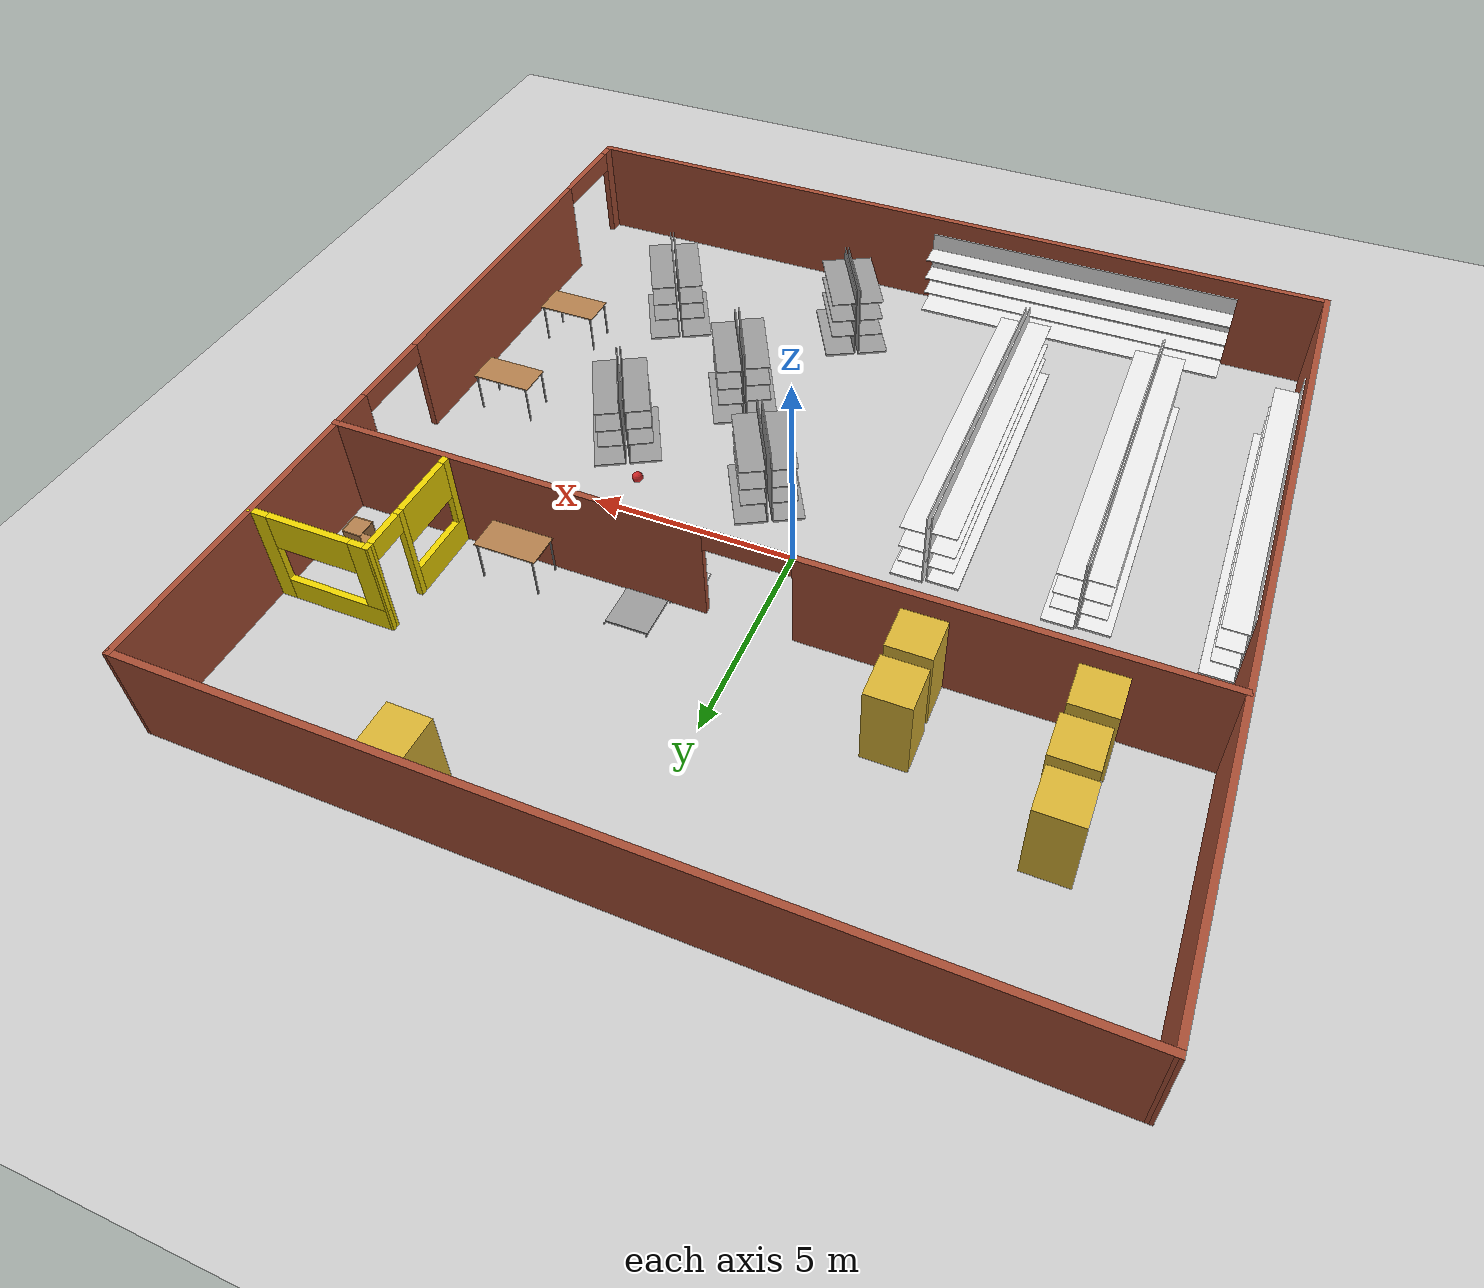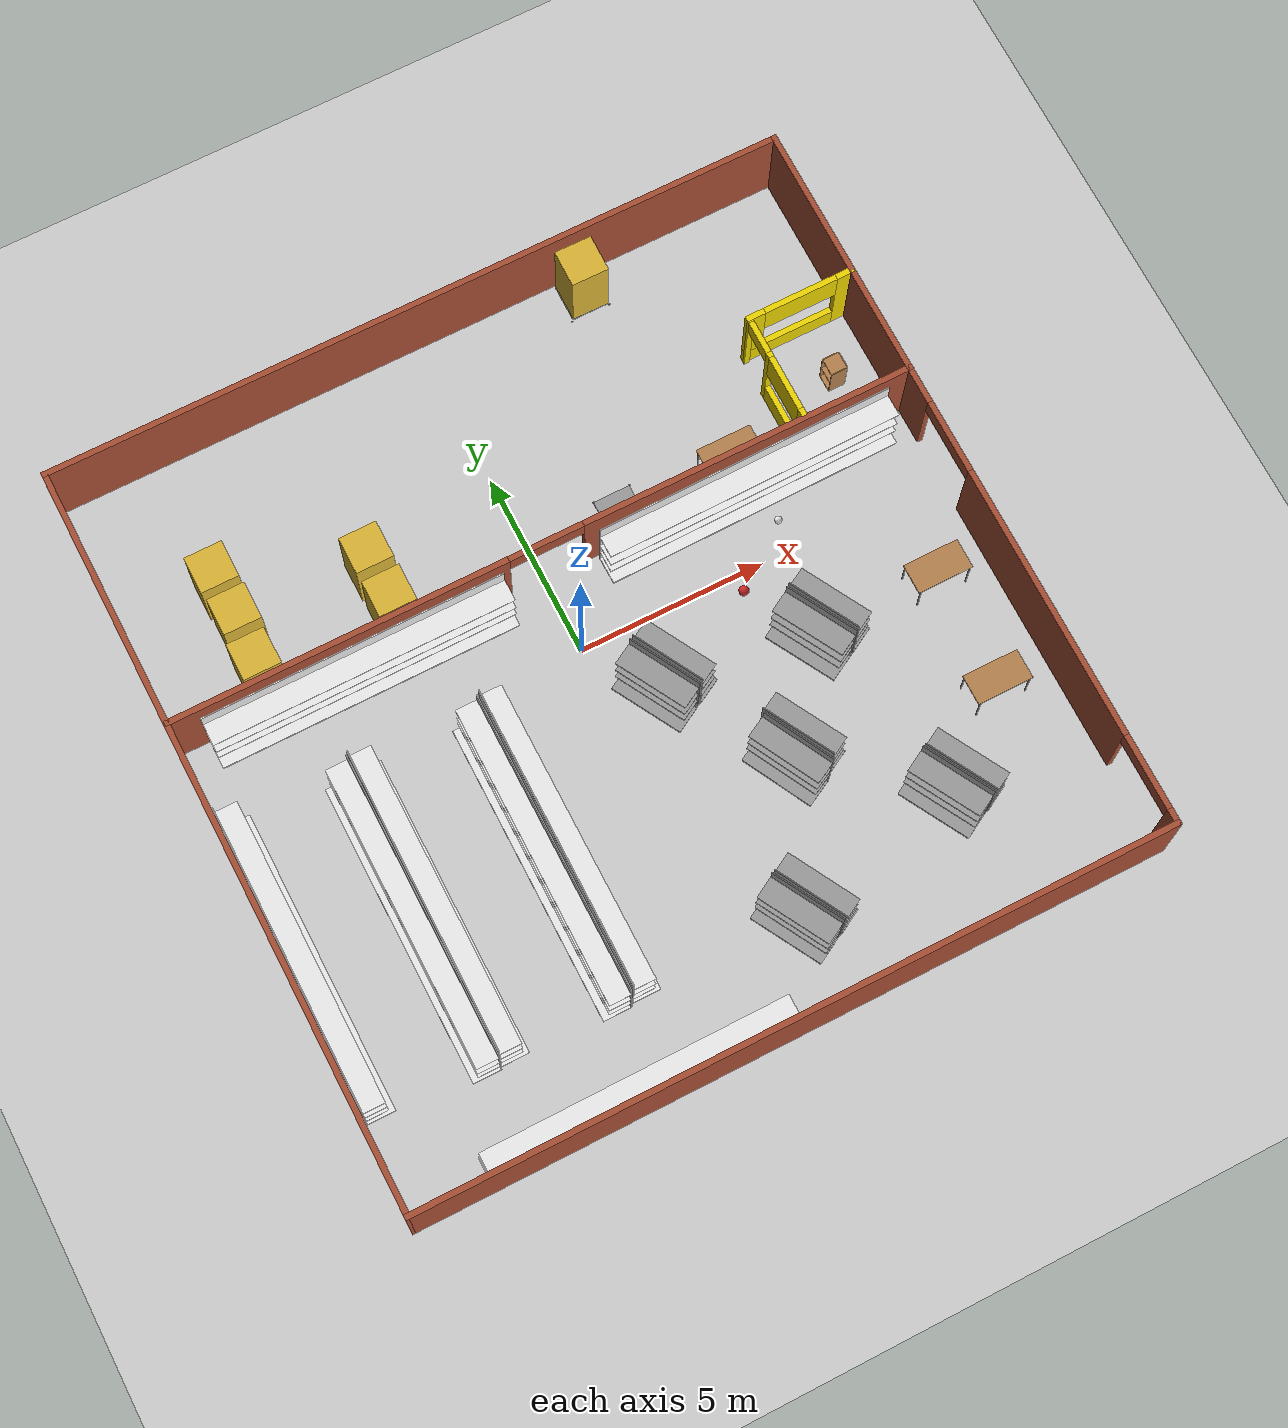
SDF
<sdf version="1.6">
 <world name="default">
  <plugin name="welcome_message" filename="libwelcome_message.so"/>
  <light name="sun" type="directional">
   <pose>0 0 10 0 -0 0</pose>
   <diffuse>0.8 0.8 0.8 1</diffuse>
   <specular>0.2 0.2 0.2 1</specular>
   <attenuation>
    <range>1000</range>
    <constant>0.9</constant>
    <linear>0.01</linear>
    <quadratic>0.001</quadratic>
   </attenuation>
   <direction>-0.5 0.1 -0.9</direction>
  </light>
  <model name="ground_plane">
   <static>1</static>
   <link name="link">
    <collision name="collision">
     <geometry><plane><normal>0 0 1</normal><size>100 100</size></plane></geometry>
     <surface>
      <contact><collide_bitmask>65535</collide_bitmask></contact>
      <friction><ode><mu>100</mu><mu2>50</mu2></ode></friction>
     </surface>
    </collision>
    <visual name="visual">
     <cast_shadows>0</cast_shadows>
     <geometry><plane><normal>0 0 1</normal><size>100 100</size></plane></geometry>
     <material>
      <script><uri>file://media/materials/scripts/gazebo.material</uri><name>Gazebo/Grey</name></script>
     </material>
    </visual>
   </link>
  </model>
  <gravity>0 0 -9.8</gravity>
  <magnetic_field>6e-06 2.3e-05 -4.2e-05</magnetic_field>
  <atmosphere type="adiabatic"/>
  <physics name="default_physics" default="0" type="ode">
   <max_step_size>0.001</max_step_size>
   <real_time_factor>1</real_time_factor>
   <real_time_update_rate>1000</real_time_update_rate>
  </physics>
  <scene><ambient>0.4 0.4 0.4 1</ambient><background>0.7 0.7 0.7 1</background><shadows>1</shadows></scene>
  <audio><device>default</device></audio>
  <spherical_coordinates>
   <surface_model>EARTH_WGS84</surface_model>
   <latitude_deg>0</latitude_deg>
   <longitude_deg>0</longitude_deg>
   <elevation>0</elevation>
   <heading_deg>0</heading_deg>
  </spherical_coordinates>
  <model name="building">
   <pose>0.102054 -0.79848 0 0 -0 0</pose>
   <link name="Wall_1">
    <collision name="Wall_1_Collision">
     <geometry><box><size>20.0396 0.15 2.5</size></box></geometry>
     <pose>0 0 1.25 0 -0 0</pose>
    </collision>
    <visual name="Wall_1_Visual">
     <pose>0 0 1.25 0 -0 0</pose>
     <geometry><box><size>20.0396 0.15 2.5</size></box></geometry>
     <material>
      <script><uri>file://media/materials/scripts/gazebo.material</uri><name>Gazebo/Bricks</name></script>
      <ambient>1 1 1 1</ambient>
     </material>
     <meta><layer>0</layer></meta>
    </visual>
    <pose>-0.003384 9.925 0 0 -0 -0.00199</pose>
   </link>
   <link name="Wall_11">
    <pose>8.49082 5.85121 0 0 -0 3.14159</pose>
    <visual name="Wall_11_Visual_0">
     <pose>-1.24971 0 1.25 0 -0 0</pose>
     <geometry><box><size>0.485738 0.15 2.5</size></box></geometry>
     <material>
      <script><uri>file://media/materials/scripts/gazebo.material</uri><name>Gazebo/Grey</name></script>
      <ambient>0.929412 0.831373 0 1</ambient>
     </material>
     <meta><layer>0</layer></meta>
    </visual>
    <collision name="Wall_11_Collision_0">
     <geometry><box><size>0.485738 0.15 2.5</size></box></geometry>
     <pose>-1.24971 0 1.25 0 -0 0</pose>
    </collision>
    <visual name="Wall_11_Visual_1">
     <pose>0.242869 0 0.3 0 -0 0</pose>
     <geometry><box><size>2.49943 0.15 0.6</size></box></geometry>
     <material>
      <script><uri>file://media/materials/scripts/gazebo.material</uri><name>Gazebo/Grey</name></script>
      <ambient>0.929412 0.831373 0 1</ambient>
     </material>
     <meta><layer>0</layer></meta>
    </visual>
    <collision name="Wall_11_Collision_1">
     <geometry><box><size>2.49943 0.15 0.6</size></box></geometry>
     <pose>0.242869 0 0.3 0 -0 0</pose>
    </collision>
    <visual name="Wall_11_Visual_2">
     <pose>1.24287 0 1.55 0 -0 0</pose>
     <geometry><box><size>0.499431 0.15 1.9</size></box></geometry>
     <material>
      <script><uri>file://media/materials/scripts/gazebo.material</uri><name>Gazebo/Grey</name></script>
      <ambient>0.929412 0.831373 0 1</ambient>
     </material>
     <meta><layer>0</layer></meta>
    </visual>
    <collision name="Wall_11_Collision_2">
     <geometry><box><size>0.499431 0.15 1.9</size></box></geometry>
     <pose>1.24287 0 1.55 0 -0 0</pose>
    </collision>
    <visual name="Wall_11_Visual_3">
     <pose>-0.006846 0 2.05 0 -0 0</pose>
     <geometry><box><size>2 0.15 0.9</size></box></geometry>
     <material>
      <script><uri>file://media/materials/scripts/gazebo.material</uri><name>Gazebo/Grey</name></script>
      <ambient>0.929412 0.831373 0 1</ambient>
     </material>
     <meta><layer>0</layer></meta>
    </visual>
    <collision name="Wall_11_Collision_3">
     <geometry><box><size>2 0.15 0.9</size></box></geometry>
     <pose>-0.006846 0 2.05 0 -0 0</pose>
    </collision>
   </link>
   <link name="Wall_12">
    <pose>7.06982 4.44571 0 0 -0 -1.57329</pose>
    <visual name="Wall_12_Visual_0">
     <pose>-1.38426 0 1.25 0 -0 0</pose>
     <geometry><box><size>0.192441 0.15 2.5</size></box></geometry>
     <material>
      <script><uri>file://media/materials/scripts/gazebo.material</uri><name>Gazebo/Grey</name></script>
      <ambient>0.929412 0.831373 0 1</ambient>
     </material>
     <meta><layer>0</layer></meta>
    </visual>
    <collision name="Wall_12_Collision_0">
     <geometry><box><size>0.192441 0.15 2.5</size></box></geometry>
     <pose>-1.38426 0 1.25 0 -0 0</pose>
    </collision>
    <visual name="Wall_12_Visual_1">
     <pose>-0.315915 0 1.25 0 -0 0</pose>
     <geometry><box><size>0.144256 0.15 2.5</size></box></geometry>
     <material>
      <script><uri>file://media/materials/scripts/gazebo.material</uri><name>Gazebo/Grey</name></script>
      <ambient>0.929412 0.831373 0 1</ambient>
     </material>
     <meta><layer>0</layer></meta>
    </visual>
    <collision name="Wall_12_Collision_1">
     <geometry><box><size>0.144256 0.15 2.5</size></box></geometry>
     <pose>-0.315915 0 1.25 0 -0 0</pose>
    </collision>
    <visual name="Wall_12_Visual_2">
     <pose>0.618349 0 0.35 0 -0 0</pose>
     <geometry><box><size>1.72427 0.15 0.7</size></box></geometry>
     <material>
      <script><uri>file://media/materials/scripts/gazebo.material</uri><name>Gazebo/Grey</name></script>
      <ambient>0.929412 0.831373 0 1</ambient>
     </material>
     <meta><layer>0</layer></meta>
    </visual>
    <collision name="Wall_12_Collision_2">
     <geometry><box><size>1.72427 0.15 0.7</size></box></geometry>
     <pose>0.618349 0 0.35 0 -0 0</pose>
    </collision>
    <visual name="Wall_12_Visual_3">
     <pose>1.37478 0 1.6 0 -0 0</pose>
     <geometry><box><size>0.211404 0.15 1.8</size></box></geometry>
     <material>
      <script><uri>file://media/materials/scripts/gazebo.material</uri><name>Gazebo/Grey</name></script>
      <ambient>0.929412 0.831373 0 1</ambient>
     </material>
     <meta><layer>0</layer></meta>
    </visual>
    <collision name="Wall_12_Collision_3">
     <geometry><box><size>0.211404 0.15 1.8</size></box></geometry>
     <pose>1.37478 0 1.6 0 -0 0</pose>
    </collision>
    <visual name="Wall_12_Visual_4">
     <pose>0.512647 0 2 0 -0 0</pose>
     <geometry><box><size>1.51287 0.15 1</size></box></geometry>
     <material>
      <script><uri>file://media/materials/scripts/gazebo.material</uri><name>Gazebo/Grey</name></script>
      <ambient>0.929412 0.831373 0 1</ambient>
     </material>
     <meta><layer>0</layer></meta>
    </visual>
    <collision name="Wall_12_Collision_4">
     <geometry><box><size>1.51287 0.15 1</size></box></geometry>
     <pose>0.512647 0 2 0 -0 0</pose>
    </collision>
    <visual name="Wall_12_Visual_5">
     <pose>-0.838044 0 2.25 0 -0 0</pose>
     <geometry><box><size>0.9 0.15 0.5</size></box></geometry>
     <material>
      <script><uri>file://media/materials/scripts/gazebo.material</uri><name>Gazebo/Grey</name></script>
      <ambient>0.929412 0.831373 0 1</ambient>
     </material>
     <meta><layer>0</layer></meta>
    </visual>
    <collision name="Wall_12_Collision_5">
     <geometry><box><size>0.9 0.15 0.5</size></box></geometry>
     <pose>-0.838044 0 2.25 0 -0 0</pose>
    </collision>
   </link>
   <link name="Wall_2">
    <pose>9.94132 -0.019793 0 0 -0 -1.5708</pose>
    <visual name="Wall_2_Visual_0">
     <pose>-5.95566 0 1.25 0 -0 0</pose>
     <geometry><box><size>8.08867 0.15 2.5</size></box></geometry>
     <material>
      <script><uri>file://media/materials/scripts/gazebo.material</uri><name>Gazebo/Bricks</name></script>
      <ambient>1 1 1 1</ambient>
     </material>
     <meta><layer>0</layer></meta>
    </visual>
    <collision name="Wall_2_Collision_0">
     <geometry><box><size>8.08867 0.15 2.5</size></box></geometry>
     <pose>-5.95566 0 1.25 0 -0 0</pose>
    </collision>
    <visual name="Wall_2_Visual_1">
     <pose>3.81514 0 1.25 0 -0 0</pose>
     <geometry><box><size>7.45293 0.15 2.5</size></box></geometry>
     <material>
      <script><uri>file://media/materials/scripts/gazebo.material</uri><name>Gazebo/Bricks</name></script>
      <ambient>1 1 1 1</ambient>
     </material>
     <meta><layer>0</layer></meta>
    </visual>
    <collision name="Wall_2_Collision_1">
     <geometry><box><size>7.45293 0.15 2.5</size></box></geometry>
     <pose>3.81514 0 1.25 0 -0 0</pose>
    </collision>
    <visual name="Wall_2_Visual_2">
     <pose>9.7708 0 1.25 0 -0 0</pose>
     <geometry><box><size>0.458396 0.15 2.5</size></box></geometry>
     <material>
      <script><uri>file://media/materials/scripts/gazebo.material</uri><name>Gazebo/Bricks</name></script>
      <ambient>1 1 1 1</ambient>
     </material>
     <meta><layer>0</layer></meta>
    </visual>
    <collision name="Wall_2_Collision_2">
     <geometry><box><size>0.458396 0.15 2.5</size></box></geometry>
     <pose>9.7708 0 1.25 0 -0 0</pose>
    </collision>
    <visual name="Wall_2_Visual_3">
     <pose>-0.91133 0 2.25 0 -0 0</pose>
     <geometry><box><size>2 0.15 0.5</size></box></geometry>
     <material>
      <script><uri>file://media/materials/scripts/gazebo.material</uri><name>Gazebo/Bricks</name></script>
      <ambient>1 1 1 1</ambient>
     </material>
     <meta><layer>0</layer></meta>
    </visual>
    <collision name="Wall_2_Collision_3">
     <geometry><box><size>2 0.15 0.5</size></box></geometry>
     <pose>-0.91133 0 2.25 0 -0 0</pose>
    </collision>
    <visual name="Wall_2_Visual_4">
     <pose>8.5416 0 2.25 0 -0 0</pose>
     <geometry><box><size>2 0.15 0.5</size></box></geometry>
     <material>
      <script><uri>file://media/materials/scripts/gazebo.material</uri><name>Gazebo/Bricks</name></script>
      <ambient>1 1 1 1</ambient>
     </material>
     <meta><layer>0</layer></meta>
    </visual>
    <collision name="Wall_2_Collision_4">
     <geometry><box><size>2 0.15 0.5</size></box></geometry>
     <pose>8.5416 0 2.25 0 -0 0</pose>
    </collision>
   </link>
   <link name="Wall_4">
    <collision name="Wall_4_Collision">
     <geometry><box><size>20 0.15 2.5</size></box></geometry>
     <pose>0 0 1.25 0 -0 0</pose>
    </collision>
    <visual name="Wall_4_Visual">
     <pose>0 0 1.25 0 -0 0</pose>
     <geometry><box><size>20 0.15 2.5</size></box></geometry>
     <material>
      <script><uri>file://media/materials/scripts/gazebo.material</uri><name>Gazebo/Bricks</name></script>
      <ambient>1 1 1 1</ambient>
     </material>
     <meta><layer>0</layer></meta>
    </visual>
    <pose>0.016317 -9.94479 0 0 -0 3.14159</pose>
   </link>
   <link name="Wall_5">
    <collision name="Wall_5_Collision">
     <geometry><box><size>20.0396 0.15 2.5</size></box></geometry>
     <pose>0 0 1.25 0 -0 0</pose>
    </collision>
    <visual name="Wall_5_Visual">
     <pose>0 0 1.25 0 -0 0</pose>
     <geometry><box><size>20.0396 0.15 2.5</size></box></geometry>
     <material>
      <script><uri>file://media/materials/scripts/gazebo.material</uri><name>Gazebo/Bricks</name></script>
      <ambient>1 1 1 1</ambient>
     </material>
     <meta><layer>0</layer></meta>
    </visual>
    <pose>-9.92838 0 0 0 -0 1.57278</pose>
   </link>
   <link name="Wall_9">
    <pose>0.023317 2.91821 0 0 -0 0</pose>
    <visual name="Wall_9_Visual_0">
     <pose>-5.50075 0 1.25 0 -0 0</pose>
     <geometry><box><size>8.9985 0.15 2.5</size></box></geometry>
     <material>
      <script><uri>file://media/materials/scripts/gazebo.material</uri><name>Gazebo/Bricks</name></script>
      <ambient>1 1 1 1</ambient>
     </material>
     <meta><layer>0</layer></meta>
    </visual>
    <collision name="Wall_9_Collision_0">
     <geometry><box><size>8.9985 0.15 2.5</size></box></geometry>
     <pose>-5.50075 0 1.25 0 -0 0</pose>
    </collision>
    <visual name="Wall_9_Visual_1">
     <pose>5.49925 0 1.25 0 -0 0</pose>
     <geometry><box><size>9.0015 0.15 2.5</size></box></geometry>
     <material>
      <script><uri>file://media/materials/scripts/gazebo.material</uri><name>Gazebo/Bricks</name></script>
      <ambient>1 1 1 1</ambient>
     </material>
     <meta><layer>0</layer></meta>
    </visual>
    <collision name="Wall_9_Collision_1">
     <geometry><box><size>9.0015 0.15 2.5</size></box></geometry>
     <pose>5.49925 0 1.25 0 -0 0</pose>
    </collision>
    <visual name="Wall_9_Visual_2">
     <pose>-0.001497 0 2.25 0 -0 0</pose>
     <geometry><box><size>2 0.15 0.5</size></box></geometry>
     <material>
      <script><uri>file://media/materials/scripts/gazebo.material</uri><name>Gazebo/Bricks</name></script>
      <ambient>1 1 1 1</ambient>
     </material>
     <meta><layer>0</layer></meta>
    </visual>
    <collision name="Wall_9_Collision_2">
     <geometry><box><size>2 0.15 0.5</size></box></geometry>
     <pose>-0.001497 0 2.25 0 -0 0</pose>
    </collision>
   </link>
   <static>1</static>
  </model>
  <model name="dolly">
   <link name="link_0">
    <inertial>
     <mass>0.580233</mass>
     <inertia>
      <ixx>0.0485156</ixx>
      <ixy>0</ixy>
      <ixz>0</ixz>
      <iyy>0.0485156</iyy>
      <iyz>0</iyz>
      <izz>0.0967055</izz>
     </inertia>
    </inertial>
    <pose>-0 0 0.05 0 -0 0</pose>
    <visual name="visual">
     <geometry><box><size>1 1 0.05</size></box></geometry>
     <material>
      <lighting>1</lighting>
      <script><uri>file://media/materials/scripts/gazebo.material</uri><name>Gazebo/Grey</name></script>
      <shader type="vertex"><normal_map>__default__</normal_map></shader>
      <ambient>0.3 0.3 0.3 1</ambient>
      <diffuse>0.9 0.9 0.9 1</diffuse>
      <specular>0.08 0.08 0.08 1</specular>
      <emissive>0 0 0 1</emissive>
     </material>
    </visual>
    <collision name="collision">
     <geometry><box><size>1 1 0.05</size></box></geometry>
     <surface>
      <friction>
       <ode><mu>1</mu><mu2>1</mu2><fdir1>0 0 0</fdir1><slip1>0</slip1><slip2>0</slip2></ode>
       <torsional>
        <coefficient>1</coefficient>
        <patch_radius>0</patch_radius>
        <surface_radius>0</surface_radius>
        <use_patch_radius>1</use_patch_radius>
        <ode><slip>0</slip></ode>
       </torsional>
      </friction>
      <bounce><restitution_coefficient>0</restitution_coefficient><threshold>1e+06</threshold></bounce>
      <contact>
       <collide_without_contact>0</collide_without_contact>
       <collide_without_contact_bitmask>1</collide_without_contact_bitmask>
       <collide_bitmask>1</collide_bitmask>
       <ode>
        <soft_cfm>0</soft_cfm>
        <soft_erp>0.2</soft_erp>
        <kp>1e+13</kp>
        <kd>1</kd>
        <max_vel>0.01</max_vel>
        <min_depth>0</min_depth>
       </ode>
       <bullet>
        <split_impulse>1</split_impulse>
        <split_impulse_penetration_threshold>-0.01</split_impulse_penetration_threshold>
        <soft_cfm>0</soft_cfm>
        <soft_erp>0.2</soft_erp>
        <kp>1e+13</kp>
        <kd>1</kd>
       </bullet>
      </contact>
     </surface>
    </collision>
   </link>
   <link name="link_0_0">
    <inertial>
     <mass>1</mass>
     <inertia><ixx>0.1</ixx><ixy>0</ixy><ixz>0</ixz><iyy>0.1</iyy><iyz>0</iyz><izz>0.1</izz></inertia>
    </inertial>
    <pose>-0.475902 0.525156 0 0 -0 0</pose>
    <visual name="visual">
     <geometry><sphere><radius>0.025</radius></sphere></geometry>
     <material>
      <lighting>1</lighting>
      <script><uri>file://media/materials/scripts/gazebo.material</uri><name>Gazebo/Grey</name></script>
      <shader type="vertex"><normal_map>__default__</normal_map></shader>
      <ambient>0.3 0.3 0.3 1</ambient>
      <diffuse>0.7 0.7 0.7 1</diffuse>
      <specular>0.01 0.01 0.01 1</specular>
      <emissive>0 0 0 1</emissive>
     </material>
    </visual>
    <collision name="collision">
     <geometry><sphere><radius>0.025</radius></sphere></geometry>
     <surface>
      <friction>
       <ode><mu>1</mu><mu2>1</mu2><fdir1>0 0 0</fdir1><slip1>0</slip1><slip2>0</slip2></ode>
       <torsional>
        <coefficient>1</coefficient>
        <patch_radius>0</patch_radius>
        <surface_radius>0</surface_radius>
        <use_patch_radius>1</use_patch_radius>
        <ode><slip>0</slip></ode>
       </torsional>
      </friction>
      <bounce><restitution_coefficient>0</restitution_coefficient><threshold>1e+06</threshold></bounce>
      <contact>
       <collide_without_contact>0</collide_without_contact>
       <collide_without_contact_bitmask>1</collide_without_contact_bitmask>
       <collide_bitmask>1</collide_bitmask>
       <ode>
        <soft_cfm>0</soft_cfm>
        <soft_erp>0.2</soft_erp>
        <kp>1e+13</kp>
        <kd>1</kd>
        <max_vel>0.01</max_vel>
        <min_depth>0</min_depth>
       </ode>
       <bullet>
        <split_impulse>1</split_impulse>
        <split_impulse_penetration_threshold>-0.01</split_impulse_penetration_threshold>
        <soft_cfm>0</soft_cfm>
        <soft_erp>0.2</soft_erp>
        <kp>1e+13</kp>
        <kd>1</kd>
       </bullet>
      </contact>
     </surface>
    </collision>
   </link>
   <link name="link_0_0_clone">
    <inertial>
     <mass>1</mass>
     <inertia><ixx>0.1</ixx><ixy>0</ixy><ixz>0</ixz><iyy>0.1</iyy><iyz>0</iyz><izz>0.1</izz></inertia>
    </inertial>
    <pose>0.524976 0.525931 -1.1e-05 3.7e-05 1.2e-05 0.000901</pose>
    <visual name="visual_0">
     <geometry><sphere><radius>0.025</radius></sphere></geometry>
     <material>
      <lighting>1</lighting>
      <script><uri>file://media/materials/scripts/gazebo.material</uri><name>Gazebo/Grey</name></script>
      <shader type="vertex"><normal_map>__default__</normal_map></shader>
      <ambient>0.3 0.3 0.3 1</ambient>
      <diffuse>0.7 0.7 0.7 1</diffuse>
      <specular>0.01 0.01 0.01 1</specular>
      <emissive>0 0 0 1</emissive>
     </material>
    </visual>
    <collision name="collision">
     <geometry><sphere><radius>0.025</radius></sphere></geometry>
     <surface>
      <friction>
       <ode><mu>1</mu><mu2>1</mu2><fdir1>0 0 0</fdir1><slip1>0</slip1><slip2>0</slip2></ode>
       <torsional>
        <coefficient>1</coefficient>
        <patch_radius>0</patch_radius>
        <surface_radius>0</surface_radius>
        <use_patch_radius>1</use_patch_radius>
        <ode><slip>0</slip></ode>
       </torsional>
      </friction>
      <bounce><restitution_coefficient>0</restitution_coefficient><threshold>1e+06</threshold></bounce>
      <contact>
       <collide_without_contact>0</collide_without_contact>
       <collide_without_contact_bitmask>1</collide_without_contact_bitmask>
       <collide_bitmask>1</collide_bitmask>
       <ode>
        <soft_cfm>0</soft_cfm>
        <soft_erp>0.2</soft_erp>
        <kp>1e+13</kp>
        <kd>1</kd>
        <max_vel>0.01</max_vel>
        <min_depth>0</min_depth>
       </ode>
       <bullet>
        <split_impulse>1</split_impulse>
        <split_impulse_penetration_threshold>-0.01</split_impulse_penetration_threshold>
        <soft_cfm>0</soft_cfm>
        <soft_erp>0.2</soft_erp>
        <kp>1e+13</kp>
        <kd>1</kd>
       </bullet>
      </contact>
     </surface>
    </collision>
   </link>
   <link name="link_0_0_clone_clone">
    <inertial>
     <mass>1</mass>
     <inertia><ixx>0.1</ixx><ixy>0</ixy><ixz>0</ixz><iyy>0.1</iyy><iyz>0</iyz><izz>0.1</izz></inertia>
    </inertial>
    <pose>0.525946 -0.524999 -5.1e-05 7.4e-05 2.4e-05 0.001802</pose>
    <visual name="visual_0">
     <geometry><sphere><radius>0.025</radius></sphere></geometry>
     <material>
      <lighting>1</lighting>
      <script><uri>file://media/materials/scripts/gazebo.material</uri><name>Gazebo/Grey</name></script>
      <shader type="vertex"><normal_map>__default__</normal_map></shader>
      <ambient>0.3 0.3 0.3 1</ambient>
      <diffuse>0.7 0.7 0.7 1</diffuse>
      <specular>0.01 0.01 0.01 1</specular>
      <emissive>0 0 0 1</emissive>
     </material>
    </visual>
    <collision name="collision">
     <geometry><sphere><radius>0.025</radius></sphere></geometry>
     <surface>
      <friction>
       <ode><mu>1</mu><mu2>1</mu2><fdir1>0 0 0</fdir1><slip1>0</slip1><slip2>0</slip2></ode>
       <torsional>
        <coefficient>1</coefficient>
        <patch_radius>0</patch_radius>
        <surface_radius>0</surface_radius>
        <use_patch_radius>1</use_patch_radius>
        <ode><slip>0</slip></ode>
       </torsional>
      </friction>
      <bounce><restitution_coefficient>0</restitution_coefficient><threshold>1e+06</threshold></bounce>
      <contact>
       <collide_without_contact>0</collide_without_contact>
       <collide_without_contact_bitmask>1</collide_without_contact_bitmask>
       <collide_bitmask>1</collide_bitmask>
       <ode>
        <soft_cfm>0</soft_cfm>
        <soft_erp>0.2</soft_erp>
        <kp>1e+13</kp>
        <kd>1</kd>
        <max_vel>0.01</max_vel>
        <min_depth>0</min_depth>
       </ode>
       <bullet>
        <split_impulse>1</split_impulse>
        <split_impulse_penetration_threshold>-0.01</split_impulse_penetration_threshold>
        <soft_cfm>0</soft_cfm>
        <soft_erp>0.2</soft_erp>
        <kp>1e+13</kp>
        <kd>1</kd>
       </bullet>
      </contact>
     </surface>
    </collision>
   </link>
   <link name="link_0_0_clone_clone_clone">
    <inertial>
     <mass>1</mass>
     <inertia><ixx>0.1</ixx><ixy>0</ixy><ixz>0</ixz><iyy>0.1</iyy><iyz>0</iyz><izz>0.1</izz></inertia>
    </inertial>
    <pose>-0.525024 -0.52597 -4e-05 0.000111 3.5e-05 0.002703</pose>
    <visual name="visual_0">
     <geometry><sphere><radius>0.025</radius></sphere></geometry>
     <material>
      <lighting>1</lighting>
      <script><uri>file://media/materials/scripts/gazebo.material</uri><name>Gazebo/Grey</name></script>
      <shader type="vertex"><normal_map>__default__</normal_map></shader>
      <ambient>0.3 0.3 0.3 1</ambient>
      <diffuse>0.7 0.7 0.7 1</diffuse>
      <specular>0.01 0.01 0.01 1</specular>
      <emissive>0 0 0 1</emissive>
     </material>
    </visual>
    <collision name="collision">
     <geometry><sphere><radius>0.025</radius></sphere></geometry>
     <surface>
      <friction>
       <ode><mu>1</mu><mu2>1</mu2><fdir1>0 0 0</fdir1><slip1>0</slip1><slip2>0</slip2></ode>
       <torsional>
        <coefficient>1</coefficient>
        <patch_radius>0</patch_radius>
        <surface_radius>0</surface_radius>
        <use_patch_radius>1</use_patch_radius>
        <ode><slip>0</slip></ode>
       </torsional>
      </friction>
      <bounce><restitution_coefficient>0</restitution_coefficient><threshold>1e+06</threshold></bounce>
      <contact>
       <collide_without_contact>0</collide_without_contact>
       <collide_without_contact_bitmask>1</collide_without_contact_bitmask>
       <collide_bitmask>1</collide_bitmask>
       <ode>
        <soft_cfm>0</soft_cfm>
        <soft_erp>0.2</soft_erp>
        <kp>1e+13</kp>
        <kd>1</kd>
        <max_vel>0.01</max_vel>
        <min_depth>0</min_depth>
       </ode>
       <bullet>
        <split_impulse>1</split_impulse>
        <split_impulse_penetration_threshold>-0.01</split_impulse_penetration_threshold>
        <soft_cfm>0</soft_cfm>
        <soft_erp>0.2</soft_erp>
        <kp>1e+13</kp>
        <kd>1</kd>
       </bullet>
      </contact>
     </surface>
    </collision>
   </link>
   <joint name="link_0_JOINT_1" type="ball">
    <parent>link_0</parent>
    <child>link_0_0</child>
    <physics>
     <ode><limit><cfm>0</cfm><erp>0.2</erp></limit><suspension><cfm>0</cfm><erp>0.2</erp></suspension></ode>
    </physics>
   </joint>
   <joint name="link_0_JOINT_2" type="revolute">
    <parent>link_0</parent>
    <child>link_0_0_clone</child>
    <axis>
     <xyz>1 0 0</xyz>
     <use_parent_model_frame>0</use_parent_model_frame>
     <limit>
      <lower>-1.79769e+308</lower>
      <upper>1.79769e+308</upper>
      <effort>-1</effort>
      <velocity>-1</velocity>
     </limit>
     <dynamics>
      <spring_reference>0</spring_reference>
      <spring_stiffness>0</spring_stiffness>
      <damping>0</damping>
     </dynamics>
    </axis>
    <physics>
     <ode><limit><cfm>0</cfm><erp>0.2</erp></limit><suspension><cfm>0</cfm><erp>0.2</erp></suspension></ode>
    </physics>
   </joint>
   <joint name="link_0_JOINT_3" type="revolute">
    <parent>link_0</parent>
    <child>link_0_0_clone_clone</child>
    <axis>
     <xyz>1 0 0</xyz>
     <use_parent_model_frame>0</use_parent_model_frame>
     <limit>
      <lower>-1.79769e+308</lower>
      <upper>1.79769e+308</upper>
      <effort>-1</effort>
      <velocity>-1</velocity>
     </limit>
     <dynamics>
      <spring_reference>0</spring_reference>
      <spring_stiffness>0</spring_stiffness>
      <damping>0</damping>
     </dynamics>
    </axis>
    <physics>
     <ode><limit><cfm>0</cfm><erp>0.2</erp></limit><suspension><cfm>0</cfm><erp>0.2</erp></suspension></ode>
    </physics>
   </joint>
   <joint name="link_0_JOINT_4" type="revolute">
    <parent>link_0</parent>
    <child>link_0_0_clone_clone_clone</child>
    <axis>
     <xyz>1 0 0</xyz>
     <use_parent_model_frame>0</use_parent_model_frame>
     <limit>
      <lower>-1.79769e+308</lower>
      <upper>1.79769e+308</upper>
      <effort>-1</effort>
      <velocity>-1</velocity>
     </limit>
     <dynamics>
      <spring_reference>0</spring_reference>
      <spring_stiffness>0</spring_stiffness>
      <damping>0</damping>
     </dynamics>
    </axis>
    <physics>
     <ode><limit><cfm>0</cfm><erp>0.2</erp></limit><suspension><cfm>0</cfm><erp>0.2</erp></suspension></ode>
    </physics>
   </joint>
   <static>0</static>
   <pose>2.48886 2.79179 0.075025 -3.8e-05 -1.1e-05 0.005109</pose>
  </model>
  <model name="dolly_0">
   <link name="link_0">
    <inertial>
     <mass>0.580233</mass>
     <inertia>
      <ixx>0.0485156</ixx>
      <ixy>0</ixy>
      <ixz>0</ixz>
      <iyy>0.0485156</iyy>
      <iyz>0</iyz>
      <izz>0.0967055</izz>
     </inertia>
    </inertial>
    <pose>-0 0 0.05 0 -0 0</pose>
    <visual name="visual">
     <geometry><box><size>1 1 0.05</size></box></geometry>
     <material>
      <lighting>1</lighting>
      <script><uri>file://media/materials/scripts/gazebo.material</uri><name>Gazebo/Grey</name></script>
      <shader type="vertex"><normal_map>__default__</normal_map></shader>
      <ambient>0.3 0.3 0.3 1</ambient>
      <diffuse>0.9 0.9 0.9 1</diffuse>
      <specular>0.08 0.08 0.08 1</specular>
      <emissive>0 0 0 1</emissive>
     </material>
    </visual>
    <collision name="collision">
     <geometry><box><size>1 1 0.05</size></box></geometry>
     <surface>
      <friction>
       <ode><mu>1</mu><mu2>1</mu2><fdir1>0 0 0</fdir1><slip1>0</slip1><slip2>0</slip2></ode>
       <torsional>
        <coefficient>1</coefficient>
        <patch_radius>0</patch_radius>
        <surface_radius>0</surface_radius>
        <use_patch_radius>1</use_patch_radius>
        <ode><slip>0</slip></ode>
       </torsional>
      </friction>
      <bounce><restitution_coefficient>0</restitution_coefficient><threshold>1e+06</threshold></bounce>
      <contact>
       <collide_without_contact>0</collide_without_contact>
       <collide_without_contact_bitmask>1</collide_without_contact_bitmask>
       <collide_bitmask>1</collide_bitmask>
       <ode>
        <soft_cfm>0</soft_cfm>
        <soft_erp>0.2</soft_erp>
        <kp>1e+13</kp>
        <kd>1</kd>
        <max_vel>0.01</max_vel>
        <min_depth>0</min_depth>
       </ode>
       <bullet>
        <split_impulse>1</split_impulse>
        <split_impulse_penetration_threshold>-0.01</split_impulse_penetration_threshold>
        <soft_cfm>0</soft_cfm>
        <soft_erp>0.2</soft_erp>
        <kp>1e+13</kp>
        <kd>1</kd>
       </bullet>
      </contact>
     </surface>
    </collision>
   </link>
   <link name="link_0_0">
    <inertial>
     <mass>1</mass>
     <inertia><ixx>0.1</ixx><ixy>0</ixy><ixz>0</ixz><iyy>0.1</iyy><iyz>0</iyz><izz>0.1</izz></inertia>
    </inertial>
    <pose>-0.475902 0.525156 0 0 -0 0</pose>
    <visual name="visual">
     <geometry><sphere><radius>0.025</radius></sphere></geometry>
     <material>
      <lighting>1</lighting>
      <script><uri>file://media/materials/scripts/gazebo.material</uri><name>Gazebo/Grey</name></script>
      <shader type="vertex"><normal_map>__default__</normal_map></shader>
      <ambient>0.3 0.3 0.3 1</ambient>
      <diffuse>0.7 0.7 0.7 1</diffuse>
      <specular>0.01 0.01 0.01 1</specular>
      <emissive>0 0 0 1</emissive>
     </material>
    </visual>
    <collision name="collision">
     <geometry><sphere><radius>0.025</radius></sphere></geometry>
     <surface>
      <friction>
       <ode><mu>1</mu><mu2>1</mu2><fdir1>0 0 0</fdir1><slip1>0</slip1><slip2>0</slip2></ode>
       <torsional>
        <coefficient>1</coefficient>
        <patch_radius>0</patch_radius>
        <surface_radius>0</surface_radius>
        <use_patch_radius>1</use_patch_radius>
        <ode><slip>0</slip></ode>
       </torsional>
      </friction>
      <bounce><restitution_coefficient>0</restitution_coefficient><threshold>1e+06</threshold></bounce>
      <contact>
       <collide_without_contact>0</collide_without_contact>
       <collide_without_contact_bitmask>1</collide_without_contact_bitmask>
       <collide_bitmask>1</collide_bitmask>
       <ode>
        <soft_cfm>0</soft_cfm>
        <soft_erp>0.2</soft_erp>
        <kp>1e+13</kp>
        <kd>1</kd>
        <max_vel>0.01</max_vel>
        <min_depth>0</min_depth>
       </ode>
       <bullet>
        <split_impulse>1</split_impulse>
        <split_impulse_penetration_threshold>-0.01</split_impulse_penetration_threshold>
        <soft_cfm>0</soft_cfm>
        <soft_erp>0.2</soft_erp>
        <kp>1e+13</kp>
        <kd>1</kd>
       </bullet>
      </contact>
     </surface>
    </collision>
   </link>
   <link name="link_0_0_clone">
    <inertial>
     <mass>1</mass>
     <inertia><ixx>0.1</ixx><ixy>0</ixy><ixz>0</ixz><iyy>0.1</iyy><iyz>0</iyz><izz>0.1</izz></inertia>
    </inertial>
    <pose>0.524976 0.525931 -1.1e-05 3.7e-05 1.2e-05 0.000901</pose>
    <visual name="visual_0">
     <geometry><sphere><radius>0.025</radius></sphere></geometry>
     <material>
      <lighting>1</lighting>
      <script><uri>file://media/materials/scripts/gazebo.material</uri><name>Gazebo/Grey</name></script>
      <shader type="vertex"><normal_map>__default__</normal_map></shader>
      <ambient>0.3 0.3 0.3 1</ambient>
      <diffuse>0.7 0.7 0.7 1</diffuse>
      <specular>0.01 0.01 0.01 1</specular>
      <emissive>0 0 0 1</emissive>
     </material>
    </visual>
    <collision name="collision">
     <geometry><sphere><radius>0.025</radius></sphere></geometry>
     <surface>
      <friction>
       <ode><mu>1</mu><mu2>1</mu2><fdir1>0 0 0</fdir1><slip1>0</slip1><slip2>0</slip2></ode>
       <torsional>
        <coefficient>1</coefficient>
        <patch_radius>0</patch_radius>
        <surface_radius>0</surface_radius>
        <use_patch_radius>1</use_patch_radius>
        <ode><slip>0</slip></ode>
       </torsional>
      </friction>
      <bounce><restitution_coefficient>0</restitution_coefficient><threshold>1e+06</threshold></bounce>
      <contact>
       <collide_without_contact>0</collide_without_contact>
       <collide_without_contact_bitmask>1</collide_without_contact_bitmask>
       <collide_bitmask>1</collide_bitmask>
       <ode>
        <soft_cfm>0</soft_cfm>
        <soft_erp>0.2</soft_erp>
        <kp>1e+13</kp>
        <kd>1</kd>
        <max_vel>0.01</max_vel>
        <min_depth>0</min_depth>
       </ode>
       <bullet>
        <split_impulse>1</split_impulse>
        <split_impulse_penetration_threshold>-0.01</split_impulse_penetration_threshold>
        <soft_cfm>0</soft_cfm>
        <soft_erp>0.2</soft_erp>
        <kp>1e+13</kp>
        <kd>1</kd>
       </bullet>
      </contact>
     </surface>
    </collision>
   </link>
   <link name="link_0_0_clone_clone">
    <inertial>
     <mass>1</mass>
     <inertia><ixx>0.1</ixx><ixy>0</ixy><ixz>0</ixz><iyy>0.1</iyy><iyz>0</iyz><izz>0.1</izz></inertia>
    </inertial>
    <pose>0.525946 -0.524999 -5.1e-05 7.4e-05 2.4e-05 0.001802</pose>
    <visual name="visual_0">
     <geometry><sphere><radius>0.025</radius></sphere></geometry>
     <material>
      <lighting>1</lighting>
      <script><uri>file://media/materials/scripts/gazebo.material</uri><name>Gazebo/Grey</name></script>
      <shader type="vertex"><normal_map>__default__</normal_map></shader>
      <ambient>0.3 0.3 0.3 1</ambient>
      <diffuse>0.7 0.7 0.7 1</diffuse>
      <specular>0.01 0.01 0.01 1</specular>
      <emissive>0 0 0 1</emissive>
     </material>
    </visual>
    <collision name="collision">
     <geometry><sphere><radius>0.025</radius></sphere></geometry>
     <surface>
      <friction>
       <ode><mu>1</mu><mu2>1</mu2><fdir1>0 0 0</fdir1><slip1>0</slip1><slip2>0</slip2></ode>
       <torsional>
        <coefficient>1</coefficient>
        <patch_radius>0</patch_radius>
        <surface_radius>0</surface_radius>
        <use_patch_radius>1</use_patch_radius>
        <ode><slip>0</slip></ode>
       </torsional>
      </friction>
      <bounce><restitution_coefficient>0</restitution_coefficient><threshold>1e+06</threshold></bounce>
      <contact>
       <collide_without_contact>0</collide_without_contact>
       <collide_without_contact_bitmask>1</collide_without_contact_bitmask>
       <collide_bitmask>1</collide_bitmask>
       <ode>
        <soft_cfm>0</soft_cfm>
        <soft_erp>0.2</soft_erp>
        <kp>1e+13</kp>
        <kd>1</kd>
        <max_vel>0.01</max_vel>
        <min_depth>0</min_depth>
       </ode>
       <bullet>
        <split_impulse>1</split_impulse>
        <split_impulse_penetration_threshold>-0.01</split_impulse_penetration_threshold>
        <soft_cfm>0</soft_cfm>
        <soft_erp>0.2</soft_erp>
        <kp>1e+13</kp>
        <kd>1</kd>
       </bullet>
      </contact>
     </surface>
    </collision>
   </link>
   <link name="link_0_0_clone_clone_clone">
    <inertial>
     <mass>1</mass>
     <inertia><ixx>0.1</ixx><ixy>0</ixy><ixz>0</ixz><iyy>0.1</iyy><iyz>0</iyz><izz>0.1</izz></inertia>
    </inertial>
    <pose>-0.525024 -0.52597 -4e-05 0.000111 3.5e-05 0.002703</pose>
    <visual name="visual_0">
     <geometry><sphere><radius>0.025</radius></sphere></geometry>
     <material>
      <lighting>1</lighting>
      <script><uri>file://media/materials/scripts/gazebo.material</uri><name>Gazebo/Grey</name></script>
      <shader type="vertex"><normal_map>__default__</normal_map></shader>
      <ambient>0.3 0.3 0.3 1</ambient>
      <diffuse>0.7 0.7 0.7 1</diffuse>
      <specular>0.01 0.01 0.01 1</specular>
      <emissive>0 0 0 1</emissive>
     </material>
    </visual>
    <collision name="collision">
     <geometry><sphere><radius>0.025</radius></sphere></geometry>
     <surface>
      <friction>
       <ode><mu>1</mu><mu2>1</mu2><fdir1>0 0 0</fdir1><slip1>0</slip1><slip2>0</slip2></ode>
       <torsional>
        <coefficient>1</coefficient>
        <patch_radius>0</patch_radius>
        <surface_radius>0</surface_radius>
        <use_patch_radius>1</use_patch_radius>
        <ode><slip>0</slip></ode>
       </torsional>
      </friction>
      <bounce><restitution_coefficient>0</restitution_coefficient><threshold>1e+06</threshold></bounce>
      <contact>
       <collide_without_contact>0</collide_without_contact>
       <collide_without_contact_bitmask>1</collide_without_contact_bitmask>
       <collide_bitmask>1</collide_bitmask>
       <ode>
        <soft_cfm>0</soft_cfm>
        <soft_erp>0.2</soft_erp>
        <kp>1e+13</kp>
        <kd>1</kd>
        <max_vel>0.01</max_vel>
        <min_depth>0</min_depth>
       </ode>
       <bullet>
        <split_impulse>1</split_impulse>
        <split_impulse_penetration_threshold>-0.01</split_impulse_penetration_threshold>
        <soft_cfm>0</soft_cfm>
        <soft_erp>0.2</soft_erp>
        <kp>1e+13</kp>
        <kd>1</kd>
       </bullet>
      </contact>
     </surface>
    </collision>
   </link>
   <joint name="link_0_JOINT_1" type="ball">
    <parent>link_0</parent>
    <child>link_0_0</child>
    <physics>
     <ode><limit><cfm>0</cfm><erp>0.2</erp></limit><suspension><cfm>0</cfm><erp>0.2</erp></suspension></ode>
    </physics>
   </joint>
   <joint name="link_0_JOINT_2" type="revolute">
    <parent>link_0</parent>
    <child>link_0_0_clone</child>
    <axis>
     <xyz>1 0 0</xyz>
     <use_parent_model_frame>0</use_parent_model_frame>
     <limit>
      <lower>-1.79769e+308</lower>
      <upper>1.79769e+308</upper>
      <effort>-1</effort>
      <velocity>-1</velocity>
     </limit>
     <dynamics>
      <spring_reference>0</spring_reference>
      <spring_stiffness>0</spring_stiffness>
      <damping>0</damping>
     </dynamics>
    </axis>
    <physics>
     <ode><limit><cfm>0</cfm><erp>0.2</erp></limit><suspension><cfm>0</cfm><erp>0.2</erp></suspension></ode>
    </physics>
   </joint>
   <joint name="link_0_JOINT_3" type="revolute">
    <parent>link_0</parent>
    <child>link_0_0_clone_clone</child>
    <axis>
     <xyz>1 0 0</xyz>
     <use_parent_model_frame>0</use_parent_model_frame>
     <limit>
      <lower>-1.79769e+308</lower>
      <upper>1.79769e+308</upper>
      <effort>-1</effort>
      <velocity>-1</velocity>
     </limit>
     <dynamics>
      <spring_reference>0</spring_reference>
      <spring_stiffness>0</spring_stiffness>
      <damping>0</damping>
     </dynamics>
    </axis>
    <physics>
     <ode><limit><cfm>0</cfm><erp>0.2</erp></limit><suspension><cfm>0</cfm><erp>0.2</erp></suspension></ode>
    </physics>
   </joint>
   <joint name="link_0_JOINT_4" type="revolute">
    <parent>link_0</parent>
    <child>link_0_0_clone_clone_clone</child>
    <axis>
     <xyz>1 0 0</xyz>
     <use_parent_model_frame>0</use_parent_model_frame>
     <limit>
      <lower>-1.79769e+308</lower>
      <upper>1.79769e+308</upper>
      <effort>-1</effort>
      <velocity>-1</velocity>
     </limit>
     <dynamics>
      <spring_reference>0</spring_reference>
      <spring_stiffness>0</spring_stiffness>
      <damping>0</damping>
     </dynamics>
    </axis>
    <physics>
     <ode><limit><cfm>0</cfm><erp>0.2</erp></limit><suspension><cfm>0</cfm><erp>0.2</erp></suspension></ode>
    </physics>
   </joint>
   <static>0</static>
   <pose>4.28746 8.44825 0.075018 -4.6e-05 -5e-06 -0.001109</pose>
  </model>
  <model name="cabinet">
   <static>1</static>
   <link name="cabinet_bottom_plate">
    <inertial>
     <pose>0 0 -1 0 -0 0</pose>
     <inertia><ixx>2.05</ixx><ixy>0</ixy><ixz>0</ixz><iyy>2.05</iyy><iyz>0</iyz><izz>2.05</izz></inertia>
     <mass>25</mass>
    </inertial>
    <collision name="cabinet_bottom_plate_geom">
     <pose>0 0 0.01 0 -0 0</pose>
     <geometry><box><size>0.45 0.45 0.02</size></box></geometry>
    </collision>
    <visual name="cabinet_bottom_plate_geom_visual">
     <pose>0 0 0.01 0 -0 0</pose>
     <geometry><box><size>0.45 0.45 0.02</size></box></geometry>
     <material>
      <script><uri>file://media/materials/scripts/gazebo.material</uri><name>Gazebo/Wood</name></script>
     </material>
    </visual>
    <collision name="cabinet_bottom_plate_geom_cabinet_back_plate">
     <pose>0.235 0 0.51 0 -0 0</pose>
     <geometry><box><size>0.02 0.45 1.02</size></box></geometry>
    </collision>
    <visual name="cabinet_bottom_plate_geom_cabinet_back_plate_visual">
     <pose>0.235 0 0.51 0 -0 0</pose>
     <geometry><box><size>0.02 0.45 1.02</size></box></geometry>
     <material>
      <script><uri>file://media/materials/scripts/gazebo.material</uri><name>Gazebo/Wood</name></script>
     </material>
    </visual>
    <collision name="cabinet_bottom_plate_geom_cabinet_left_plate">
     <pose>0 0.235 0.51 0 -0 0</pose>
     <geometry><box><size>0.45 0.02 1.02</size></box></geometry>
    </collision>
    <visual name="cabinet_bottom_plate_geom_cabinet_left_plate_visual">
     <pose>0 0.235 0.51 0 -0 0</pose>
     <geometry><box><size>0.45 0.02 1.02</size></box></geometry>
     <material>
      <script><uri>file://media/materials/scripts/gazebo.material</uri><name>Gazebo/Wood</name></script>
     </material>
    </visual>
    <collision name="cabinet_bottom_plate_geom_cabinet_middle_plate">
     <pose>0 0 0.51 0 -0 0</pose>
     <geometry><box><size>0.45 0.45 0.02</size></box></geometry>
    </collision>
    <visual name="cabinet_bottom_plate_geom_cabinet_middle_plate_visual">
     <pose>0 0 0.51 0 -0 0</pose>
     <geometry><box><size>0.45 0.45 0.02</size></box></geometry>
     <material>
      <script><uri>file://media/materials/scripts/gazebo.material</uri><name>Gazebo/Wood</name></script>
     </material>
    </visual>
    <collision name="cabinet_bottom_plate_geom_cabinet_right_plate">
     <pose>0 -0.235 0.51 0 -0 0</pose>
     <geometry><box><size>0.45 0.02 1.02</size></box></geometry>
    </collision>
    <visual name="cabinet_bottom_plate_geom_cabinet_right_plate_visual">
     <pose>0 -0.235 0.51 0 -0 0</pose>
     <geometry><box><size>0.45 0.02 1.02</size></box></geometry>
     <material>
      <script><uri>file://media/materials/scripts/gazebo.material</uri><name>Gazebo/Wood</name></script>
     </material>
    </visual>
    <collision name="cabinet_bottom_plate_geom_cabinet_top_plate">
     <pose>0 0 1.01 0 -0 0</pose>
     <geometry><box><size>0.45 0.45 0.02</size></box></geometry>
    </collision>
    <visual name="cabinet_bottom_plate_geom_cabinet_top_plate_visual">
     <pose>0 0 1.01 0 -0 0</pose>
     <geometry><box><size>0.45 0.45 0.02</size></box></geometry>
     <material>
      <script><uri>file://media/materials/scripts/gazebo.material</uri><name>Gazebo/Wood</name></script>
     </material>
    </visual>
   </link>
   <pose>8.87311 3.55227 0 0 -0 0</pose>
  </model>
  <model name="LongShelfx4">
   <link name="link_0">
    <inertial>
     <mass>0.38468</mass>
     <inertia>
      <ixx>0.0321196</ixx>
      <ixy>0</ixy>
      <ixz>0</ixz>
      <iyy>2.41752</iyy>
      <iyz>0</iyz>
      <izz>2.44951</izz>
     </inertia>
    </inertial>
    <pose>-4.95428 0.681381 -0.638013 0 -0 0</pose>
    <visual name="visual">
     <geometry><box><size>8 0.75 0.05</size></box></geometry>
     <material>
      <lighting>1</lighting>
      <script><uri>file://media/materials/scripts/gazebo.material</uri><name>Gazebo/White</name></script>
      <shader type="vertex"><normal_map>__default__</normal_map></shader>
      <ambient>0.3 0.3 0.3 1</ambient>
      <diffuse>0.7 0.7 0.7 1</diffuse>
      <specular>0.01 0.01 0.01 1</specular>
      <emissive>0 0 0 1</emissive>
     </material>
    </visual>
    <collision name="collision">
     <geometry><box><size>8 0.75 0.05</size></box></geometry>
     <surface>
      <friction>
       <ode><mu>1</mu><mu2>1</mu2><fdir1>0 0 0</fdir1><slip1>0</slip1><slip2>0</slip2></ode>
       <torsional>
        <coefficient>1</coefficient>
        <patch_radius>0</patch_radius>
        <surface_radius>0</surface_radius>
        <use_patch_radius>1</use_patch_radius>
        <ode><slip>0</slip></ode>
       </torsional>
      </friction>
      <bounce><restitution_coefficient>0</restitution_coefficient><threshold>1e+06</threshold></bounce>
      <contact>
       <collide_without_contact>0</collide_without_contact>
       <collide_without_contact_bitmask>1</collide_without_contact_bitmask>
       <collide_bitmask>1</collide_bitmask>
       <ode>
        <soft_cfm>0</soft_cfm>
        <soft_erp>0.2</soft_erp>
        <kp>1e+13</kp>
        <kd>1</kd>
        <max_vel>0.01</max_vel>
        <min_depth>0</min_depth>
       </ode>
       <bullet>
        <split_impulse>1</split_impulse>
        <split_impulse_penetration_threshold>-0.01</split_impulse_penetration_threshold>
        <soft_cfm>0</soft_cfm>
        <soft_erp>0.2</soft_erp>
        <kp>1e+13</kp>
        <kd>1</kd>
       </bullet>
      </contact>
     </surface>
    </collision>
   </link>
   <link name="link_1">
    <inertial>
     <mass>0.748605</mass>
     <inertia><ixx>0.445095</ixx><ixy>0</ixy><ixz>0</ixz><iyy>5.12268</iyy><iyz>0</iyz><izz>4.67771</izz></inertia>
    </inertial>
    <pose>-4.95468 0.318881 0.335328 0 -0 0</pose>
    <visual name="visual">
     <geometry><box><size>8 0.025 2</size></box></geometry>
     <material>
      <lighting>1</lighting>
      <script><uri>file://media/materials/scripts/gazebo.material</uri><name>Gazebo/White</name></script>
      <shader type="vertex"><normal_map>__default__</normal_map></shader>
      <ambient>0.3 0.3 0.3 1</ambient>
      <diffuse>0.7 0.7 0.7 1</diffuse>
      <specular>0.01 0.01 0.01 1</specular>
      <emissive>0 0 0 1</emissive>
     </material>
    </visual>
    <collision name="collision">
     <geometry><box><size>8 0.025 2</size></box></geometry>
     <surface>
      <friction>
       <ode><mu>1</mu><mu2>1</mu2><fdir1>0 0 0</fdir1><slip1>0</slip1><slip2>0</slip2></ode>
       <torsional>
        <coefficient>1</coefficient>
        <patch_radius>0</patch_radius>
        <surface_radius>0</surface_radius>
        <use_patch_radius>1</use_patch_radius>
        <ode><slip>0</slip></ode>
       </torsional>
      </friction>
      <bounce><restitution_coefficient>0</restitution_coefficient><threshold>1e+06</threshold></bounce>
      <contact>
       <collide_without_contact>0</collide_without_contact>
       <collide_without_contact_bitmask>1</collide_without_contact_bitmask>
       <collide_bitmask>1</collide_bitmask>
       <ode>
        <soft_cfm>0</soft_cfm>
        <soft_erp>0.2</soft_erp>
        <kp>1e+13</kp>
        <kd>1</kd>
        <max_vel>0.01</max_vel>
        <min_depth>0</min_depth>
       </ode>
       <bullet>
        <split_impulse>1</split_impulse>
        <split_impulse_penetration_threshold>-0.01</split_impulse_penetration_threshold>
        <soft_cfm>0</soft_cfm>
        <soft_erp>0.2</soft_erp>
        <kp>1e+13</kp>
        <kd>1</kd>
       </bullet>
      </contact>
     </surface>
    </collision>
   </link>
   <link name="link_2">
    <inertial>
     <mass>0.0597214</mass>
     <inertia>
      <ixx>0.00742007</ixx>
      <ixy>0</ixy>
      <ixz>0</ixz>
      <iyy>0.00498871</iyy>
      <iyz>0</iyz>
      <izz>0.0123849</izz>
     </inertia>
    </inertial>
    <pose>-4.95438 0.606368 0.295639 0 -0 0</pose>
    <visual name="visual">
     <geometry><box><size>8 0.6 0.025</size></box></geometry>
     <material>
      <lighting>1</lighting>
      <script><uri>file://media/materials/scripts/gazebo.material</uri><name>Gazebo/White</name></script>
      <shader type="vertex"><normal_map>__default__</normal_map></shader>
      <ambient>0.3 0.3 0.3 1</ambient>
      <diffuse>0.7 0.7 0.7 1</diffuse>
      <specular>0.01 0.01 0.01 1</specular>
      <emissive>0 0 0 1</emissive>
     </material>
    </visual>
    <collision name="collision">
     <geometry><box><size>8 0.600001 0.025</size></box></geometry>
     <surface>
      <friction>
       <ode><mu>1</mu><mu2>1</mu2><fdir1>0 0 0</fdir1><slip1>0</slip1><slip2>0</slip2></ode>
       <torsional>
        <coefficient>1</coefficient>
        <patch_radius>0</patch_radius>
        <surface_radius>0</surface_radius>
        <use_patch_radius>1</use_patch_radius>
        <ode><slip>0</slip></ode>
       </torsional>
      </friction>
      <bounce><restitution_coefficient>0</restitution_coefficient><threshold>1e+06</threshold></bounce>
      <contact>
       <collide_without_contact>0</collide_without_contact>
       <collide_without_contact_bitmask>1</collide_without_contact_bitmask>
       <collide_bitmask>1</collide_bitmask>
       <ode>
        <soft_cfm>0</soft_cfm>
        <soft_erp>0.2</soft_erp>
        <kp>1e+13</kp>
        <kd>1</kd>
        <max_vel>0.01</max_vel>
        <min_depth>0</min_depth>
       </ode>
       <bullet>
        <split_impulse>1</split_impulse>
        <split_impulse_penetration_threshold>-0.01</split_impulse_penetration_threshold>
        <soft_cfm>0</soft_cfm>
        <soft_erp>0.2</soft_erp>
        <kp>1e+13</kp>
        <kd>1</kd>
       </bullet>
      </contact>
     </surface>
    </collision>
   </link>
   <link name="link_2_clone">
    <inertial>
     <mass>0.0597214</mass>
     <inertia>
      <ixx>0.00742007</ixx>
      <ixy>0</ixy>
      <ixz>0</ixz>
      <iyy>0.00498871</iyy>
      <iyz>0</iyz>
      <izz>0.0123849</izz>
     </inertia>
    </inertial>
    <pose>-4.95438 0.606361 0.871858 0 -0 0</pose>
    <visual name="visual">
     <geometry><box><size>8 0.6 0.025</size></box></geometry>
     <material>
      <lighting>1</lighting>
      <script><uri>file://media/materials/scripts/gazebo.material</uri><name>Gazebo/White</name></script>
      <shader type="vertex"><normal_map>__default__</normal_map></shader>
      <ambient>0.3 0.3 0.3 1</ambient>
      <diffuse>0.7 0.7 0.7 1</diffuse>
      <specular>0.01 0.01 0.01 1</specular>
      <emissive>0 0 0 1</emissive>
     </material>
    </visual>
    <collision name="collision">
     <geometry><box><size>8 0.600001 0.025</size></box></geometry>
     <surface>
      <friction>
       <ode><mu>1</mu><mu2>1</mu2><fdir1>0 0 0</fdir1><slip1>0</slip1><slip2>0</slip2></ode>
       <torsional>
        <coefficient>1</coefficient>
        <patch_radius>0</patch_radius>
        <surface_radius>0</surface_radius>
        <use_patch_radius>1</use_patch_radius>
        <ode><slip>0</slip></ode>
       </torsional>
      </friction>
      <bounce><restitution_coefficient>0</restitution_coefficient><threshold>1e+06</threshold></bounce>
      <contact>
       <collide_without_contact>0</collide_without_contact>
       <collide_without_contact_bitmask>1</collide_without_contact_bitmask>
       <collide_bitmask>1</collide_bitmask>
       <ode>
        <soft_cfm>0</soft_cfm>
        <soft_erp>0.2</soft_erp>
        <kp>1e+13</kp>
        <kd>1</kd>
        <max_vel>0.01</max_vel>
        <min_depth>0</min_depth>
       </ode>
       <bullet>
        <split_impulse>1</split_impulse>
        <split_impulse_penetration_threshold>-0.01</split_impulse_penetration_threshold>
        <soft_cfm>0</soft_cfm>
        <soft_erp>0.2</soft_erp>
        <kp>1e+13</kp>
        <kd>1</kd>
       </bullet>
      </contact>
     </surface>
    </collision>
   </link>
   <link name="link_2_clone_0">
    <inertial>
     <mass>0.0597214</mass>
     <inertia>
      <ixx>0.00742007</ixx>
      <ixy>0</ixy>
      <ixz>0</ixz>
      <iyy>0.00498871</iyy>
      <iyz>0</iyz>
      <izz>0.0123849</izz>
     </inertia>
    </inertial>
    <pose>-4.95438 0.606375 -0.163574 0 -0 0</pose>
    <visual name="visual">
     <geometry><box><size>8 0.6 0.025</size></box></geometry>
     <material>
      <lighting>1</lighting>
      <script><uri>file://media/materials/scripts/gazebo.material</uri><name>Gazebo/White</name></script>
      <shader type="vertex"><normal_map>__default__</normal_map></shader>
      <ambient>0.3 0.3 0.3 1</ambient>
      <diffuse>0.7 0.7 0.7 1</diffuse>
      <specular>0.01 0.01 0.01 1</specular>
      <emissive>0 0 0 1</emissive>
     </material>
    </visual>
    <collision name="collision">
     <geometry><box><size>8 0.600001 0.025</size></box></geometry>
     <surface>
      <friction>
       <ode><mu>1</mu><mu2>1</mu2><fdir1>0 0 0</fdir1><slip1>0</slip1><slip2>0</slip2></ode>
       <torsional>
        <coefficient>1</coefficient>
        <patch_radius>0</patch_radius>
        <surface_radius>0</surface_radius>
        <use_patch_radius>1</use_patch_radius>
        <ode><slip>0</slip></ode>
       </torsional>
      </friction>
      <bounce><restitution_coefficient>0</restitution_coefficient><threshold>1e+06</threshold></bounce>
      <contact>
       <collide_without_contact>0</collide_without_contact>
       <collide_without_contact_bitmask>1</collide_without_contact_bitmask>
       <collide_bitmask>1</collide_bitmask>
       <ode>
        <soft_cfm>0</soft_cfm>
        <soft_erp>0.2</soft_erp>
        <kp>1e+13</kp>
        <kd>1</kd>
        <max_vel>0.01</max_vel>
        <min_depth>0</min_depth>
       </ode>
       <bullet>
        <split_impulse>1</split_impulse>
        <split_impulse_penetration_threshold>-0.01</split_impulse_penetration_threshold>
        <soft_cfm>0</soft_cfm>
        <soft_erp>0.2</soft_erp>
        <kp>1e+13</kp>
        <kd>1</kd>
       </bullet>
      </contact>
     </surface>
    </collision>
   </link>
   <joint name="link_1_JOINT_4" type="fixed">
    <parent>link_1</parent>
    <child>link_0</child>
    <physics>
     <ode><limit><cfm>0</cfm><erp>0.2</erp></limit><suspension><cfm>0</cfm><erp>0.2</erp></suspension></ode>
    </physics>
   </joint>
   <joint name="link_1_JOINT_5" type="fixed">
    <parent>link_1</parent>
    <child>link_2_clone_0</child>
    <physics>
     <ode><limit><cfm>0</cfm><erp>0.2</erp></limit><suspension><cfm>0</cfm><erp>0.2</erp></suspension></ode>
    </physics>
   </joint>
   <joint name="link_1_JOINT_6" type="fixed">
    <parent>link_1</parent>
    <child>link_2</child>
    <physics>
     <ode><limit><cfm>0</cfm><erp>0.2</erp></limit><suspension><cfm>0</cfm><erp>0.2</erp></suspension></ode>
    </physics>
   </joint>
   <joint name="link_1_JOINT_7" type="fixed">
    <parent>link_1</parent>
    <child>link_2_clone</child>
    <physics>
     <ode><limit><cfm>0</cfm><erp>0.2</erp></limit><suspension><cfm>0</cfm><erp>0.2</erp></suspension></ode>
    </physics>
   </joint>
   <static>0</static>
   <pose>-10.0239 2.31947 0.715428 -0.002288 -0 -3.14125</pose>
  </model>
  <model name="LongShelfx4_clone">
   <link name="link_0">
    <inertial>
     <mass>0.38468</mass>
     <inertia>
      <ixx>0.0321196</ixx>
      <ixy>0</ixy>
      <ixz>0</ixz>
      <iyy>2.41752</iyy>
      <iyz>0</iyz>
      <izz>2.44951</izz>
     </inertia>
    </inertial>
    <pose>-4.95428 0.681381 -0.638013 0 -0 0</pose>
    <visual name="visual">
     <geometry><box><size>8 0.75 0.05</size></box></geometry>
     <material>
      <lighting>1</lighting>
      <script><uri>file://media/materials/scripts/gazebo.material</uri><name>Gazebo/White</name></script>
      <shader type="vertex"><normal_map>__default__</normal_map></shader>
      <ambient>0.3 0.3 0.3 1</ambient>
      <diffuse>0.7 0.7 0.7 1</diffuse>
      <specular>0.01 0.01 0.01 1</specular>
      <emissive>0 0 0 1</emissive>
     </material>
    </visual>
    <collision name="collision">
     <geometry><box><size>8 0.75 0.05</size></box></geometry>
     <surface>
      <friction>
       <ode><mu>1</mu><mu2>1</mu2><fdir1>0 0 0</fdir1><slip1>0</slip1><slip2>0</slip2></ode>
       <torsional>
        <coefficient>1</coefficient>
        <patch_radius>0</patch_radius>
        <surface_radius>0</surface_radius>
        <use_patch_radius>1</use_patch_radius>
        <ode><slip>0</slip></ode>
       </torsional>
      </friction>
      <bounce><restitution_coefficient>0</restitution_coefficient><threshold>1e+06</threshold></bounce>
      <contact>
       <collide_without_contact>0</collide_without_contact>
       <collide_without_contact_bitmask>1</collide_without_contact_bitmask>
       <collide_bitmask>1</collide_bitmask>
       <ode>
        <soft_cfm>0</soft_cfm>
        <soft_erp>0.2</soft_erp>
        <kp>1e+13</kp>
        <kd>1</kd>
        <max_vel>0.01</max_vel>
        <min_depth>0</min_depth>
       </ode>
       <bullet>
        <split_impulse>1</split_impulse>
        <split_impulse_penetration_threshold>-0.01</split_impulse_penetration_threshold>
        <soft_cfm>0</soft_cfm>
        <soft_erp>0.2</soft_erp>
        <kp>1e+13</kp>
        <kd>1</kd>
       </bullet>
      </contact>
     </surface>
    </collision>
   </link>
   <link name="link_1">
    <inertial>
     <mass>0.748605</mass>
     <inertia><ixx>0.445095</ixx><ixy>0</ixy><ixz>0</ixz><iyy>5.12268</iyy><iyz>0</iyz><izz>4.67771</izz></inertia>
    </inertial>
    <pose>-4.95468 0.318881 0.335328 0 -0 0</pose>
    <visual name="visual">
     <geometry><box><size>8 0.025 2</size></box></geometry>
     <material>
      <lighting>1</lighting>
      <script><uri>file://media/materials/scripts/gazebo.material</uri><name>Gazebo/White</name></script>
      <shader type="vertex"><normal_map>__default__</normal_map></shader>
      <ambient>0.3 0.3 0.3 1</ambient>
      <diffuse>0.7 0.7 0.7 1</diffuse>
      <specular>0.01 0.01 0.01 1</specular>
      <emissive>0 0 0 1</emissive>
     </material>
    </visual>
    <collision name="collision">
     <geometry><box><size>8 0.025 2</size></box></geometry>
     <surface>
      <friction>
       <ode><mu>1</mu><mu2>1</mu2><fdir1>0 0 0</fdir1><slip1>0</slip1><slip2>0</slip2></ode>
       <torsional>
        <coefficient>1</coefficient>
        <patch_radius>0</patch_radius>
        <surface_radius>0</surface_radius>
        <use_patch_radius>1</use_patch_radius>
        <ode><slip>0</slip></ode>
       </torsional>
      </friction>
      <bounce><restitution_coefficient>0</restitution_coefficient><threshold>1e+06</threshold></bounce>
      <contact>
       <collide_without_contact>0</collide_without_contact>
       <collide_without_contact_bitmask>1</collide_without_contact_bitmask>
       <collide_bitmask>1</collide_bitmask>
       <ode>
        <soft_cfm>0</soft_cfm>
        <soft_erp>0.2</soft_erp>
        <kp>1e+13</kp>
        <kd>1</kd>
        <max_vel>0.01</max_vel>
        <min_depth>0</min_depth>
       </ode>
       <bullet>
        <split_impulse>1</split_impulse>
        <split_impulse_penetration_threshold>-0.01</split_impulse_penetration_threshold>
        <soft_cfm>0</soft_cfm>
        <soft_erp>0.2</soft_erp>
        <kp>1e+13</kp>
        <kd>1</kd>
       </bullet>
      </contact>
     </surface>
    </collision>
   </link>
   <link name="link_2">
    <inertial>
     <mass>0.0597214</mass>
     <inertia>
      <ixx>0.00742007</ixx>
      <ixy>0</ixy>
      <ixz>0</ixz>
      <iyy>0.00498871</iyy>
      <iyz>0</iyz>
      <izz>0.0123849</izz>
     </inertia>
    </inertial>
    <pose>-4.95438 0.606368 0.295639 0 -0 0</pose>
    <visual name="visual">
     <geometry><box><size>8 0.6 0.025</size></box></geometry>
     <material>
      <lighting>1</lighting>
      <script><uri>file://media/materials/scripts/gazebo.material</uri><name>Gazebo/White</name></script>
      <shader type="vertex"><normal_map>__default__</normal_map></shader>
      <ambient>0.3 0.3 0.3 1</ambient>
      <diffuse>0.7 0.7 0.7 1</diffuse>
      <specular>0.01 0.01 0.01 1</specular>
      <emissive>0 0 0 1</emissive>
     </material>
    </visual>
    <collision name="collision">
     <geometry><box><size>8 0.600001 0.025</size></box></geometry>
     <surface>
      <friction>
       <ode><mu>1</mu><mu2>1</mu2><fdir1>0 0 0</fdir1><slip1>0</slip1><slip2>0</slip2></ode>
       <torsional>
        <coefficient>1</coefficient>
        <patch_radius>0</patch_radius>
        <surface_radius>0</surface_radius>
        <use_patch_radius>1</use_patch_radius>
        <ode><slip>0</slip></ode>
       </torsional>
      </friction>
      <bounce><restitution_coefficient>0</restitution_coefficient><threshold>1e+06</threshold></bounce>
      <contact>
       <collide_without_contact>0</collide_without_contact>
       <collide_without_contact_bitmask>1</collide_without_contact_bitmask>
       <collide_bitmask>1</collide_bitmask>
       <ode>
        <soft_cfm>0</soft_cfm>
        <soft_erp>0.2</soft_erp>
        <kp>1e+13</kp>
        <kd>1</kd>
        <max_vel>0.01</max_vel>
        <min_depth>0</min_depth>
       </ode>
       <bullet>
        <split_impulse>1</split_impulse>
        <split_impulse_penetration_threshold>-0.01</split_impulse_penetration_threshold>
        <soft_cfm>0</soft_cfm>
        <soft_erp>0.2</soft_erp>
        <kp>1e+13</kp>
        <kd>1</kd>
       </bullet>
      </contact>
     </surface>
    </collision>
   </link>
   <link name="link_2_clone">
    <inertial>
     <mass>0.0597214</mass>
     <inertia>
      <ixx>0.00742007</ixx>
      <ixy>0</ixy>
      <ixz>0</ixz>
      <iyy>0.00498871</iyy>
      <iyz>0</iyz>
      <izz>0.0123849</izz>
     </inertia>
    </inertial>
    <pose>-4.95438 0.606361 0.871858 0 -0 0</pose>
    <visual name="visual">
     <geometry><box><size>8 0.6 0.025</size></box></geometry>
     <material>
      <lighting>1</lighting>
      <script><uri>file://media/materials/scripts/gazebo.material</uri><name>Gazebo/White</name></script>
      <shader type="vertex"><normal_map>__default__</normal_map></shader>
      <ambient>0.3 0.3 0.3 1</ambient>
      <diffuse>0.7 0.7 0.7 1</diffuse>
      <specular>0.01 0.01 0.01 1</specular>
      <emissive>0 0 0 1</emissive>
     </material>
    </visual>
    <collision name="collision">
     <geometry><box><size>8 0.600001 0.025</size></box></geometry>
     <surface>
      <friction>
       <ode><mu>1</mu><mu2>1</mu2><fdir1>0 0 0</fdir1><slip1>0</slip1><slip2>0</slip2></ode>
       <torsional>
        <coefficient>1</coefficient>
        <patch_radius>0</patch_radius>
        <surface_radius>0</surface_radius>
        <use_patch_radius>1</use_patch_radius>
        <ode><slip>0</slip></ode>
       </torsional>
      </friction>
      <bounce><restitution_coefficient>0</restitution_coefficient><threshold>1e+06</threshold></bounce>
      <contact>
       <collide_without_contact>0</collide_without_contact>
       <collide_without_contact_bitmask>1</collide_without_contact_bitmask>
       <collide_bitmask>1</collide_bitmask>
       <ode>
        <soft_cfm>0</soft_cfm>
        <soft_erp>0.2</soft_erp>
        <kp>1e+13</kp>
        <kd>1</kd>
        <max_vel>0.01</max_vel>
        <min_depth>0</min_depth>
       </ode>
       <bullet>
        <split_impulse>1</split_impulse>
        <split_impulse_penetration_threshold>-0.01</split_impulse_penetration_threshold>
        <soft_cfm>0</soft_cfm>
        <soft_erp>0.2</soft_erp>
        <kp>1e+13</kp>
        <kd>1</kd>
       </bullet>
      </contact>
     </surface>
    </collision>
   </link>
   <link name="link_2_clone_0">
    <inertial>
     <mass>0.0597214</mass>
     <inertia>
      <ixx>0.00742007</ixx>
      <ixy>0</ixy>
      <ixz>0</ixz>
      <iyy>0.00498871</iyy>
      <iyz>0</iyz>
      <izz>0.0123849</izz>
     </inertia>
    </inertial>
    <pose>-4.95438 0.606375 -0.163574 0 -0 0</pose>
    <visual name="visual">
     <geometry><box><size>8 0.6 0.025</size></box></geometry>
     <material>
      <lighting>1</lighting>
      <script><uri>file://media/materials/scripts/gazebo.material</uri><name>Gazebo/White</name></script>
      <shader type="vertex"><normal_map>__default__</normal_map></shader>
      <ambient>0.3 0.3 0.3 1</ambient>
      <diffuse>0.7 0.7 0.7 1</diffuse>
      <specular>0.01 0.01 0.01 1</specular>
      <emissive>0 0 0 1</emissive>
     </material>
    </visual>
    <collision name="collision">
     <geometry><box><size>8 0.600001 0.025</size></box></geometry>
     <surface>
      <friction>
       <ode><mu>1</mu><mu2>1</mu2><fdir1>0 0 0</fdir1><slip1>0</slip1><slip2>0</slip2></ode>
       <torsional>
        <coefficient>1</coefficient>
        <patch_radius>0</patch_radius>
        <surface_radius>0</surface_radius>
        <use_patch_radius>1</use_patch_radius>
        <ode><slip>0</slip></ode>
       </torsional>
      </friction>
      <bounce><restitution_coefficient>0</restitution_coefficient><threshold>1e+06</threshold></bounce>
      <contact>
       <collide_without_contact>0</collide_without_contact>
       <collide_without_contact_bitmask>1</collide_without_contact_bitmask>
       <collide_bitmask>1</collide_bitmask>
       <ode>
        <soft_cfm>0</soft_cfm>
        <soft_erp>0.2</soft_erp>
        <kp>1e+13</kp>
        <kd>1</kd>
        <max_vel>0.01</max_vel>
        <min_depth>0</min_depth>
       </ode>
       <bullet>
        <split_impulse>1</split_impulse>
        <split_impulse_penetration_threshold>-0.01</split_impulse_penetration_threshold>
        <soft_cfm>0</soft_cfm>
        <soft_erp>0.2</soft_erp>
        <kp>1e+13</kp>
        <kd>1</kd>
       </bullet>
      </contact>
     </surface>
    </collision>
   </link>
   <joint name="link_1_JOINT_4" type="fixed">
    <parent>link_1</parent>
    <child>link_0</child>
    <physics>
     <ode><limit><cfm>0</cfm><erp>0.2</erp></limit><suspension><cfm>0</cfm><erp>0.2</erp></suspension></ode>
    </physics>
   </joint>
   <joint name="link_1_JOINT_5" type="fixed">
    <parent>link_1</parent>
    <child>link_2_clone_0</child>
    <physics>
     <ode><limit><cfm>0</cfm><erp>0.2</erp></limit><suspension><cfm>0</cfm><erp>0.2</erp></suspension></ode>
    </physics>
   </joint>
   <joint name="link_1_JOINT_6" type="fixed">
    <parent>link_1</parent>
    <child>link_2</child>
    <physics>
     <ode><limit><cfm>0</cfm><erp>0.2</erp></limit><suspension><cfm>0</cfm><erp>0.2</erp></suspension></ode>
    </physics>
   </joint>
   <joint name="link_1_JOINT_7" type="fixed">
    <parent>link_1</parent>
    <child>link_2_clone</child>
    <physics>
     <ode><limit><cfm>0</cfm><erp>0.2</erp></limit><suspension><cfm>0</cfm><erp>0.2</erp></suspension></ode>
    </physics>
   </joint>
   <static>0</static>
   <pose>0.51368 2.24347 0.715429 -0.002288 0 -3.131</pose>
  </model>
  <model name="LongShelfx4_clone_0">
   <link name="link_0">
    <inertial>
     <mass>0.38468</mass>
     <inertia>
      <ixx>0.0321196</ixx>
      <ixy>0</ixy>
      <ixz>0</ixz>
      <iyy>2.41752</iyy>
      <iyz>0</iyz>
      <izz>2.44951</izz>
     </inertia>
    </inertial>
    <pose>-4.95428 0.681381 -0.638013 0 -0 0</pose>
    <visual name="visual">
     <geometry><box><size>8 0.75 0.05</size></box></geometry>
     <material>
      <lighting>1</lighting>
      <script><uri>file://media/materials/scripts/gazebo.material</uri><name>Gazebo/White</name></script>
      <shader type="vertex"><normal_map>__default__</normal_map></shader>
      <ambient>0.3 0.3 0.3 1</ambient>
      <diffuse>0.7 0.7 0.7 1</diffuse>
      <specular>0.01 0.01 0.01 1</specular>
      <emissive>0 0 0 1</emissive>
     </material>
    </visual>
    <collision name="collision">
     <geometry><box><size>8 0.75 0.05</size></box></geometry>
     <surface>
      <friction>
       <ode><mu>1</mu><mu2>1</mu2><fdir1>0 0 0</fdir1><slip1>0</slip1><slip2>0</slip2></ode>
       <torsional>
        <coefficient>1</coefficient>
        <patch_radius>0</patch_radius>
        <surface_radius>0</surface_radius>
        <use_patch_radius>1</use_patch_radius>
        <ode><slip>0</slip></ode>
       </torsional>
      </friction>
      <bounce><restitution_coefficient>0</restitution_coefficient><threshold>1e+06</threshold></bounce>
      <contact>
       <collide_without_contact>0</collide_without_contact>
       <collide_without_contact_bitmask>1</collide_without_contact_bitmask>
       <collide_bitmask>1</collide_bitmask>
       <ode>
        <soft_cfm>0</soft_cfm>
        <soft_erp>0.2</soft_erp>
        <kp>1e+13</kp>
        <kd>1</kd>
        <max_vel>0.01</max_vel>
        <min_depth>0</min_depth>
       </ode>
       <bullet>
        <split_impulse>1</split_impulse>
        <split_impulse_penetration_threshold>-0.01</split_impulse_penetration_threshold>
        <soft_cfm>0</soft_cfm>
        <soft_erp>0.2</soft_erp>
        <kp>1e+13</kp>
        <kd>1</kd>
       </bullet>
      </contact>
     </surface>
    </collision>
   </link>
   <link name="link_1">
    <inertial>
     <mass>0.748605</mass>
     <inertia><ixx>0.445095</ixx><ixy>0</ixy><ixz>0</ixz><iyy>5.12268</iyy><iyz>0</iyz><izz>4.67771</izz></inertia>
    </inertial>
    <pose>-4.95468 0.318881 0.335328 0 -0 0</pose>
    <visual name="visual">
     <geometry><box><size>8 0.025 2</size></box></geometry>
     <material>
      <lighting>1</lighting>
      <script><uri>file://media/materials/scripts/gazebo.material</uri><name>Gazebo/White</name></script>
      <shader type="vertex"><normal_map>__default__</normal_map></shader>
      <ambient>0.3 0.3 0.3 1</ambient>
      <diffuse>0.7 0.7 0.7 1</diffuse>
      <specular>0.01 0.01 0.01 1</specular>
      <emissive>0 0 0 1</emissive>
     </material>
    </visual>
    <collision name="collision">
     <geometry><box><size>8 0.025 2</size></box></geometry>
     <surface>
      <friction>
       <ode><mu>1</mu><mu2>1</mu2><fdir1>0 0 0</fdir1><slip1>0</slip1><slip2>0</slip2></ode>
       <torsional>
        <coefficient>1</coefficient>
        <patch_radius>0</patch_radius>
        <surface_radius>0</surface_radius>
        <use_patch_radius>1</use_patch_radius>
        <ode><slip>0</slip></ode>
       </torsional>
      </friction>
      <bounce><restitution_coefficient>0</restitution_coefficient><threshold>1e+06</threshold></bounce>
      <contact>
       <collide_without_contact>0</collide_without_contact>
       <collide_without_contact_bitmask>1</collide_without_contact_bitmask>
       <collide_bitmask>1</collide_bitmask>
       <ode>
        <soft_cfm>0</soft_cfm>
        <soft_erp>0.2</soft_erp>
        <kp>1e+13</kp>
        <kd>1</kd>
        <max_vel>0.01</max_vel>
        <min_depth>0</min_depth>
       </ode>
       <bullet>
        <split_impulse>1</split_impulse>
        <split_impulse_penetration_threshold>-0.01</split_impulse_penetration_threshold>
        <soft_cfm>0</soft_cfm>
        <soft_erp>0.2</soft_erp>
        <kp>1e+13</kp>
        <kd>1</kd>
       </bullet>
      </contact>
     </surface>
    </collision>
   </link>
   <link name="link_2">
    <inertial>
     <mass>0.0597214</mass>
     <inertia>
      <ixx>0.00742007</ixx>
      <ixy>0</ixy>
      <ixz>0</ixz>
      <iyy>0.00498871</iyy>
      <iyz>0</iyz>
      <izz>0.0123849</izz>
     </inertia>
    </inertial>
    <pose>-4.95438 0.606368 0.295639 0 -0 0</pose>
    <visual name="visual">
     <geometry><box><size>8 0.6 0.025</size></box></geometry>
     <material>
      <lighting>1</lighting>
      <script><uri>file://media/materials/scripts/gazebo.material</uri><name>Gazebo/White</name></script>
      <shader type="vertex"><normal_map>__default__</normal_map></shader>
      <ambient>0.3 0.3 0.3 1</ambient>
      <diffuse>0.7 0.7 0.7 1</diffuse>
      <specular>0.01 0.01 0.01 1</specular>
      <emissive>0 0 0 1</emissive>
     </material>
    </visual>
    <collision name="collision">
     <geometry><box><size>8 0.600001 0.025</size></box></geometry>
     <surface>
      <friction>
       <ode><mu>1</mu><mu2>1</mu2><fdir1>0 0 0</fdir1><slip1>0</slip1><slip2>0</slip2></ode>
       <torsional>
        <coefficient>1</coefficient>
        <patch_radius>0</patch_radius>
        <surface_radius>0</surface_radius>
        <use_patch_radius>1</use_patch_radius>
        <ode><slip>0</slip></ode>
       </torsional>
      </friction>
      <bounce><restitution_coefficient>0</restitution_coefficient><threshold>1e+06</threshold></bounce>
      <contact>
       <collide_without_contact>0</collide_without_contact>
       <collide_without_contact_bitmask>1</collide_without_contact_bitmask>
       <collide_bitmask>1</collide_bitmask>
       <ode>
        <soft_cfm>0</soft_cfm>
        <soft_erp>0.2</soft_erp>
        <kp>1e+13</kp>
        <kd>1</kd>
        <max_vel>0.01</max_vel>
        <min_depth>0</min_depth>
       </ode>
       <bullet>
        <split_impulse>1</split_impulse>
        <split_impulse_penetration_threshold>-0.01</split_impulse_penetration_threshold>
        <soft_cfm>0</soft_cfm>
        <soft_erp>0.2</soft_erp>
        <kp>1e+13</kp>
        <kd>1</kd>
       </bullet>
      </contact>
     </surface>
    </collision>
   </link>
   <link name="link_2_clone">
    <inertial>
     <mass>0.0597214</mass>
     <inertia>
      <ixx>0.00742007</ixx>
      <ixy>0</ixy>
      <ixz>0</ixz>
      <iyy>0.00498871</iyy>
      <iyz>0</iyz>
      <izz>0.0123849</izz>
     </inertia>
    </inertial>
    <pose>-4.95438 0.606361 0.871858 0 -0 0</pose>
    <visual name="visual">
     <geometry><box><size>8 0.6 0.025</size></box></geometry>
     <material>
      <lighting>1</lighting>
      <script><uri>file://media/materials/scripts/gazebo.material</uri><name>Gazebo/White</name></script>
      <shader type="vertex"><normal_map>__default__</normal_map></shader>
      <ambient>0.3 0.3 0.3 1</ambient>
      <diffuse>0.7 0.7 0.7 1</diffuse>
      <specular>0.01 0.01 0.01 1</specular>
      <emissive>0 0 0 1</emissive>
     </material>
    </visual>
    <collision name="collision">
     <geometry><box><size>8 0.600001 0.025</size></box></geometry>
     <surface>
      <friction>
       <ode><mu>1</mu><mu2>1</mu2><fdir1>0 0 0</fdir1><slip1>0</slip1><slip2>0</slip2></ode>
       <torsional>
        <coefficient>1</coefficient>
        <patch_radius>0</patch_radius>
        <surface_radius>0</surface_radius>
        <use_patch_radius>1</use_patch_radius>
        <ode><slip>0</slip></ode>
       </torsional>
      </friction>
      <bounce><restitution_coefficient>0</restitution_coefficient><threshold>1e+06</threshold></bounce>
      <contact>
       <collide_without_contact>0</collide_without_contact>
       <collide_without_contact_bitmask>1</collide_without_contact_bitmask>
       <collide_bitmask>1</collide_bitmask>
       <ode>
        <soft_cfm>0</soft_cfm>
        <soft_erp>0.2</soft_erp>
        <kp>1e+13</kp>
        <kd>1</kd>
        <max_vel>0.01</max_vel>
        <min_depth>0</min_depth>
       </ode>
       <bullet>
        <split_impulse>1</split_impulse>
        <split_impulse_penetration_threshold>-0.01</split_impulse_penetration_threshold>
        <soft_cfm>0</soft_cfm>
        <soft_erp>0.2</soft_erp>
        <kp>1e+13</kp>
        <kd>1</kd>
       </bullet>
      </contact>
     </surface>
    </collision>
   </link>
   <link name="link_2_clone_0">
    <inertial>
     <mass>0.0597214</mass>
     <inertia>
      <ixx>0.00742007</ixx>
      <ixy>0</ixy>
      <ixz>0</ixz>
      <iyy>0.00498871</iyy>
      <iyz>0</iyz>
      <izz>0.0123849</izz>
     </inertia>
    </inertial>
    <pose>-4.95438 0.606375 -0.163574 0 -0 0</pose>
    <visual name="visual">
     <geometry><box><size>8 0.6 0.025</size></box></geometry>
     <material>
      <lighting>1</lighting>
      <script><uri>file://media/materials/scripts/gazebo.material</uri><name>Gazebo/White</name></script>
      <shader type="vertex"><normal_map>__default__</normal_map></shader>
      <ambient>0.3 0.3 0.3 1</ambient>
      <diffuse>0.7 0.7 0.7 1</diffuse>
      <specular>0.01 0.01 0.01 1</specular>
      <emissive>0 0 0 1</emissive>
     </material>
    </visual>
    <collision name="collision">
     <geometry><box><size>8 0.600001 0.025</size></box></geometry>
     <surface>
      <friction>
       <ode><mu>1</mu><mu2>1</mu2><fdir1>0 0 0</fdir1><slip1>0</slip1><slip2>0</slip2></ode>
       <torsional>
        <coefficient>1</coefficient>
        <patch_radius>0</patch_radius>
        <surface_radius>0</surface_radius>
        <use_patch_radius>1</use_patch_radius>
        <ode><slip>0</slip></ode>
       </torsional>
      </friction>
      <bounce><restitution_coefficient>0</restitution_coefficient><threshold>1e+06</threshold></bounce>
      <contact>
       <collide_without_contact>0</collide_without_contact>
       <collide_without_contact_bitmask>1</collide_without_contact_bitmask>
       <collide_bitmask>1</collide_bitmask>
       <ode>
        <soft_cfm>0</soft_cfm>
        <soft_erp>0.2</soft_erp>
        <kp>1e+13</kp>
        <kd>1</kd>
        <max_vel>0.01</max_vel>
        <min_depth>0</min_depth>
       </ode>
       <bullet>
        <split_impulse>1</split_impulse>
        <split_impulse_penetration_threshold>-0.01</split_impulse_penetration_threshold>
        <soft_cfm>0</soft_cfm>
        <soft_erp>0.2</soft_erp>
        <kp>1e+13</kp>
        <kd>1</kd>
       </bullet>
      </contact>
     </surface>
    </collision>
   </link>
   <joint name="link_1_JOINT_4" type="fixed">
    <parent>link_1</parent>
    <child>link_0</child>
    <physics>
     <ode><limit><cfm>0</cfm><erp>0.2</erp></limit><suspension><cfm>0</cfm><erp>0.2</erp></suspension></ode>
    </physics>
   </joint>
   <joint name="link_1_JOINT_5" type="fixed">
    <parent>link_1</parent>
    <child>link_2_clone_0</child>
    <physics>
     <ode><limit><cfm>0</cfm><erp>0.2</erp></limit><suspension><cfm>0</cfm><erp>0.2</erp></suspension></ode>
    </physics>
   </joint>
   <joint name="link_1_JOINT_6" type="fixed">
    <parent>link_1</parent>
    <child>link_2</child>
    <physics>
     <ode><limit><cfm>0</cfm><erp>0.2</erp></limit><suspension><cfm>0</cfm><erp>0.2</erp></suspension></ode>
    </physics>
   </joint>
   <joint name="link_1_JOINT_7" type="fixed">
    <parent>link_1</parent>
    <child>link_2_clone</child>
    <physics>
     <ode><limit><cfm>0</cfm><erp>0.2</erp></limit><suspension><cfm>0</cfm><erp>0.2</erp></suspension></ode>
    </physics>
   </joint>
   <static>0</static>
   <pose>-10.0293 -9.03175 0.715429 -0.002288 -0 -1.56844</pose>
  </model>
  <model name="LongShelfx4_clone_0_clone">
   <link name="link_0">
    <inertial>
     <mass>0.38468</mass>
     <inertia>
      <ixx>0.0321196</ixx>
      <ixy>0</ixy>
      <ixz>0</ixz>
      <iyy>2.41752</iyy>
      <iyz>0</iyz>
      <izz>2.44951</izz>
     </inertia>
    </inertial>
    <pose>-4.95428 0.681381 -0.638013 0 -0 0</pose>
    <visual name="visual">
     <geometry><box><size>8 0.75 0.05</size></box></geometry>
     <material>
      <lighting>1</lighting>
      <script><uri>file://media/materials/scripts/gazebo.material</uri><name>Gazebo/White</name></script>
      <shader type="vertex"><normal_map>__default__</normal_map></shader>
      <ambient>0.3 0.3 0.3 1</ambient>
      <diffuse>0.7 0.7 0.7 1</diffuse>
      <specular>0.01 0.01 0.01 1</specular>
      <emissive>0 0 0 1</emissive>
     </material>
    </visual>
    <collision name="collision">
     <geometry><box><size>8 0.75 0.05</size></box></geometry>
     <surface>
      <friction>
       <ode><mu>1</mu><mu2>1</mu2><fdir1>0 0 0</fdir1><slip1>0</slip1><slip2>0</slip2></ode>
       <torsional>
        <coefficient>1</coefficient>
        <patch_radius>0</patch_radius>
        <surface_radius>0</surface_radius>
        <use_patch_radius>1</use_patch_radius>
        <ode><slip>0</slip></ode>
       </torsional>
      </friction>
      <bounce><restitution_coefficient>0</restitution_coefficient><threshold>1e+06</threshold></bounce>
      <contact>
       <collide_without_contact>0</collide_without_contact>
       <collide_without_contact_bitmask>1</collide_without_contact_bitmask>
       <collide_bitmask>1</collide_bitmask>
       <ode>
        <soft_cfm>0</soft_cfm>
        <soft_erp>0.2</soft_erp>
        <kp>1e+13</kp>
        <kd>1</kd>
        <max_vel>0.01</max_vel>
        <min_depth>0</min_depth>
       </ode>
       <bullet>
        <split_impulse>1</split_impulse>
        <split_impulse_penetration_threshold>-0.01</split_impulse_penetration_threshold>
        <soft_cfm>0</soft_cfm>
        <soft_erp>0.2</soft_erp>
        <kp>1e+13</kp>
        <kd>1</kd>
       </bullet>
      </contact>
     </surface>
    </collision>
   </link>
   <link name="link_1">
    <inertial>
     <mass>0.748605</mass>
     <inertia><ixx>0.445095</ixx><ixy>0</ixy><ixz>0</ixz><iyy>5.12268</iyy><iyz>0</iyz><izz>4.67771</izz></inertia>
    </inertial>
    <pose>-4.95468 0.318881 0.335328 0 -0 0</pose>
    <visual name="visual">
     <geometry><box><size>8 0.025 2</size></box></geometry>
     <material>
      <lighting>1</lighting>
      <script><uri>file://media/materials/scripts/gazebo.material</uri><name>Gazebo/White</name></script>
      <shader type="vertex"><normal_map>__default__</normal_map></shader>
      <ambient>0.3 0.3 0.3 1</ambient>
      <diffuse>0.7 0.7 0.7 1</diffuse>
      <specular>0.01 0.01 0.01 1</specular>
      <emissive>0 0 0 1</emissive>
     </material>
    </visual>
    <collision name="collision">
     <geometry><box><size>8 0.025 2</size></box></geometry>
     <surface>
      <friction>
       <ode><mu>1</mu><mu2>1</mu2><fdir1>0 0 0</fdir1><slip1>0</slip1><slip2>0</slip2></ode>
       <torsional>
        <coefficient>1</coefficient>
        <patch_radius>0</patch_radius>
        <surface_radius>0</surface_radius>
        <use_patch_radius>1</use_patch_radius>
        <ode><slip>0</slip></ode>
       </torsional>
      </friction>
      <bounce><restitution_coefficient>0</restitution_coefficient><threshold>1e+06</threshold></bounce>
      <contact>
       <collide_without_contact>0</collide_without_contact>
       <collide_without_contact_bitmask>1</collide_without_contact_bitmask>
       <collide_bitmask>1</collide_bitmask>
       <ode>
        <soft_cfm>0</soft_cfm>
        <soft_erp>0.2</soft_erp>
        <kp>1e+13</kp>
        <kd>1</kd>
        <max_vel>0.01</max_vel>
        <min_depth>0</min_depth>
       </ode>
       <bullet>
        <split_impulse>1</split_impulse>
        <split_impulse_penetration_threshold>-0.01</split_impulse_penetration_threshold>
        <soft_cfm>0</soft_cfm>
        <soft_erp>0.2</soft_erp>
        <kp>1e+13</kp>
        <kd>1</kd>
       </bullet>
      </contact>
     </surface>
    </collision>
   </link>
   <link name="link_2">
    <inertial>
     <mass>0.0597214</mass>
     <inertia>
      <ixx>0.00742007</ixx>
      <ixy>0</ixy>
      <ixz>0</ixz>
      <iyy>0.00498871</iyy>
      <iyz>0</iyz>
      <izz>0.0123849</izz>
     </inertia>
    </inertial>
    <pose>-4.95438 0.606368 0.295639 0 -0 0</pose>
    <visual name="visual">
     <geometry><box><size>8 0.6 0.025</size></box></geometry>
     <material>
      <lighting>1</lighting>
      <script><uri>file://media/materials/scripts/gazebo.material</uri><name>Gazebo/White</name></script>
      <shader type="vertex"><normal_map>__default__</normal_map></shader>
      <ambient>0.3 0.3 0.3 1</ambient>
      <diffuse>0.7 0.7 0.7 1</diffuse>
      <specular>0.01 0.01 0.01 1</specular>
      <emissive>0 0 0 1</emissive>
     </material>
    </visual>
    <collision name="collision">
     <geometry><box><size>8 0.600001 0.025</size></box></geometry>
     <surface>
      <friction>
       <ode><mu>1</mu><mu2>1</mu2><fdir1>0 0 0</fdir1><slip1>0</slip1><slip2>0</slip2></ode>
       <torsional>
        <coefficient>1</coefficient>
        <patch_radius>0</patch_radius>
        <surface_radius>0</surface_radius>
        <use_patch_radius>1</use_patch_radius>
        <ode><slip>0</slip></ode>
       </torsional>
      </friction>
      <bounce><restitution_coefficient>0</restitution_coefficient><threshold>1e+06</threshold></bounce>
      <contact>
       <collide_without_contact>0</collide_without_contact>
       <collide_without_contact_bitmask>1</collide_without_contact_bitmask>
       <collide_bitmask>1</collide_bitmask>
       <ode>
        <soft_cfm>0</soft_cfm>
        <soft_erp>0.2</soft_erp>
        <kp>1e+13</kp>
        <kd>1</kd>
        <max_vel>0.01</max_vel>
        <min_depth>0</min_depth>
       </ode>
       <bullet>
        <split_impulse>1</split_impulse>
        <split_impulse_penetration_threshold>-0.01</split_impulse_penetration_threshold>
        <soft_cfm>0</soft_cfm>
        <soft_erp>0.2</soft_erp>
        <kp>1e+13</kp>
        <kd>1</kd>
       </bullet>
      </contact>
     </surface>
    </collision>
   </link>
   <link name="link_2_clone">
    <inertial>
     <mass>0.0597214</mass>
     <inertia>
      <ixx>0.00742007</ixx>
      <ixy>0</ixy>
      <ixz>0</ixz>
      <iyy>0.00498871</iyy>
      <iyz>0</iyz>
      <izz>0.0123849</izz>
     </inertia>
    </inertial>
    <pose>-4.95438 0.606361 0.871858 0 -0 0</pose>
    <visual name="visual">
     <geometry><box><size>8 0.6 0.025</size></box></geometry>
     <material>
      <lighting>1</lighting>
      <script><uri>file://media/materials/scripts/gazebo.material</uri><name>Gazebo/White</name></script>
      <shader type="vertex"><normal_map>__default__</normal_map></shader>
      <ambient>0.3 0.3 0.3 1</ambient>
      <diffuse>0.7 0.7 0.7 1</diffuse>
      <specular>0.01 0.01 0.01 1</specular>
      <emissive>0 0 0 1</emissive>
     </material>
    </visual>
    <collision name="collision">
     <geometry><box><size>8 0.600001 0.025</size></box></geometry>
     <surface>
      <friction>
       <ode><mu>1</mu><mu2>1</mu2><fdir1>0 0 0</fdir1><slip1>0</slip1><slip2>0</slip2></ode>
       <torsional>
        <coefficient>1</coefficient>
        <patch_radius>0</patch_radius>
        <surface_radius>0</surface_radius>
        <use_patch_radius>1</use_patch_radius>
        <ode><slip>0</slip></ode>
       </torsional>
      </friction>
      <bounce><restitution_coefficient>0</restitution_coefficient><threshold>1e+06</threshold></bounce>
      <contact>
       <collide_without_contact>0</collide_without_contact>
       <collide_without_contact_bitmask>1</collide_without_contact_bitmask>
       <collide_bitmask>1</collide_bitmask>
       <ode>
        <soft_cfm>0</soft_cfm>
        <soft_erp>0.2</soft_erp>
        <kp>1e+13</kp>
        <kd>1</kd>
        <max_vel>0.01</max_vel>
        <min_depth>0</min_depth>
       </ode>
       <bullet>
        <split_impulse>1</split_impulse>
        <split_impulse_penetration_threshold>-0.01</split_impulse_penetration_threshold>
        <soft_cfm>0</soft_cfm>
        <soft_erp>0.2</soft_erp>
        <kp>1e+13</kp>
        <kd>1</kd>
       </bullet>
      </contact>
     </surface>
    </collision>
   </link>
   <link name="link_2_clone_0">
    <inertial>
     <mass>0.0597214</mass>
     <inertia>
      <ixx>0.00742007</ixx>
      <ixy>0</ixy>
      <ixz>0</ixz>
      <iyy>0.00498871</iyy>
      <iyz>0</iyz>
      <izz>0.0123849</izz>
     </inertia>
    </inertial>
    <pose>-4.95438 0.606375 -0.163574 0 -0 0</pose>
    <visual name="visual">
     <geometry><box><size>8 0.6 0.025</size></box></geometry>
     <material>
      <lighting>1</lighting>
      <script><uri>file://media/materials/scripts/gazebo.material</uri><name>Gazebo/White</name></script>
      <shader type="vertex"><normal_map>__default__</normal_map></shader>
      <ambient>0.3 0.3 0.3 1</ambient>
      <diffuse>0.7 0.7 0.7 1</diffuse>
      <specular>0.01 0.01 0.01 1</specular>
      <emissive>0 0 0 1</emissive>
     </material>
    </visual>
    <collision name="collision">
     <geometry><box><size>8 0.600001 0.025</size></box></geometry>
     <surface>
      <friction>
       <ode><mu>1</mu><mu2>1</mu2><fdir1>0 0 0</fdir1><slip1>0</slip1><slip2>0</slip2></ode>
       <torsional>
        <coefficient>1</coefficient>
        <patch_radius>0</patch_radius>
        <surface_radius>0</surface_radius>
        <use_patch_radius>1</use_patch_radius>
        <ode><slip>0</slip></ode>
       </torsional>
      </friction>
      <bounce><restitution_coefficient>0</restitution_coefficient><threshold>1e+06</threshold></bounce>
      <contact>
       <collide_without_contact>0</collide_without_contact>
       <collide_without_contact_bitmask>1</collide_without_contact_bitmask>
       <collide_bitmask>1</collide_bitmask>
       <ode>
        <soft_cfm>0</soft_cfm>
        <soft_erp>0.2</soft_erp>
        <kp>1e+13</kp>
        <kd>1</kd>
        <max_vel>0.01</max_vel>
        <min_depth>0</min_depth>
       </ode>
       <bullet>
        <split_impulse>1</split_impulse>
        <split_impulse_penetration_threshold>-0.01</split_impulse_penetration_threshold>
        <soft_cfm>0</soft_cfm>
        <soft_erp>0.2</soft_erp>
        <kp>1e+13</kp>
        <kd>1</kd>
       </bullet>
      </contact>
     </surface>
    </collision>
   </link>
   <joint name="link_1_JOINT_4" type="fixed">
    <parent>link_1</parent>
    <child>link_0</child>
    <physics>
     <ode><limit><cfm>0</cfm><erp>0.2</erp></limit><suspension><cfm>0</cfm><erp>0.2</erp></suspension></ode>
    </physics>
   </joint>
   <joint name="link_1_JOINT_5" type="fixed">
    <parent>link_1</parent>
    <child>link_2_clone_0</child>
    <physics>
     <ode><limit><cfm>0</cfm><erp>0.2</erp></limit><suspension><cfm>0</cfm><erp>0.2</erp></suspension></ode>
    </physics>
   </joint>
   <joint name="link_1_JOINT_6" type="fixed">
    <parent>link_1</parent>
    <child>link_2</child>
    <physics>
     <ode><limit><cfm>0</cfm><erp>0.2</erp></limit><suspension><cfm>0</cfm><erp>0.2</erp></suspension></ode>
    </physics>
   </joint>
   <joint name="link_1_JOINT_7" type="fixed">
    <parent>link_1</parent>
    <child>link_2_clone</child>
    <physics>
     <ode><limit><cfm>0</cfm><erp>0.2</erp></limit><suspension><cfm>0</cfm><erp>0.2</erp></suspension></ode>
    </physics>
   </joint>
   <static>0</static>
   <pose>-6.06742 0.616008 0.715417 -0.002288 1e-06 1.5737</pose>
  </model>
  <model name="LongShelfx4_clone_0_clone_clone">
   <link name="link_0">
    <inertial>
     <mass>0.38468</mass>
     <inertia>
      <ixx>0.0321196</ixx>
      <ixy>0</ixy>
      <ixz>0</ixz>
      <iyy>2.41752</iyy>
      <iyz>0</iyz>
      <izz>2.44951</izz>
     </inertia>
    </inertial>
    <pose>-4.95428 0.681381 -0.638013 0 -0 0</pose>
    <visual name="visual">
     <geometry><box><size>8 0.75 0.05</size></box></geometry>
     <material>
      <lighting>1</lighting>
      <script><uri>file://media/materials/scripts/gazebo.material</uri><name>Gazebo/White</name></script>
      <shader type="vertex"><normal_map>__default__</normal_map></shader>
      <ambient>0.3 0.3 0.3 1</ambient>
      <diffuse>0.7 0.7 0.7 1</diffuse>
      <specular>0.01 0.01 0.01 1</specular>
      <emissive>0 0 0 1</emissive>
     </material>
    </visual>
    <collision name="collision">
     <geometry><box><size>8 0.75 0.05</size></box></geometry>
     <surface>
      <friction>
       <ode><mu>1</mu><mu2>1</mu2><fdir1>0 0 0</fdir1><slip1>0</slip1><slip2>0</slip2></ode>
       <torsional>
        <coefficient>1</coefficient>
        <patch_radius>0</patch_radius>
        <surface_radius>0</surface_radius>
        <use_patch_radius>1</use_patch_radius>
        <ode><slip>0</slip></ode>
       </torsional>
      </friction>
      <bounce><restitution_coefficient>0</restitution_coefficient><threshold>1e+06</threshold></bounce>
      <contact>
       <collide_without_contact>0</collide_without_contact>
       <collide_without_contact_bitmask>1</collide_without_contact_bitmask>
       <collide_bitmask>1</collide_bitmask>
       <ode>
        <soft_cfm>0</soft_cfm>
        <soft_erp>0.2</soft_erp>
        <kp>1e+13</kp>
        <kd>1</kd>
        <max_vel>0.01</max_vel>
        <min_depth>0</min_depth>
       </ode>
       <bullet>
        <split_impulse>1</split_impulse>
        <split_impulse_penetration_threshold>-0.01</split_impulse_penetration_threshold>
        <soft_cfm>0</soft_cfm>
        <soft_erp>0.2</soft_erp>
        <kp>1e+13</kp>
        <kd>1</kd>
       </bullet>
      </contact>
     </surface>
    </collision>
   </link>
   <link name="link_1">
    <inertial>
     <mass>0.748605</mass>
     <inertia><ixx>0.445095</ixx><ixy>0</ixy><ixz>0</ixz><iyy>5.12268</iyy><iyz>0</iyz><izz>4.67771</izz></inertia>
    </inertial>
    <pose>-4.95468 0.318881 0.335328 0 -0 0</pose>
    <visual name="visual">
     <geometry><box><size>8 0.025 2</size></box></geometry>
     <material>
      <lighting>1</lighting>
      <script><uri>file://media/materials/scripts/gazebo.material</uri><name>Gazebo/White</name></script>
      <shader type="vertex"><normal_map>__default__</normal_map></shader>
      <ambient>0.3 0.3 0.3 1</ambient>
      <diffuse>0.7 0.7 0.7 1</diffuse>
      <specular>0.01 0.01 0.01 1</specular>
      <emissive>0 0 0 1</emissive>
     </material>
    </visual>
    <collision name="collision">
     <geometry><box><size>8 0.025 2</size></box></geometry>
     <surface>
      <friction>
       <ode><mu>1</mu><mu2>1</mu2><fdir1>0 0 0</fdir1><slip1>0</slip1><slip2>0</slip2></ode>
       <torsional>
        <coefficient>1</coefficient>
        <patch_radius>0</patch_radius>
        <surface_radius>0</surface_radius>
        <use_patch_radius>1</use_patch_radius>
        <ode><slip>0</slip></ode>
       </torsional>
      </friction>
      <bounce><restitution_coefficient>0</restitution_coefficient><threshold>1e+06</threshold></bounce>
      <contact>
       <collide_without_contact>0</collide_without_contact>
       <collide_without_contact_bitmask>1</collide_without_contact_bitmask>
       <collide_bitmask>1</collide_bitmask>
       <ode>
        <soft_cfm>0</soft_cfm>
        <soft_erp>0.2</soft_erp>
        <kp>1e+13</kp>
        <kd>1</kd>
        <max_vel>0.01</max_vel>
        <min_depth>0</min_depth>
       </ode>
       <bullet>
        <split_impulse>1</split_impulse>
        <split_impulse_penetration_threshold>-0.01</split_impulse_penetration_threshold>
        <soft_cfm>0</soft_cfm>
        <soft_erp>0.2</soft_erp>
        <kp>1e+13</kp>
        <kd>1</kd>
       </bullet>
      </contact>
     </surface>
    </collision>
   </link>
   <link name="link_2">
    <inertial>
     <mass>0.0597214</mass>
     <inertia>
      <ixx>0.00742007</ixx>
      <ixy>0</ixy>
      <ixz>0</ixz>
      <iyy>0.00498871</iyy>
      <iyz>0</iyz>
      <izz>0.0123849</izz>
     </inertia>
    </inertial>
    <pose>-4.95438 0.606368 0.295639 0 -0 0</pose>
    <visual name="visual">
     <geometry><box><size>8 0.6 0.025</size></box></geometry>
     <material>
      <lighting>1</lighting>
      <script><uri>file://media/materials/scripts/gazebo.material</uri><name>Gazebo/White</name></script>
      <shader type="vertex"><normal_map>__default__</normal_map></shader>
      <ambient>0.3 0.3 0.3 1</ambient>
      <diffuse>0.7 0.7 0.7 1</diffuse>
      <specular>0.01 0.01 0.01 1</specular>
      <emissive>0 0 0 1</emissive>
     </material>
    </visual>
    <collision name="collision">
     <geometry><box><size>8 0.600001 0.025</size></box></geometry>
     <surface>
      <friction>
       <ode><mu>1</mu><mu2>1</mu2><fdir1>0 0 0</fdir1><slip1>0</slip1><slip2>0</slip2></ode>
       <torsional>
        <coefficient>1</coefficient>
        <patch_radius>0</patch_radius>
        <surface_radius>0</surface_radius>
        <use_patch_radius>1</use_patch_radius>
        <ode><slip>0</slip></ode>
       </torsional>
      </friction>
      <bounce><restitution_coefficient>0</restitution_coefficient><threshold>1e+06</threshold></bounce>
      <contact>
       <collide_without_contact>0</collide_without_contact>
       <collide_without_contact_bitmask>1</collide_without_contact_bitmask>
       <collide_bitmask>1</collide_bitmask>
       <ode>
        <soft_cfm>0</soft_cfm>
        <soft_erp>0.2</soft_erp>
        <kp>1e+13</kp>
        <kd>1</kd>
        <max_vel>0.01</max_vel>
        <min_depth>0</min_depth>
       </ode>
       <bullet>
        <split_impulse>1</split_impulse>
        <split_impulse_penetration_threshold>-0.01</split_impulse_penetration_threshold>
        <soft_cfm>0</soft_cfm>
        <soft_erp>0.2</soft_erp>
        <kp>1e+13</kp>
        <kd>1</kd>
       </bullet>
      </contact>
     </surface>
    </collision>
   </link>
   <link name="link_2_clone">
    <inertial>
     <mass>0.0597214</mass>
     <inertia>
      <ixx>0.00742007</ixx>
      <ixy>0</ixy>
      <ixz>0</ixz>
      <iyy>0.00498871</iyy>
      <iyz>0</iyz>
      <izz>0.0123849</izz>
     </inertia>
    </inertial>
    <pose>-4.95438 0.606361 0.871858 0 -0 0</pose>
    <visual name="visual">
     <geometry><box><size>8 0.6 0.025</size></box></geometry>
     <material>
      <lighting>1</lighting>
      <script><uri>file://media/materials/scripts/gazebo.material</uri><name>Gazebo/White</name></script>
      <shader type="vertex"><normal_map>__default__</normal_map></shader>
      <ambient>0.3 0.3 0.3 1</ambient>
      <diffuse>0.7 0.7 0.7 1</diffuse>
      <specular>0.01 0.01 0.01 1</specular>
      <emissive>0 0 0 1</emissive>
     </material>
    </visual>
    <collision name="collision">
     <geometry><box><size>8 0.600001 0.025</size></box></geometry>
     <surface>
      <friction>
       <ode><mu>1</mu><mu2>1</mu2><fdir1>0 0 0</fdir1><slip1>0</slip1><slip2>0</slip2></ode>
       <torsional>
        <coefficient>1</coefficient>
        <patch_radius>0</patch_radius>
        <surface_radius>0</surface_radius>
        <use_patch_radius>1</use_patch_radius>
        <ode><slip>0</slip></ode>
       </torsional>
      </friction>
      <bounce><restitution_coefficient>0</restitution_coefficient><threshold>1e+06</threshold></bounce>
      <contact>
       <collide_without_contact>0</collide_without_contact>
       <collide_without_contact_bitmask>1</collide_without_contact_bitmask>
       <collide_bitmask>1</collide_bitmask>
       <ode>
        <soft_cfm>0</soft_cfm>
        <soft_erp>0.2</soft_erp>
        <kp>1e+13</kp>
        <kd>1</kd>
        <max_vel>0.01</max_vel>
        <min_depth>0</min_depth>
       </ode>
       <bullet>
        <split_impulse>1</split_impulse>
        <split_impulse_penetration_threshold>-0.01</split_impulse_penetration_threshold>
        <soft_cfm>0</soft_cfm>
        <soft_erp>0.2</soft_erp>
        <kp>1e+13</kp>
        <kd>1</kd>
       </bullet>
      </contact>
     </surface>
    </collision>
   </link>
   <link name="link_2_clone_0">
    <inertial>
     <mass>0.0597214</mass>
     <inertia>
      <ixx>0.00742007</ixx>
      <ixy>0</ixy>
      <ixz>0</ixz>
      <iyy>0.00498871</iyy>
      <iyz>0</iyz>
      <izz>0.0123849</izz>
     </inertia>
    </inertial>
    <pose>-4.95438 0.606375 -0.163574 0 -0 0</pose>
    <visual name="visual">
     <geometry><box><size>8 0.6 0.025</size></box></geometry>
     <material>
      <lighting>1</lighting>
      <script><uri>file://media/materials/scripts/gazebo.material</uri><name>Gazebo/White</name></script>
      <shader type="vertex"><normal_map>__default__</normal_map></shader>
      <ambient>0.3 0.3 0.3 1</ambient>
      <diffuse>0.7 0.7 0.7 1</diffuse>
      <specular>0.01 0.01 0.01 1</specular>
      <emissive>0 0 0 1</emissive>
     </material>
    </visual>
    <collision name="collision">
     <geometry><box><size>8 0.600001 0.025</size></box></geometry>
     <surface>
      <friction>
       <ode><mu>1</mu><mu2>1</mu2><fdir1>0 0 0</fdir1><slip1>0</slip1><slip2>0</slip2></ode>
       <torsional>
        <coefficient>1</coefficient>
        <patch_radius>0</patch_radius>
        <surface_radius>0</surface_radius>
        <use_patch_radius>1</use_patch_radius>
        <ode><slip>0</slip></ode>
       </torsional>
      </friction>
      <bounce><restitution_coefficient>0</restitution_coefficient><threshold>1e+06</threshold></bounce>
      <contact>
       <collide_without_contact>0</collide_without_contact>
       <collide_without_contact_bitmask>1</collide_without_contact_bitmask>
       <collide_bitmask>1</collide_bitmask>
       <ode>
        <soft_cfm>0</soft_cfm>
        <soft_erp>0.2</soft_erp>
        <kp>1e+13</kp>
        <kd>1</kd>
        <max_vel>0.01</max_vel>
        <min_depth>0</min_depth>
       </ode>
       <bullet>
        <split_impulse>1</split_impulse>
        <split_impulse_penetration_threshold>-0.01</split_impulse_penetration_threshold>
        <soft_cfm>0</soft_cfm>
        <soft_erp>0.2</soft_erp>
        <kp>1e+13</kp>
        <kd>1</kd>
       </bullet>
      </contact>
     </surface>
    </collision>
   </link>
   <joint name="link_1_JOINT_4" type="fixed">
    <parent>link_1</parent>
    <child>link_0</child>
    <physics>
     <ode><limit><cfm>0</cfm><erp>0.2</erp></limit><suspension><cfm>0</cfm><erp>0.2</erp></suspension></ode>
    </physics>
   </joint>
   <joint name="link_1_JOINT_5" type="fixed">
    <parent>link_1</parent>
    <child>link_2_clone_0</child>
    <physics>
     <ode><limit><cfm>0</cfm><erp>0.2</erp></limit><suspension><cfm>0</cfm><erp>0.2</erp></suspension></ode>
    </physics>
   </joint>
   <joint name="link_1_JOINT_6" type="fixed">
    <parent>link_1</parent>
    <child>link_2</child>
    <physics>
     <ode><limit><cfm>0</cfm><erp>0.2</erp></limit><suspension><cfm>0</cfm><erp>0.2</erp></suspension></ode>
    </physics>
   </joint>
   <joint name="link_1_JOINT_7" type="fixed">
    <parent>link_1</parent>
    <child>link_2_clone</child>
    <physics>
     <ode><limit><cfm>0</cfm><erp>0.2</erp></limit><suspension><cfm>0</cfm><erp>0.2</erp></suspension></ode>
    </physics>
   </joint>
   <static>0</static>
   <pose>-6.65102 -9.23059 0.715417 -0.002288 1e-06 -1.57046</pose>
  </model>
  <model name="LongShelfx4_clone_0_clone_clone_0">
   <link name="link_0">
    <inertial>
     <mass>0.38468</mass>
     <inertia>
      <ixx>0.0321196</ixx>
      <ixy>0</ixy>
      <ixz>0</ixz>
      <iyy>2.41752</iyy>
      <iyz>0</iyz>
      <izz>2.44951</izz>
     </inertia>
    </inertial>
    <pose>-4.95428 0.681381 -0.638013 0 -0 0</pose>
    <visual name="visual">
     <geometry><box><size>8 0.75 0.05</size></box></geometry>
     <material>
      <lighting>1</lighting>
      <script><uri>file://media/materials/scripts/gazebo.material</uri><name>Gazebo/White</name></script>
      <shader type="vertex"><normal_map>__default__</normal_map></shader>
      <ambient>0.3 0.3 0.3 1</ambient>
      <diffuse>0.7 0.7 0.7 1</diffuse>
      <specular>0.01 0.01 0.01 1</specular>
      <emissive>0 0 0 1</emissive>
     </material>
    </visual>
    <collision name="collision">
     <geometry><box><size>8 0.75 0.05</size></box></geometry>
     <surface>
      <friction>
       <ode><mu>1</mu><mu2>1</mu2><fdir1>0 0 0</fdir1><slip1>0</slip1><slip2>0</slip2></ode>
       <torsional>
        <coefficient>1</coefficient>
        <patch_radius>0</patch_radius>
        <surface_radius>0</surface_radius>
        <use_patch_radius>1</use_patch_radius>
        <ode><slip>0</slip></ode>
       </torsional>
      </friction>
      <bounce><restitution_coefficient>0</restitution_coefficient><threshold>1e+06</threshold></bounce>
      <contact>
       <collide_without_contact>0</collide_without_contact>
       <collide_without_contact_bitmask>1</collide_without_contact_bitmask>
       <collide_bitmask>1</collide_bitmask>
       <ode>
        <soft_cfm>0</soft_cfm>
        <soft_erp>0.2</soft_erp>
        <kp>1e+13</kp>
        <kd>1</kd>
        <max_vel>0.01</max_vel>
        <min_depth>0</min_depth>
       </ode>
       <bullet>
        <split_impulse>1</split_impulse>
        <split_impulse_penetration_threshold>-0.01</split_impulse_penetration_threshold>
        <soft_cfm>0</soft_cfm>
        <soft_erp>0.2</soft_erp>
        <kp>1e+13</kp>
        <kd>1</kd>
       </bullet>
      </contact>
     </surface>
    </collision>
   </link>
   <link name="link_1">
    <inertial>
     <mass>0.748605</mass>
     <inertia><ixx>0.445095</ixx><ixy>0</ixy><ixz>0</ixz><iyy>5.12268</iyy><iyz>0</iyz><izz>4.67771</izz></inertia>
    </inertial>
    <pose>-4.95468 0.318881 0.335328 0 -0 0</pose>
    <visual name="visual">
     <geometry><box><size>8 0.025 2</size></box></geometry>
     <material>
      <lighting>1</lighting>
      <script><uri>file://media/materials/scripts/gazebo.material</uri><name>Gazebo/White</name></script>
      <shader type="vertex"><normal_map>__default__</normal_map></shader>
      <ambient>0.3 0.3 0.3 1</ambient>
      <diffuse>0.7 0.7 0.7 1</diffuse>
      <specular>0.01 0.01 0.01 1</specular>
      <emissive>0 0 0 1</emissive>
     </material>
    </visual>
    <collision name="collision">
     <geometry><box><size>8 0.025 2</size></box></geometry>
     <surface>
      <friction>
       <ode><mu>1</mu><mu2>1</mu2><fdir1>0 0 0</fdir1><slip1>0</slip1><slip2>0</slip2></ode>
       <torsional>
        <coefficient>1</coefficient>
        <patch_radius>0</patch_radius>
        <surface_radius>0</surface_radius>
        <use_patch_radius>1</use_patch_radius>
        <ode><slip>0</slip></ode>
       </torsional>
      </friction>
      <bounce><restitution_coefficient>0</restitution_coefficient><threshold>1e+06</threshold></bounce>
      <contact>
       <collide_without_contact>0</collide_without_contact>
       <collide_without_contact_bitmask>1</collide_without_contact_bitmask>
       <collide_bitmask>1</collide_bitmask>
       <ode>
        <soft_cfm>0</soft_cfm>
        <soft_erp>0.2</soft_erp>
        <kp>1e+13</kp>
        <kd>1</kd>
        <max_vel>0.01</max_vel>
        <min_depth>0</min_depth>
       </ode>
       <bullet>
        <split_impulse>1</split_impulse>
        <split_impulse_penetration_threshold>-0.01</split_impulse_penetration_threshold>
        <soft_cfm>0</soft_cfm>
        <soft_erp>0.2</soft_erp>
        <kp>1e+13</kp>
        <kd>1</kd>
       </bullet>
      </contact>
     </surface>
    </collision>
   </link>
   <link name="link_2">
    <inertial>
     <mass>0.0597214</mass>
     <inertia>
      <ixx>0.00742007</ixx>
      <ixy>0</ixy>
      <ixz>0</ixz>
      <iyy>0.00498871</iyy>
      <iyz>0</iyz>
      <izz>0.0123849</izz>
     </inertia>
    </inertial>
    <pose>-4.95438 0.606368 0.295639 0 -0 0</pose>
    <visual name="visual">
     <geometry><box><size>8 0.6 0.025</size></box></geometry>
     <material>
      <lighting>1</lighting>
      <script><uri>file://media/materials/scripts/gazebo.material</uri><name>Gazebo/White</name></script>
      <shader type="vertex"><normal_map>__default__</normal_map></shader>
      <ambient>0.3 0.3 0.3 1</ambient>
      <diffuse>0.7 0.7 0.7 1</diffuse>
      <specular>0.01 0.01 0.01 1</specular>
      <emissive>0 0 0 1</emissive>
     </material>
    </visual>
    <collision name="collision">
     <geometry><box><size>8 0.600001 0.025</size></box></geometry>
     <surface>
      <friction>
       <ode><mu>1</mu><mu2>1</mu2><fdir1>0 0 0</fdir1><slip1>0</slip1><slip2>0</slip2></ode>
       <torsional>
        <coefficient>1</coefficient>
        <patch_radius>0</patch_radius>
        <surface_radius>0</surface_radius>
        <use_patch_radius>1</use_patch_radius>
        <ode><slip>0</slip></ode>
       </torsional>
      </friction>
      <bounce><restitution_coefficient>0</restitution_coefficient><threshold>1e+06</threshold></bounce>
      <contact>
       <collide_without_contact>0</collide_without_contact>
       <collide_without_contact_bitmask>1</collide_without_contact_bitmask>
       <collide_bitmask>1</collide_bitmask>
       <ode>
        <soft_cfm>0</soft_cfm>
        <soft_erp>0.2</soft_erp>
        <kp>1e+13</kp>
        <kd>1</kd>
        <max_vel>0.01</max_vel>
        <min_depth>0</min_depth>
       </ode>
       <bullet>
        <split_impulse>1</split_impulse>
        <split_impulse_penetration_threshold>-0.01</split_impulse_penetration_threshold>
        <soft_cfm>0</soft_cfm>
        <soft_erp>0.2</soft_erp>
        <kp>1e+13</kp>
        <kd>1</kd>
       </bullet>
      </contact>
     </surface>
    </collision>
   </link>
   <link name="link_2_clone">
    <inertial>
     <mass>0.0597214</mass>
     <inertia>
      <ixx>0.00742007</ixx>
      <ixy>0</ixy>
      <ixz>0</ixz>
      <iyy>0.00498871</iyy>
      <iyz>0</iyz>
      <izz>0.0123849</izz>
     </inertia>
    </inertial>
    <pose>-4.95438 0.606361 0.871858 0 -0 0</pose>
    <visual name="visual">
     <geometry><box><size>8 0.6 0.025</size></box></geometry>
     <material>
      <lighting>1</lighting>
      <script><uri>file://media/materials/scripts/gazebo.material</uri><name>Gazebo/White</name></script>
      <shader type="vertex"><normal_map>__default__</normal_map></shader>
      <ambient>0.3 0.3 0.3 1</ambient>
      <diffuse>0.7 0.7 0.7 1</diffuse>
      <specular>0.01 0.01 0.01 1</specular>
      <emissive>0 0 0 1</emissive>
     </material>
    </visual>
    <collision name="collision">
     <geometry><box><size>8 0.600001 0.025</size></box></geometry>
     <surface>
      <friction>
       <ode><mu>1</mu><mu2>1</mu2><fdir1>0 0 0</fdir1><slip1>0</slip1><slip2>0</slip2></ode>
       <torsional>
        <coefficient>1</coefficient>
        <patch_radius>0</patch_radius>
        <surface_radius>0</surface_radius>
        <use_patch_radius>1</use_patch_radius>
        <ode><slip>0</slip></ode>
       </torsional>
      </friction>
      <bounce><restitution_coefficient>0</restitution_coefficient><threshold>1e+06</threshold></bounce>
      <contact>
       <collide_without_contact>0</collide_without_contact>
       <collide_without_contact_bitmask>1</collide_without_contact_bitmask>
       <collide_bitmask>1</collide_bitmask>
       <ode>
        <soft_cfm>0</soft_cfm>
        <soft_erp>0.2</soft_erp>
        <kp>1e+13</kp>
        <kd>1</kd>
        <max_vel>0.01</max_vel>
        <min_depth>0</min_depth>
       </ode>
       <bullet>
        <split_impulse>1</split_impulse>
        <split_impulse_penetration_threshold>-0.01</split_impulse_penetration_threshold>
        <soft_cfm>0</soft_cfm>
        <soft_erp>0.2</soft_erp>
        <kp>1e+13</kp>
        <kd>1</kd>
       </bullet>
      </contact>
     </surface>
    </collision>
   </link>
   <link name="link_2_clone_0">
    <inertial>
     <mass>0.0597214</mass>
     <inertia>
      <ixx>0.00742007</ixx>
      <ixy>0</ixy>
      <ixz>0</ixz>
      <iyy>0.00498871</iyy>
      <iyz>0</iyz>
      <izz>0.0123849</izz>
     </inertia>
    </inertial>
    <pose>-4.95438 0.606375 -0.163574 0 -0 0</pose>
    <visual name="visual">
     <geometry><box><size>8 0.6 0.025</size></box></geometry>
     <material>
      <lighting>1</lighting>
      <script><uri>file://media/materials/scripts/gazebo.material</uri><name>Gazebo/White</name></script>
      <shader type="vertex"><normal_map>__default__</normal_map></shader>
      <ambient>0.3 0.3 0.3 1</ambient>
      <diffuse>0.7 0.7 0.7 1</diffuse>
      <specular>0.01 0.01 0.01 1</specular>
      <emissive>0 0 0 1</emissive>
     </material>
    </visual>
    <collision name="collision">
     <geometry><box><size>8 0.600001 0.025</size></box></geometry>
     <surface>
      <friction>
       <ode><mu>1</mu><mu2>1</mu2><fdir1>0 0 0</fdir1><slip1>0</slip1><slip2>0</slip2></ode>
       <torsional>
        <coefficient>1</coefficient>
        <patch_radius>0</patch_radius>
        <surface_radius>0</surface_radius>
        <use_patch_radius>1</use_patch_radius>
        <ode><slip>0</slip></ode>
       </torsional>
      </friction>
      <bounce><restitution_coefficient>0</restitution_coefficient><threshold>1e+06</threshold></bounce>
      <contact>
       <collide_without_contact>0</collide_without_contact>
       <collide_without_contact_bitmask>1</collide_without_contact_bitmask>
       <collide_bitmask>1</collide_bitmask>
       <ode>
        <soft_cfm>0</soft_cfm>
        <soft_erp>0.2</soft_erp>
        <kp>1e+13</kp>
        <kd>1</kd>
        <max_vel>0.01</max_vel>
        <min_depth>0</min_depth>
       </ode>
       <bullet>
        <split_impulse>1</split_impulse>
        <split_impulse_penetration_threshold>-0.01</split_impulse_penetration_threshold>
        <soft_cfm>0</soft_cfm>
        <soft_erp>0.2</soft_erp>
        <kp>1e+13</kp>
        <kd>1</kd>
       </bullet>
      </contact>
     </surface>
    </collision>
   </link>
   <joint name="link_1_JOINT_4" type="fixed">
    <parent>link_1</parent>
    <child>link_0</child>
    <physics>
     <ode><limit><cfm>0</cfm><erp>0.2</erp></limit><suspension><cfm>0</cfm><erp>0.2</erp></suspension></ode>
    </physics>
   </joint>
   <joint name="link_1_JOINT_5" type="fixed">
    <parent>link_1</parent>
    <child>link_2_clone_0</child>
    <physics>
     <ode><limit><cfm>0</cfm><erp>0.2</erp></limit><suspension><cfm>0</cfm><erp>0.2</erp></suspension></ode>
    </physics>
   </joint>
   <joint name="link_1_JOINT_6" type="fixed">
    <parent>link_1</parent>
    <child>link_2</child>
    <physics>
     <ode><limit><cfm>0</cfm><erp>0.2</erp></limit><suspension><cfm>0</cfm><erp>0.2</erp></suspension></ode>
    </physics>
   </joint>
   <joint name="link_1_JOINT_7" type="fixed">
    <parent>link_1</parent>
    <child>link_2_clone</child>
    <physics>
     <ode><limit><cfm>0</cfm><erp>0.2</erp></limit><suspension><cfm>0</cfm><erp>0.2</erp></suspension></ode>
    </physics>
   </joint>
   <static>0</static>
   <pose>-3.21582 -9.2931 0.715428 -0.002288 -0 -1.56937</pose>
  </model>
  <model name="LongShelfx4_clone_0_clone_clone_clone">
   <link name="link_0">
    <inertial>
     <mass>0.38468</mass>
     <inertia>
      <ixx>0.0321196</ixx>
      <ixy>0</ixy>
      <ixz>0</ixz>
      <iyy>2.41752</iyy>
      <iyz>0</iyz>
      <izz>2.44951</izz>
     </inertia>
    </inertial>
    <pose>-4.95428 0.681381 -0.638013 0 -0 0</pose>
    <visual name="visual">
     <geometry><box><size>8 0.75 0.05</size></box></geometry>
     <material>
      <lighting>1</lighting>
      <script><uri>file://media/materials/scripts/gazebo.material</uri><name>Gazebo/White</name></script>
      <shader type="vertex"><normal_map>__default__</normal_map></shader>
      <ambient>0.3 0.3 0.3 1</ambient>
      <diffuse>0.7 0.7 0.7 1</diffuse>
      <specular>0.01 0.01 0.01 1</specular>
      <emissive>0 0 0 1</emissive>
     </material>
    </visual>
    <collision name="collision">
     <geometry><box><size>8 0.75 0.05</size></box></geometry>
     <surface>
      <friction>
       <ode><mu>1</mu><mu2>1</mu2><fdir1>0 0 0</fdir1><slip1>0</slip1><slip2>0</slip2></ode>
       <torsional>
        <coefficient>1</coefficient>
        <patch_radius>0</patch_radius>
        <surface_radius>0</surface_radius>
        <use_patch_radius>1</use_patch_radius>
        <ode><slip>0</slip></ode>
       </torsional>
      </friction>
      <bounce><restitution_coefficient>0</restitution_coefficient><threshold>1e+06</threshold></bounce>
      <contact>
       <collide_without_contact>0</collide_without_contact>
       <collide_without_contact_bitmask>1</collide_without_contact_bitmask>
       <collide_bitmask>1</collide_bitmask>
       <ode>
        <soft_cfm>0</soft_cfm>
        <soft_erp>0.2</soft_erp>
        <kp>1e+13</kp>
        <kd>1</kd>
        <max_vel>0.01</max_vel>
        <min_depth>0</min_depth>
       </ode>
       <bullet>
        <split_impulse>1</split_impulse>
        <split_impulse_penetration_threshold>-0.01</split_impulse_penetration_threshold>
        <soft_cfm>0</soft_cfm>
        <soft_erp>0.2</soft_erp>
        <kp>1e+13</kp>
        <kd>1</kd>
       </bullet>
      </contact>
     </surface>
    </collision>
   </link>
   <link name="link_1">
    <inertial>
     <mass>0.748605</mass>
     <inertia><ixx>0.445095</ixx><ixy>0</ixy><ixz>0</ixz><iyy>5.12268</iyy><iyz>0</iyz><izz>4.67771</izz></inertia>
    </inertial>
    <pose>-4.95468 0.318881 0.335328 0 -0 0</pose>
    <visual name="visual">
     <geometry><box><size>8 0.025 2</size></box></geometry>
     <material>
      <lighting>1</lighting>
      <script><uri>file://media/materials/scripts/gazebo.material</uri><name>Gazebo/White</name></script>
      <shader type="vertex"><normal_map>__default__</normal_map></shader>
      <ambient>0.3 0.3 0.3 1</ambient>
      <diffuse>0.7 0.7 0.7 1</diffuse>
      <specular>0.01 0.01 0.01 1</specular>
      <emissive>0 0 0 1</emissive>
     </material>
    </visual>
    <collision name="collision">
     <geometry><box><size>8 0.025 2</size></box></geometry>
     <surface>
      <friction>
       <ode><mu>1</mu><mu2>1</mu2><fdir1>0 0 0</fdir1><slip1>0</slip1><slip2>0</slip2></ode>
       <torsional>
        <coefficient>1</coefficient>
        <patch_radius>0</patch_radius>
        <surface_radius>0</surface_radius>
        <use_patch_radius>1</use_patch_radius>
        <ode><slip>0</slip></ode>
       </torsional>
      </friction>
      <bounce><restitution_coefficient>0</restitution_coefficient><threshold>1e+06</threshold></bounce>
      <contact>
       <collide_without_contact>0</collide_without_contact>
       <collide_without_contact_bitmask>1</collide_without_contact_bitmask>
       <collide_bitmask>1</collide_bitmask>
       <ode>
        <soft_cfm>0</soft_cfm>
        <soft_erp>0.2</soft_erp>
        <kp>1e+13</kp>
        <kd>1</kd>
        <max_vel>0.01</max_vel>
        <min_depth>0</min_depth>
       </ode>
       <bullet>
        <split_impulse>1</split_impulse>
        <split_impulse_penetration_threshold>-0.01</split_impulse_penetration_threshold>
        <soft_cfm>0</soft_cfm>
        <soft_erp>0.2</soft_erp>
        <kp>1e+13</kp>
        <kd>1</kd>
       </bullet>
      </contact>
     </surface>
    </collision>
   </link>
   <link name="link_2">
    <inertial>
     <mass>0.0597214</mass>
     <inertia>
      <ixx>0.00742007</ixx>
      <ixy>0</ixy>
      <ixz>0</ixz>
      <iyy>0.00498871</iyy>
      <iyz>0</iyz>
      <izz>0.0123849</izz>
     </inertia>
    </inertial>
    <pose>-4.95438 0.606368 0.295639 0 -0 0</pose>
    <visual name="visual">
     <geometry><box><size>8 0.6 0.025</size></box></geometry>
     <material>
      <lighting>1</lighting>
      <script><uri>file://media/materials/scripts/gazebo.material</uri><name>Gazebo/White</name></script>
      <shader type="vertex"><normal_map>__default__</normal_map></shader>
      <ambient>0.3 0.3 0.3 1</ambient>
      <diffuse>0.7 0.7 0.7 1</diffuse>
      <specular>0.01 0.01 0.01 1</specular>
      <emissive>0 0 0 1</emissive>
     </material>
    </visual>
    <collision name="collision">
     <geometry><box><size>8 0.600001 0.025</size></box></geometry>
     <surface>
      <friction>
       <ode><mu>1</mu><mu2>1</mu2><fdir1>0 0 0</fdir1><slip1>0</slip1><slip2>0</slip2></ode>
       <torsional>
        <coefficient>1</coefficient>
        <patch_radius>0</patch_radius>
        <surface_radius>0</surface_radius>
        <use_patch_radius>1</use_patch_radius>
        <ode><slip>0</slip></ode>
       </torsional>
      </friction>
      <bounce><restitution_coefficient>0</restitution_coefficient><threshold>1e+06</threshold></bounce>
      <contact>
       <collide_without_contact>0</collide_without_contact>
       <collide_without_contact_bitmask>1</collide_without_contact_bitmask>
       <collide_bitmask>1</collide_bitmask>
       <ode>
        <soft_cfm>0</soft_cfm>
        <soft_erp>0.2</soft_erp>
        <kp>1e+13</kp>
        <kd>1</kd>
        <max_vel>0.01</max_vel>
        <min_depth>0</min_depth>
       </ode>
       <bullet>
        <split_impulse>1</split_impulse>
        <split_impulse_penetration_threshold>-0.01</split_impulse_penetration_threshold>
        <soft_cfm>0</soft_cfm>
        <soft_erp>0.2</soft_erp>
        <kp>1e+13</kp>
        <kd>1</kd>
       </bullet>
      </contact>
     </surface>
    </collision>
   </link>
   <link name="link_2_clone">
    <inertial>
     <mass>0.0597214</mass>
     <inertia>
      <ixx>0.00742007</ixx>
      <ixy>0</ixy>
      <ixz>0</ixz>
      <iyy>0.00498871</iyy>
      <iyz>0</iyz>
      <izz>0.0123849</izz>
     </inertia>
    </inertial>
    <pose>-4.95438 0.606361 0.871858 0 -0 0</pose>
    <visual name="visual">
     <geometry><box><size>8 0.6 0.025</size></box></geometry>
     <material>
      <lighting>1</lighting>
      <script><uri>file://media/materials/scripts/gazebo.material</uri><name>Gazebo/White</name></script>
      <shader type="vertex"><normal_map>__default__</normal_map></shader>
      <ambient>0.3 0.3 0.3 1</ambient>
      <diffuse>0.7 0.7 0.7 1</diffuse>
      <specular>0.01 0.01 0.01 1</specular>
      <emissive>0 0 0 1</emissive>
     </material>
    </visual>
    <collision name="collision">
     <geometry><box><size>8 0.600001 0.025</size></box></geometry>
     <surface>
      <friction>
       <ode><mu>1</mu><mu2>1</mu2><fdir1>0 0 0</fdir1><slip1>0</slip1><slip2>0</slip2></ode>
       <torsional>
        <coefficient>1</coefficient>
        <patch_radius>0</patch_radius>
        <surface_radius>0</surface_radius>
        <use_patch_radius>1</use_patch_radius>
        <ode><slip>0</slip></ode>
       </torsional>
      </friction>
      <bounce><restitution_coefficient>0</restitution_coefficient><threshold>1e+06</threshold></bounce>
      <contact>
       <collide_without_contact>0</collide_without_contact>
       <collide_without_contact_bitmask>1</collide_without_contact_bitmask>
       <collide_bitmask>1</collide_bitmask>
       <ode>
        <soft_cfm>0</soft_cfm>
        <soft_erp>0.2</soft_erp>
        <kp>1e+13</kp>
        <kd>1</kd>
        <max_vel>0.01</max_vel>
        <min_depth>0</min_depth>
       </ode>
       <bullet>
        <split_impulse>1</split_impulse>
        <split_impulse_penetration_threshold>-0.01</split_impulse_penetration_threshold>
        <soft_cfm>0</soft_cfm>
        <soft_erp>0.2</soft_erp>
        <kp>1e+13</kp>
        <kd>1</kd>
       </bullet>
      </contact>
     </surface>
    </collision>
   </link>
   <link name="link_2_clone_0">
    <inertial>
     <mass>0.0597214</mass>
     <inertia>
      <ixx>0.00742007</ixx>
      <ixy>0</ixy>
      <ixz>0</ixz>
      <iyy>0.00498871</iyy>
      <iyz>0</iyz>
      <izz>0.0123849</izz>
     </inertia>
    </inertial>
    <pose>-4.95438 0.606375 -0.163574 0 -0 0</pose>
    <visual name="visual">
     <geometry><box><size>8 0.6 0.025</size></box></geometry>
     <material>
      <lighting>1</lighting>
      <script><uri>file://media/materials/scripts/gazebo.material</uri><name>Gazebo/White</name></script>
      <shader type="vertex"><normal_map>__default__</normal_map></shader>
      <ambient>0.3 0.3 0.3 1</ambient>
      <diffuse>0.7 0.7 0.7 1</diffuse>
      <specular>0.01 0.01 0.01 1</specular>
      <emissive>0 0 0 1</emissive>
     </material>
    </visual>
    <collision name="collision">
     <geometry><box><size>8 0.600001 0.025</size></box></geometry>
     <surface>
      <friction>
       <ode><mu>1</mu><mu2>1</mu2><fdir1>0 0 0</fdir1><slip1>0</slip1><slip2>0</slip2></ode>
       <torsional>
        <coefficient>1</coefficient>
        <patch_radius>0</patch_radius>
        <surface_radius>0</surface_radius>
        <use_patch_radius>1</use_patch_radius>
        <ode><slip>0</slip></ode>
       </torsional>
      </friction>
      <bounce><restitution_coefficient>0</restitution_coefficient><threshold>1e+06</threshold></bounce>
      <contact>
       <collide_without_contact>0</collide_without_contact>
       <collide_without_contact_bitmask>1</collide_without_contact_bitmask>
       <collide_bitmask>1</collide_bitmask>
       <ode>
        <soft_cfm>0</soft_cfm>
        <soft_erp>0.2</soft_erp>
        <kp>1e+13</kp>
        <kd>1</kd>
        <max_vel>0.01</max_vel>
        <min_depth>0</min_depth>
       </ode>
       <bullet>
        <split_impulse>1</split_impulse>
        <split_impulse_penetration_threshold>-0.01</split_impulse_penetration_threshold>
        <soft_cfm>0</soft_cfm>
        <soft_erp>0.2</soft_erp>
        <kp>1e+13</kp>
        <kd>1</kd>
       </bullet>
      </contact>
     </surface>
    </collision>
   </link>
   <joint name="link_1_JOINT_4" type="fixed">
    <parent>link_1</parent>
    <child>link_0</child>
    <physics>
     <ode><limit><cfm>0</cfm><erp>0.2</erp></limit><suspension><cfm>0</cfm><erp>0.2</erp></suspension></ode>
    </physics>
   </joint>
   <joint name="link_1_JOINT_5" type="fixed">
    <parent>link_1</parent>
    <child>link_2_clone_0</child>
    <physics>
     <ode><limit><cfm>0</cfm><erp>0.2</erp></limit><suspension><cfm>0</cfm><erp>0.2</erp></suspension></ode>
    </physics>
   </joint>
   <joint name="link_1_JOINT_6" type="fixed">
    <parent>link_1</parent>
    <child>link_2</child>
    <physics>
     <ode><limit><cfm>0</cfm><erp>0.2</erp></limit><suspension><cfm>0</cfm><erp>0.2</erp></suspension></ode>
    </physics>
   </joint>
   <joint name="link_1_JOINT_7" type="fixed">
    <parent>link_1</parent>
    <child>link_2_clone</child>
    <physics>
     <ode><limit><cfm>0</cfm><erp>0.2</erp></limit><suspension><cfm>0</cfm><erp>0.2</erp></suspension></ode>
    </physics>
   </joint>
   <static>0</static>
   <pose>-2.67973 0.542727 0.715429 -0.002288 -0 1.57278</pose>
  </model>
  <model name="LongShelf_1">
   <link name="link_0">
    <inertial>
     <mass>0.38468</mass>
     <inertia>
      <ixx>0.0321196</ixx>
      <ixy>0</ixy>
      <ixz>0</ixz>
      <iyy>2.41752</iyy>
      <iyz>0</iyz>
      <izz>2.44951</izz>
     </inertia>
    </inertial>
    <pose>0.01298 0.384233 -0.994649 0 -0 0</pose>
    <visual name="visual">
     <geometry><box><size>2 0.75 0.05</size></box></geometry>
     <material>
      <lighting>1</lighting>
      <script><uri>file://media/materials/scripts/gazebo.material</uri><name>Gazebo/Grey</name></script>
      <shader type="vertex"><normal_map>__default__</normal_map></shader>
      <ambient>0.3 0.3 0.3 1</ambient>
      <diffuse>0.7 0.7 0.7 1</diffuse>
      <specular>0.01 0.01 0.01 1</specular>
      <emissive>0 0 0 1</emissive>
     </material>
    </visual>
    <collision name="collision">
     <geometry><box><size>2 0.75 0.05</size></box></geometry>
     <surface>
      <friction>
       <ode><mu>1</mu><mu2>1</mu2><fdir1>0 0 0</fdir1><slip1>0</slip1><slip2>0</slip2></ode>
       <torsional>
        <coefficient>1</coefficient>
        <patch_radius>0</patch_radius>
        <surface_radius>0</surface_radius>
        <use_patch_radius>1</use_patch_radius>
        <ode><slip>0</slip></ode>
       </torsional>
      </friction>
      <bounce><restitution_coefficient>0</restitution_coefficient><threshold>1e+06</threshold></bounce>
      <contact>
       <collide_without_contact>0</collide_without_contact>
       <collide_without_contact_bitmask>1</collide_without_contact_bitmask>
       <collide_bitmask>1</collide_bitmask>
       <ode>
        <soft_cfm>0</soft_cfm>
        <soft_erp>0.2</soft_erp>
        <kp>1e+13</kp>
        <kd>1</kd>
        <max_vel>0.01</max_vel>
        <min_depth>0</min_depth>
       </ode>
       <bullet>
        <split_impulse>1</split_impulse>
        <split_impulse_penetration_threshold>-0.01</split_impulse_penetration_threshold>
        <soft_cfm>0</soft_cfm>
        <soft_erp>0.2</soft_erp>
        <kp>1e+13</kp>
        <kd>1</kd>
       </bullet>
      </contact>
     </surface>
    </collision>
   </link>
   <link name="link_1">
    <inertial>
     <mass>0.748605</mass>
     <inertia><ixx>0.445095</ixx><ixy>0</ixy><ixz>0</ixz><iyy>5.12268</iyy><iyz>0</iyz><izz>4.67771</izz></inertia>
    </inertial>
    <pose>0.009966 -0.000866 0 0 -0 0</pose>
    <visual name="visual">
     <geometry><box><size>2 0.025 2</size></box></geometry>
     <material>
      <lighting>1</lighting>
      <script><uri>file://media/materials/scripts/gazebo.material</uri><name>Gazebo/Grey</name></script>
      <shader type="vertex"><normal_map>__default__</normal_map></shader>
      <ambient>0.3 0.3 0.3 1</ambient>
      <diffuse>0.7 0.7 0.7 1</diffuse>
      <specular>0.01 0.01 0.01 1</specular>
      <emissive>0 0 0 1</emissive>
     </material>
    </visual>
    <collision name="collision">
     <geometry><box><size>2 0.025 2</size></box></geometry>
     <surface>
      <friction>
       <ode><mu>1</mu><mu2>1</mu2><fdir1>0 0 0</fdir1><slip1>0</slip1><slip2>0</slip2></ode>
       <torsional>
        <coefficient>1</coefficient>
        <patch_radius>0</patch_radius>
        <surface_radius>0</surface_radius>
        <use_patch_radius>1</use_patch_radius>
        <ode><slip>0</slip></ode>
       </torsional>
      </friction>
      <bounce><restitution_coefficient>0</restitution_coefficient><threshold>1e+06</threshold></bounce>
      <contact>
       <collide_without_contact>0</collide_without_contact>
       <collide_without_contact_bitmask>1</collide_without_contact_bitmask>
       <collide_bitmask>1</collide_bitmask>
       <ode>
        <soft_cfm>0</soft_cfm>
        <soft_erp>0.2</soft_erp>
        <kp>1e+13</kp>
        <kd>1</kd>
        <max_vel>0.01</max_vel>
        <min_depth>0</min_depth>
       </ode>
       <bullet>
        <split_impulse>1</split_impulse>
        <split_impulse_penetration_threshold>-0.01</split_impulse_penetration_threshold>
        <soft_cfm>0</soft_cfm>
        <soft_erp>0.2</soft_erp>
        <kp>1e+13</kp>
        <kd>1</kd>
       </bullet>
      </contact>
     </surface>
    </collision>
   </link>
   <link name="link_2">
    <inertial>
     <mass>0.0597214</mass>
     <inertia>
      <ixx>0.00742007</ixx>
      <ixy>0</ixy>
      <ixz>0</ixz>
      <iyy>0.00498871</iyy>
      <iyz>0</iyz>
      <izz>0.0123849</izz>
     </inertia>
    </inertial>
    <pose>0.010881 0.305507 0.086252 0 -0 0</pose>
    <visual name="visual">
     <geometry><box><size>2 0.6 0.025</size></box></geometry>
     <material>
      <lighting>1</lighting>
      <script><uri>file://media/materials/scripts/gazebo.material</uri><name>Gazebo/Grey</name></script>
      <shader type="vertex"><normal_map>__default__</normal_map></shader>
      <ambient>0.3 0.3 0.3 1</ambient>
      <diffuse>0.7 0.7 0.7 1</diffuse>
      <specular>0.01 0.01 0.01 1</specular>
      <emissive>0 0 0 1</emissive>
     </material>
    </visual>
    <collision name="collision">
     <geometry><box><size>2 0.600001 0.025</size></box></geometry>
     <surface>
      <friction>
       <ode><mu>1</mu><mu2>1</mu2><fdir1>0 0 0</fdir1><slip1>0</slip1><slip2>0</slip2></ode>
       <torsional>
        <coefficient>1</coefficient>
        <patch_radius>0</patch_radius>
        <surface_radius>0</surface_radius>
        <use_patch_radius>1</use_patch_radius>
        <ode><slip>0</slip></ode>
       </torsional>
      </friction>
      <bounce><restitution_coefficient>0</restitution_coefficient><threshold>1e+06</threshold></bounce>
      <contact>
       <collide_without_contact>0</collide_without_contact>
       <collide_without_contact_bitmask>1</collide_without_contact_bitmask>
       <collide_bitmask>1</collide_bitmask>
       <ode>
        <soft_cfm>0</soft_cfm>
        <soft_erp>0.2</soft_erp>
        <kp>1e+13</kp>
        <kd>1</kd>
        <max_vel>0.01</max_vel>
        <min_depth>0</min_depth>
       </ode>
       <bullet>
        <split_impulse>1</split_impulse>
        <split_impulse_penetration_threshold>-0.01</split_impulse_penetration_threshold>
        <soft_cfm>0</soft_cfm>
        <soft_erp>0.2</soft_erp>
        <kp>1e+13</kp>
        <kd>1</kd>
       </bullet>
      </contact>
     </surface>
    </collision>
   </link>
   <link name="link_2_clone">
    <inertial>
     <mass>0.0597214</mass>
     <inertia>
      <ixx>0.00742007</ixx>
      <ixy>0</ixy>
      <ixz>0</ixz>
      <iyy>0.00498871</iyy>
      <iyz>0</iyz>
      <izz>0.0123849</izz>
     </inertia>
    </inertial>
    <pose>0.012798 0.30891 0.609885 0 -0 0</pose>
    <visual name="visual">
     <geometry><box><size>2 0.6 0.025</size></box></geometry>
     <material>
      <lighting>1</lighting>
      <script><uri>file://media/materials/scripts/gazebo.material</uri><name>Gazebo/Grey</name></script>
      <shader type="vertex"><normal_map>__default__</normal_map></shader>
      <ambient>0.3 0.3 0.3 1</ambient>
      <diffuse>0.7 0.7 0.7 1</diffuse>
      <specular>0.01 0.01 0.01 1</specular>
      <emissive>0 0 0 1</emissive>
     </material>
    </visual>
    <collision name="collision">
     <geometry><box><size>2 0.600001 0.025</size></box></geometry>
     <surface>
      <friction>
       <ode><mu>1</mu><mu2>1</mu2><fdir1>0 0 0</fdir1><slip1>0</slip1><slip2>0</slip2></ode>
       <torsional>
        <coefficient>1</coefficient>
        <patch_radius>0</patch_radius>
        <surface_radius>0</surface_radius>
        <use_patch_radius>1</use_patch_radius>
        <ode><slip>0</slip></ode>
       </torsional>
      </friction>
      <bounce><restitution_coefficient>0</restitution_coefficient><threshold>1e+06</threshold></bounce>
      <contact>
       <collide_without_contact>0</collide_without_contact>
       <collide_without_contact_bitmask>1</collide_without_contact_bitmask>
       <collide_bitmask>1</collide_bitmask>
       <ode>
        <soft_cfm>0</soft_cfm>
        <soft_erp>0.2</soft_erp>
        <kp>1e+13</kp>
        <kd>1</kd>
        <max_vel>0.01</max_vel>
        <min_depth>0</min_depth>
       </ode>
       <bullet>
        <split_impulse>1</split_impulse>
        <split_impulse_penetration_threshold>-0.01</split_impulse_penetration_threshold>
        <soft_cfm>0</soft_cfm>
        <soft_erp>0.2</soft_erp>
        <kp>1e+13</kp>
        <kd>1</kd>
       </bullet>
      </contact>
     </surface>
    </collision>
   </link>
   <link name="link_2_clone_0">
    <inertial>
     <mass>0.0597214</mass>
     <inertia>
      <ixx>0.00742007</ixx>
      <ixy>0</ixy>
      <ixz>0</ixz>
      <iyy>0.00498871</iyy>
      <iyz>0</iyz>
      <izz>0.0123849</izz>
     </inertia>
    </inertial>
    <pose>0.012613 0.308582 -0.399561 0 -0 0</pose>
    <visual name="visual">
     <geometry><box><size>2 0.6 0.025</size></box></geometry>
     <material>
      <lighting>1</lighting>
      <script><uri>file://media/materials/scripts/gazebo.material</uri><name>Gazebo/Grey</name></script>
      <shader type="vertex"><normal_map>__default__</normal_map></shader>
      <ambient>0.3 0.3 0.3 1</ambient>
      <diffuse>0.7 0.7 0.7 1</diffuse>
      <specular>0.01 0.01 0.01 1</specular>
      <emissive>0 0 0 1</emissive>
     </material>
    </visual>
    <collision name="collision">
     <geometry><box><size>2 0.600001 0.025</size></box></geometry>
     <surface>
      <friction>
       <ode><mu>1</mu><mu2>1</mu2><fdir1>0 0 0</fdir1><slip1>0</slip1><slip2>0</slip2></ode>
       <torsional>
        <coefficient>1</coefficient>
        <patch_radius>0</patch_radius>
        <surface_radius>0</surface_radius>
        <use_patch_radius>1</use_patch_radius>
        <ode><slip>0</slip></ode>
       </torsional>
      </friction>
      <bounce><restitution_coefficient>0</restitution_coefficient><threshold>1e+06</threshold></bounce>
      <contact>
       <collide_without_contact>0</collide_without_contact>
       <collide_without_contact_bitmask>1</collide_without_contact_bitmask>
       <collide_bitmask>1</collide_bitmask>
       <ode>
        <soft_cfm>0</soft_cfm>
        <soft_erp>0.2</soft_erp>
        <kp>1e+13</kp>
        <kd>1</kd>
        <max_vel>0.01</max_vel>
        <min_depth>0</min_depth>
       </ode>
       <bullet>
        <split_impulse>1</split_impulse>
        <split_impulse_penetration_threshold>-0.01</split_impulse_penetration_threshold>
        <soft_cfm>0</soft_cfm>
        <soft_erp>0.2</soft_erp>
        <kp>1e+13</kp>
        <kd>1</kd>
       </bullet>
      </contact>
     </surface>
    </collision>
   </link>
   <joint name="link_1_JOINT_0" type="fixed">
    <parent>link_1</parent>
    <child>link_0</child>
    <physics>
     <ode><limit><cfm>0</cfm><erp>0.2</erp></limit><suspension><cfm>0</cfm><erp>0.2</erp></suspension></ode>
    </physics>
   </joint>
   <joint name="link_1_JOINT_1" type="fixed">
    <parent>link_1</parent>
    <child>link_2_clone_0</child>
    <physics>
     <ode><limit><cfm>0</cfm><erp>0.2</erp></limit><suspension><cfm>0</cfm><erp>0.2</erp></suspension></ode>
    </physics>
   </joint>
   <joint name="link_1_JOINT_2" type="revolute">
    <parent>link_1</parent>
    <child>link_2</child>
    <axis>
     <xyz>1 0 0</xyz>
     <use_parent_model_frame>0</use_parent_model_frame>
     <limit>
      <lower>-1.79769e+308</lower>
      <upper>1.79769e+308</upper>
      <effort>-1</effort>
      <velocity>-1</velocity>
     </limit>
     <dynamics>
      <spring_reference>0</spring_reference>
      <spring_stiffness>0</spring_stiffness>
      <damping>0</damping>
      <friction>0</friction>
     </dynamics>
    </axis>
    <physics>
     <ode><limit><cfm>0</cfm><erp>0.2</erp></limit><suspension><cfm>0</cfm><erp>0.2</erp></suspension></ode>
    </physics>
   </joint>
   <joint name="link_1_JOINT_3" type="fixed">
    <parent>link_1</parent>
    <child>link_2_clone</child>
    <physics>
     <ode><limit><cfm>0</cfm><erp>0.2</erp></limit><suspension><cfm>0</cfm><erp>0.2</erp></suspension></ode>
    </physics>
   </joint>
   <static>0</static>
   <pose>3.31025 -4.78828 1.06965 2e-06 1e-06 2.05695</pose>
  </model>
  <model name="LongShelf_1_clone">
   <link name="link_0">
    <inertial>
     <mass>0.38468</mass>
     <inertia>
      <ixx>0.0321196</ixx>
      <ixy>0</ixy>
      <ixz>0</ixz>
      <iyy>2.41752</iyy>
      <iyz>0</iyz>
      <izz>2.44951</izz>
     </inertia>
    </inertial>
    <pose>0.01298 0.384233 -0.994649 0 -0 0</pose>
    <visual name="visual">
     <geometry><box><size>2 0.75 0.05</size></box></geometry>
     <material>
      <lighting>1</lighting>
      <script><uri>file://media/materials/scripts/gazebo.material</uri><name>Gazebo/Grey</name></script>
      <shader type="vertex"><normal_map>__default__</normal_map></shader>
      <ambient>0.3 0.3 0.3 1</ambient>
      <diffuse>0.7 0.7 0.7 1</diffuse>
      <specular>0.01 0.01 0.01 1</specular>
      <emissive>0 0 0 1</emissive>
     </material>
    </visual>
    <collision name="collision">
     <geometry><box><size>2 0.75 0.05</size></box></geometry>
     <surface>
      <friction>
       <ode><mu>1</mu><mu2>1</mu2><fdir1>0 0 0</fdir1><slip1>0</slip1><slip2>0</slip2></ode>
       <torsional>
        <coefficient>1</coefficient>
        <patch_radius>0</patch_radius>
        <surface_radius>0</surface_radius>
        <use_patch_radius>1</use_patch_radius>
        <ode><slip>0</slip></ode>
       </torsional>
      </friction>
      <bounce><restitution_coefficient>0</restitution_coefficient><threshold>1e+06</threshold></bounce>
      <contact>
       <collide_without_contact>0</collide_without_contact>
       <collide_without_contact_bitmask>1</collide_without_contact_bitmask>
       <collide_bitmask>1</collide_bitmask>
       <ode>
        <soft_cfm>0</soft_cfm>
        <soft_erp>0.2</soft_erp>
        <kp>1e+13</kp>
        <kd>1</kd>
        <max_vel>0.01</max_vel>
        <min_depth>0</min_depth>
       </ode>
       <bullet>
        <split_impulse>1</split_impulse>
        <split_impulse_penetration_threshold>-0.01</split_impulse_penetration_threshold>
        <soft_cfm>0</soft_cfm>
        <soft_erp>0.2</soft_erp>
        <kp>1e+13</kp>
        <kd>1</kd>
       </bullet>
      </contact>
     </surface>
    </collision>
   </link>
   <link name="link_1">
    <inertial>
     <mass>0.748605</mass>
     <inertia><ixx>0.445095</ixx><ixy>0</ixy><ixz>0</ixz><iyy>5.12268</iyy><iyz>0</iyz><izz>4.67771</izz></inertia>
    </inertial>
    <pose>0.009966 -0.000866 0 0 -0 0</pose>
    <visual name="visual">
     <geometry><box><size>2 0.025 2</size></box></geometry>
     <material>
      <lighting>1</lighting>
      <script><uri>file://media/materials/scripts/gazebo.material</uri><name>Gazebo/Grey</name></script>
      <shader type="vertex"><normal_map>__default__</normal_map></shader>
      <ambient>0.3 0.3 0.3 1</ambient>
      <diffuse>0.7 0.7 0.7 1</diffuse>
      <specular>0.01 0.01 0.01 1</specular>
      <emissive>0 0 0 1</emissive>
     </material>
    </visual>
    <collision name="collision">
     <geometry><box><size>2 0.025 2</size></box></geometry>
     <surface>
      <friction>
       <ode><mu>1</mu><mu2>1</mu2><fdir1>0 0 0</fdir1><slip1>0</slip1><slip2>0</slip2></ode>
       <torsional>
        <coefficient>1</coefficient>
        <patch_radius>0</patch_radius>
        <surface_radius>0</surface_radius>
        <use_patch_radius>1</use_patch_radius>
        <ode><slip>0</slip></ode>
       </torsional>
      </friction>
      <bounce><restitution_coefficient>0</restitution_coefficient><threshold>1e+06</threshold></bounce>
      <contact>
       <collide_without_contact>0</collide_without_contact>
       <collide_without_contact_bitmask>1</collide_without_contact_bitmask>
       <collide_bitmask>1</collide_bitmask>
       <ode>
        <soft_cfm>0</soft_cfm>
        <soft_erp>0.2</soft_erp>
        <kp>1e+13</kp>
        <kd>1</kd>
        <max_vel>0.01</max_vel>
        <min_depth>0</min_depth>
       </ode>
       <bullet>
        <split_impulse>1</split_impulse>
        <split_impulse_penetration_threshold>-0.01</split_impulse_penetration_threshold>
        <soft_cfm>0</soft_cfm>
        <soft_erp>0.2</soft_erp>
        <kp>1e+13</kp>
        <kd>1</kd>
       </bullet>
      </contact>
     </surface>
    </collision>
   </link>
   <link name="link_2">
    <inertial>
     <mass>0.0597214</mass>
     <inertia>
      <ixx>0.00742007</ixx>
      <ixy>0</ixy>
      <ixz>0</ixz>
      <iyy>0.00498871</iyy>
      <iyz>0</iyz>
      <izz>0.0123849</izz>
     </inertia>
    </inertial>
    <pose>0.010881 0.305507 0.086252 0 -0 0</pose>
    <visual name="visual">
     <geometry><box><size>2 0.6 0.025</size></box></geometry>
     <material>
      <lighting>1</lighting>
      <script><uri>file://media/materials/scripts/gazebo.material</uri><name>Gazebo/Grey</name></script>
      <shader type="vertex"><normal_map>__default__</normal_map></shader>
      <ambient>0.3 0.3 0.3 1</ambient>
      <diffuse>0.7 0.7 0.7 1</diffuse>
      <specular>0.01 0.01 0.01 1</specular>
      <emissive>0 0 0 1</emissive>
     </material>
    </visual>
    <collision name="collision">
     <geometry><box><size>2 0.600001 0.025</size></box></geometry>
     <surface>
      <friction>
       <ode><mu>1</mu><mu2>1</mu2><fdir1>0 0 0</fdir1><slip1>0</slip1><slip2>0</slip2></ode>
       <torsional>
        <coefficient>1</coefficient>
        <patch_radius>0</patch_radius>
        <surface_radius>0</surface_radius>
        <use_patch_radius>1</use_patch_radius>
        <ode><slip>0</slip></ode>
       </torsional>
      </friction>
      <bounce><restitution_coefficient>0</restitution_coefficient><threshold>1e+06</threshold></bounce>
      <contact>
       <collide_without_contact>0</collide_without_contact>
       <collide_without_contact_bitmask>1</collide_without_contact_bitmask>
       <collide_bitmask>1</collide_bitmask>
       <ode>
        <soft_cfm>0</soft_cfm>
        <soft_erp>0.2</soft_erp>
        <kp>1e+13</kp>
        <kd>1</kd>
        <max_vel>0.01</max_vel>
        <min_depth>0</min_depth>
       </ode>
       <bullet>
        <split_impulse>1</split_impulse>
        <split_impulse_penetration_threshold>-0.01</split_impulse_penetration_threshold>
        <soft_cfm>0</soft_cfm>
        <soft_erp>0.2</soft_erp>
        <kp>1e+13</kp>
        <kd>1</kd>
       </bullet>
      </contact>
     </surface>
    </collision>
   </link>
   <link name="link_2_clone">
    <inertial>
     <mass>0.0597214</mass>
     <inertia>
      <ixx>0.00742007</ixx>
      <ixy>0</ixy>
      <ixz>0</ixz>
      <iyy>0.00498871</iyy>
      <iyz>0</iyz>
      <izz>0.0123849</izz>
     </inertia>
    </inertial>
    <pose>0.012798 0.30891 0.609885 0 -0 0</pose>
    <visual name="visual">
     <geometry><box><size>2 0.6 0.025</size></box></geometry>
     <material>
      <lighting>1</lighting>
      <script><uri>file://media/materials/scripts/gazebo.material</uri><name>Gazebo/Grey</name></script>
      <shader type="vertex"><normal_map>__default__</normal_map></shader>
      <ambient>0.3 0.3 0.3 1</ambient>
      <diffuse>0.7 0.7 0.7 1</diffuse>
      <specular>0.01 0.01 0.01 1</specular>
      <emissive>0 0 0 1</emissive>
     </material>
    </visual>
    <collision name="collision">
     <geometry><box><size>2 0.600001 0.025</size></box></geometry>
     <surface>
      <friction>
       <ode><mu>1</mu><mu2>1</mu2><fdir1>0 0 0</fdir1><slip1>0</slip1><slip2>0</slip2></ode>
       <torsional>
        <coefficient>1</coefficient>
        <patch_radius>0</patch_radius>
        <surface_radius>0</surface_radius>
        <use_patch_radius>1</use_patch_radius>
        <ode><slip>0</slip></ode>
       </torsional>
      </friction>
      <bounce><restitution_coefficient>0</restitution_coefficient><threshold>1e+06</threshold></bounce>
      <contact>
       <collide_without_contact>0</collide_without_contact>
       <collide_without_contact_bitmask>1</collide_without_contact_bitmask>
       <collide_bitmask>1</collide_bitmask>
       <ode>
        <soft_cfm>0</soft_cfm>
        <soft_erp>0.2</soft_erp>
        <kp>1e+13</kp>
        <kd>1</kd>
        <max_vel>0.01</max_vel>
        <min_depth>0</min_depth>
       </ode>
       <bullet>
        <split_impulse>1</split_impulse>
        <split_impulse_penetration_threshold>-0.01</split_impulse_penetration_threshold>
        <soft_cfm>0</soft_cfm>
        <soft_erp>0.2</soft_erp>
        <kp>1e+13</kp>
        <kd>1</kd>
       </bullet>
      </contact>
     </surface>
    </collision>
   </link>
   <link name="link_2_clone_0">
    <inertial>
     <mass>0.0597214</mass>
     <inertia>
      <ixx>0.00742007</ixx>
      <ixy>0</ixy>
      <ixz>0</ixz>
      <iyy>0.00498871</iyy>
      <iyz>0</iyz>
      <izz>0.0123849</izz>
     </inertia>
    </inertial>
    <pose>0.012613 0.308582 -0.399561 0 -0 0</pose>
    <visual name="visual">
     <geometry><box><size>2 0.6 0.025</size></box></geometry>
     <material>
      <lighting>1</lighting>
      <script><uri>file://media/materials/scripts/gazebo.material</uri><name>Gazebo/Grey</name></script>
      <shader type="vertex"><normal_map>__default__</normal_map></shader>
      <ambient>0.3 0.3 0.3 1</ambient>
      <diffuse>0.7 0.7 0.7 1</diffuse>
      <specular>0.01 0.01 0.01 1</specular>
      <emissive>0 0 0 1</emissive>
     </material>
    </visual>
    <collision name="collision">
     <geometry><box><size>2 0.600001 0.025</size></box></geometry>
     <surface>
      <friction>
       <ode><mu>1</mu><mu2>1</mu2><fdir1>0 0 0</fdir1><slip1>0</slip1><slip2>0</slip2></ode>
       <torsional>
        <coefficient>1</coefficient>
        <patch_radius>0</patch_radius>
        <surface_radius>0</surface_radius>
        <use_patch_radius>1</use_patch_radius>
        <ode><slip>0</slip></ode>
       </torsional>
      </friction>
      <bounce><restitution_coefficient>0</restitution_coefficient><threshold>1e+06</threshold></bounce>
      <contact>
       <collide_without_contact>0</collide_without_contact>
       <collide_without_contact_bitmask>1</collide_without_contact_bitmask>
       <collide_bitmask>1</collide_bitmask>
       <ode>
        <soft_cfm>0</soft_cfm>
        <soft_erp>0.2</soft_erp>
        <kp>1e+13</kp>
        <kd>1</kd>
        <max_vel>0.01</max_vel>
        <min_depth>0</min_depth>
       </ode>
       <bullet>
        <split_impulse>1</split_impulse>
        <split_impulse_penetration_threshold>-0.01</split_impulse_penetration_threshold>
        <soft_cfm>0</soft_cfm>
        <soft_erp>0.2</soft_erp>
        <kp>1e+13</kp>
        <kd>1</kd>
       </bullet>
      </contact>
     </surface>
    </collision>
   </link>
   <joint name="link_1_JOINT_0" type="fixed">
    <parent>link_1</parent>
    <child>link_0</child>
    <physics>
     <ode><limit><cfm>0</cfm><erp>0.2</erp></limit><suspension><cfm>0</cfm><erp>0.2</erp></suspension></ode>
    </physics>
   </joint>
   <joint name="link_1_JOINT_1" type="fixed">
    <parent>link_1</parent>
    <child>link_2_clone_0</child>
    <physics>
     <ode><limit><cfm>0</cfm><erp>0.2</erp></limit><suspension><cfm>0</cfm><erp>0.2</erp></suspension></ode>
    </physics>
   </joint>
   <joint name="link_1_JOINT_2" type="revolute">
    <parent>link_1</parent>
    <child>link_2</child>
    <axis>
     <xyz>1 0 0</xyz>
     <use_parent_model_frame>0</use_parent_model_frame>
     <limit>
      <lower>-1.79769e+308</lower>
      <upper>1.79769e+308</upper>
      <effort>-1</effort>
      <velocity>-1</velocity>
     </limit>
     <dynamics>
      <spring_reference>0</spring_reference>
      <spring_stiffness>0</spring_stiffness>
      <damping>0</damping>
      <friction>0</friction>
     </dynamics>
    </axis>
    <physics>
     <ode><limit><cfm>0</cfm><erp>0.2</erp></limit><suspension><cfm>0</cfm><erp>0.2</erp></suspension></ode>
    </physics>
   </joint>
   <joint name="link_1_JOINT_3" type="fixed">
    <parent>link_1</parent>
    <child>link_2_clone</child>
    <physics>
     <ode><limit><cfm>0</cfm><erp>0.2</erp></limit><suspension><cfm>0</cfm><erp>0.2</erp></suspension></ode>
    </physics>
   </joint>
   <static>0</static>
   <pose>3.34597 -4.6627 1.06965 1e-06 -0 -1.06783</pose>
  </model>
  <model name="LongShelf_1_clone_0">
   <link name="link_0">
    <inertial>
     <mass>0.38468</mass>
     <inertia>
      <ixx>0.0321196</ixx>
      <ixy>0</ixy>
      <ixz>0</ixz>
      <iyy>2.41752</iyy>
      <iyz>0</iyz>
      <izz>2.44951</izz>
     </inertia>
    </inertial>
    <pose>0.01298 0.384233 -0.994649 0 -0 0</pose>
    <visual name="visual">
     <geometry><box><size>2 0.75 0.05</size></box></geometry>
     <material>
      <lighting>1</lighting>
      <script><uri>file://media/materials/scripts/gazebo.material</uri><name>Gazebo/Grey</name></script>
      <shader type="vertex"><normal_map>__default__</normal_map></shader>
      <ambient>0.3 0.3 0.3 1</ambient>
      <diffuse>0.7 0.7 0.7 1</diffuse>
      <specular>0.01 0.01 0.01 1</specular>
      <emissive>0 0 0 1</emissive>
     </material>
    </visual>
    <collision name="collision">
     <geometry><box><size>2 0.75 0.05</size></box></geometry>
     <surface>
      <friction>
       <ode><mu>1</mu><mu2>1</mu2><fdir1>0 0 0</fdir1><slip1>0</slip1><slip2>0</slip2></ode>
       <torsional>
        <coefficient>1</coefficient>
        <patch_radius>0</patch_radius>
        <surface_radius>0</surface_radius>
        <use_patch_radius>1</use_patch_radius>
        <ode><slip>0</slip></ode>
       </torsional>
      </friction>
      <bounce><restitution_coefficient>0</restitution_coefficient><threshold>1e+06</threshold></bounce>
      <contact>
       <collide_without_contact>0</collide_without_contact>
       <collide_without_contact_bitmask>1</collide_without_contact_bitmask>
       <collide_bitmask>1</collide_bitmask>
       <ode>
        <soft_cfm>0</soft_cfm>
        <soft_erp>0.2</soft_erp>
        <kp>1e+13</kp>
        <kd>1</kd>
        <max_vel>0.01</max_vel>
        <min_depth>0</min_depth>
       </ode>
       <bullet>
        <split_impulse>1</split_impulse>
        <split_impulse_penetration_threshold>-0.01</split_impulse_penetration_threshold>
        <soft_cfm>0</soft_cfm>
        <soft_erp>0.2</soft_erp>
        <kp>1e+13</kp>
        <kd>1</kd>
       </bullet>
      </contact>
     </surface>
    </collision>
   </link>
   <link name="link_1">
    <inertial>
     <mass>0.748605</mass>
     <inertia><ixx>0.445095</ixx><ixy>0</ixy><ixz>0</ixz><iyy>5.12268</iyy><iyz>0</iyz><izz>4.67771</izz></inertia>
    </inertial>
    <pose>0.009966 -0.000866 0 0 -0 0</pose>
    <visual name="visual">
     <geometry><box><size>2 0.025 2</size></box></geometry>
     <material>
      <lighting>1</lighting>
      <script><uri>file://media/materials/scripts/gazebo.material</uri><name>Gazebo/Grey</name></script>
      <shader type="vertex"><normal_map>__default__</normal_map></shader>
      <ambient>0.3 0.3 0.3 1</ambient>
      <diffuse>0.7 0.7 0.7 1</diffuse>
      <specular>0.01 0.01 0.01 1</specular>
      <emissive>0 0 0 1</emissive>
     </material>
    </visual>
    <collision name="collision">
     <geometry><box><size>2 0.025 2</size></box></geometry>
     <surface>
      <friction>
       <ode><mu>1</mu><mu2>1</mu2><fdir1>0 0 0</fdir1><slip1>0</slip1><slip2>0</slip2></ode>
       <torsional>
        <coefficient>1</coefficient>
        <patch_radius>0</patch_radius>
        <surface_radius>0</surface_radius>
        <use_patch_radius>1</use_patch_radius>
        <ode><slip>0</slip></ode>
       </torsional>
      </friction>
      <bounce><restitution_coefficient>0</restitution_coefficient><threshold>1e+06</threshold></bounce>
      <contact>
       <collide_without_contact>0</collide_without_contact>
       <collide_without_contact_bitmask>1</collide_without_contact_bitmask>
       <collide_bitmask>1</collide_bitmask>
       <ode>
        <soft_cfm>0</soft_cfm>
        <soft_erp>0.2</soft_erp>
        <kp>1e+13</kp>
        <kd>1</kd>
        <max_vel>0.01</max_vel>
        <min_depth>0</min_depth>
       </ode>
       <bullet>
        <split_impulse>1</split_impulse>
        <split_impulse_penetration_threshold>-0.01</split_impulse_penetration_threshold>
        <soft_cfm>0</soft_cfm>
        <soft_erp>0.2</soft_erp>
        <kp>1e+13</kp>
        <kd>1</kd>
       </bullet>
      </contact>
     </surface>
    </collision>
   </link>
   <link name="link_2">
    <inertial>
     <mass>0.0597214</mass>
     <inertia>
      <ixx>0.00742007</ixx>
      <ixy>0</ixy>
      <ixz>0</ixz>
      <iyy>0.00498871</iyy>
      <iyz>0</iyz>
      <izz>0.0123849</izz>
     </inertia>
    </inertial>
    <pose>0.010881 0.305507 0.086252 0 -0 0</pose>
    <visual name="visual">
     <geometry><box><size>2 0.6 0.025</size></box></geometry>
     <material>
      <lighting>1</lighting>
      <script><uri>file://media/materials/scripts/gazebo.material</uri><name>Gazebo/Grey</name></script>
      <shader type="vertex"><normal_map>__default__</normal_map></shader>
      <ambient>0.3 0.3 0.3 1</ambient>
      <diffuse>0.7 0.7 0.7 1</diffuse>
      <specular>0.01 0.01 0.01 1</specular>
      <emissive>0 0 0 1</emissive>
     </material>
    </visual>
    <collision name="collision">
     <geometry><box><size>2 0.600001 0.025</size></box></geometry>
     <surface>
      <friction>
       <ode><mu>1</mu><mu2>1</mu2><fdir1>0 0 0</fdir1><slip1>0</slip1><slip2>0</slip2></ode>
       <torsional>
        <coefficient>1</coefficient>
        <patch_radius>0</patch_radius>
        <surface_radius>0</surface_radius>
        <use_patch_radius>1</use_patch_radius>
        <ode><slip>0</slip></ode>
       </torsional>
      </friction>
      <bounce><restitution_coefficient>0</restitution_coefficient><threshold>1e+06</threshold></bounce>
      <contact>
       <collide_without_contact>0</collide_without_contact>
       <collide_without_contact_bitmask>1</collide_without_contact_bitmask>
       <collide_bitmask>1</collide_bitmask>
       <ode>
        <soft_cfm>0</soft_cfm>
        <soft_erp>0.2</soft_erp>
        <kp>1e+13</kp>
        <kd>1</kd>
        <max_vel>0.01</max_vel>
        <min_depth>0</min_depth>
       </ode>
       <bullet>
        <split_impulse>1</split_impulse>
        <split_impulse_penetration_threshold>-0.01</split_impulse_penetration_threshold>
        <soft_cfm>0</soft_cfm>
        <soft_erp>0.2</soft_erp>
        <kp>1e+13</kp>
        <kd>1</kd>
       </bullet>
      </contact>
     </surface>
    </collision>
   </link>
   <link name="link_2_clone">
    <inertial>
     <mass>0.0597214</mass>
     <inertia>
      <ixx>0.00742007</ixx>
      <ixy>0</ixy>
      <ixz>0</ixz>
      <iyy>0.00498871</iyy>
      <iyz>0</iyz>
      <izz>0.0123849</izz>
     </inertia>
    </inertial>
    <pose>0.012798 0.30891 0.609885 0 -0 0</pose>
    <visual name="visual">
     <geometry><box><size>2 0.6 0.025</size></box></geometry>
     <material>
      <lighting>1</lighting>
      <script><uri>file://media/materials/scripts/gazebo.material</uri><name>Gazebo/Grey</name></script>
      <shader type="vertex"><normal_map>__default__</normal_map></shader>
      <ambient>0.3 0.3 0.3 1</ambient>
      <diffuse>0.7 0.7 0.7 1</diffuse>
      <specular>0.01 0.01 0.01 1</specular>
      <emissive>0 0 0 1</emissive>
     </material>
    </visual>
    <collision name="collision">
     <geometry><box><size>2 0.600001 0.025</size></box></geometry>
     <surface>
      <friction>
       <ode><mu>1</mu><mu2>1</mu2><fdir1>0 0 0</fdir1><slip1>0</slip1><slip2>0</slip2></ode>
       <torsional>
        <coefficient>1</coefficient>
        <patch_radius>0</patch_radius>
        <surface_radius>0</surface_radius>
        <use_patch_radius>1</use_patch_radius>
        <ode><slip>0</slip></ode>
       </torsional>
      </friction>
      <bounce><restitution_coefficient>0</restitution_coefficient><threshold>1e+06</threshold></bounce>
      <contact>
       <collide_without_contact>0</collide_without_contact>
       <collide_without_contact_bitmask>1</collide_without_contact_bitmask>
       <collide_bitmask>1</collide_bitmask>
       <ode>
        <soft_cfm>0</soft_cfm>
        <soft_erp>0.2</soft_erp>
        <kp>1e+13</kp>
        <kd>1</kd>
        <max_vel>0.01</max_vel>
        <min_depth>0</min_depth>
       </ode>
       <bullet>
        <split_impulse>1</split_impulse>
        <split_impulse_penetration_threshold>-0.01</split_impulse_penetration_threshold>
        <soft_cfm>0</soft_cfm>
        <soft_erp>0.2</soft_erp>
        <kp>1e+13</kp>
        <kd>1</kd>
       </bullet>
      </contact>
     </surface>
    </collision>
   </link>
   <link name="link_2_clone_0">
    <inertial>
     <mass>0.0597214</mass>
     <inertia>
      <ixx>0.00742007</ixx>
      <ixy>0</ixy>
      <ixz>0</ixz>
      <iyy>0.00498871</iyy>
      <iyz>0</iyz>
      <izz>0.0123849</izz>
     </inertia>
    </inertial>
    <pose>0.012613 0.308582 -0.399561 0 -0 0</pose>
    <visual name="visual">
     <geometry><box><size>2 0.6 0.025</size></box></geometry>
     <material>
      <lighting>1</lighting>
      <script><uri>file://media/materials/scripts/gazebo.material</uri><name>Gazebo/Grey</name></script>
      <shader type="vertex"><normal_map>__default__</normal_map></shader>
      <ambient>0.3 0.3 0.3 1</ambient>
      <diffuse>0.7 0.7 0.7 1</diffuse>
      <specular>0.01 0.01 0.01 1</specular>
      <emissive>0 0 0 1</emissive>
     </material>
    </visual>
    <collision name="collision">
     <geometry><box><size>2 0.600001 0.025</size></box></geometry>
     <surface>
      <friction>
       <ode><mu>1</mu><mu2>1</mu2><fdir1>0 0 0</fdir1><slip1>0</slip1><slip2>0</slip2></ode>
       <torsional>
        <coefficient>1</coefficient>
        <patch_radius>0</patch_radius>
        <surface_radius>0</surface_radius>
        <use_patch_radius>1</use_patch_radius>
        <ode><slip>0</slip></ode>
       </torsional>
      </friction>
      <bounce><restitution_coefficient>0</restitution_coefficient><threshold>1e+06</threshold></bounce>
      <contact>
       <collide_without_contact>0</collide_without_contact>
       <collide_without_contact_bitmask>1</collide_without_contact_bitmask>
       <collide_bitmask>1</collide_bitmask>
       <ode>
        <soft_cfm>0</soft_cfm>
        <soft_erp>0.2</soft_erp>
        <kp>1e+13</kp>
        <kd>1</kd>
        <max_vel>0.01</max_vel>
        <min_depth>0</min_depth>
       </ode>
       <bullet>
        <split_impulse>1</split_impulse>
        <split_impulse_penetration_threshold>-0.01</split_impulse_penetration_threshold>
        <soft_cfm>0</soft_cfm>
        <soft_erp>0.2</soft_erp>
        <kp>1e+13</kp>
        <kd>1</kd>
       </bullet>
      </contact>
     </surface>
    </collision>
   </link>
   <joint name="link_1_JOINT_0" type="fixed">
    <parent>link_1</parent>
    <child>link_0</child>
    <physics>
     <ode><limit><cfm>0</cfm><erp>0.2</erp></limit><suspension><cfm>0</cfm><erp>0.2</erp></suspension></ode>
    </physics>
   </joint>
   <joint name="link_1_JOINT_1" type="fixed">
    <parent>link_1</parent>
    <child>link_2_clone_0</child>
    <physics>
     <ode><limit><cfm>0</cfm><erp>0.2</erp></limit><suspension><cfm>0</cfm><erp>0.2</erp></suspension></ode>
    </physics>
   </joint>
   <joint name="link_1_JOINT_2" type="revolute">
    <parent>link_1</parent>
    <child>link_2</child>
    <axis>
     <xyz>1 0 0</xyz>
     <use_parent_model_frame>0</use_parent_model_frame>
     <limit>
      <lower>-1.79769e+308</lower>
      <upper>1.79769e+308</upper>
      <effort>-1</effort>
      <velocity>-1</velocity>
     </limit>
     <dynamics>
      <spring_reference>0</spring_reference>
      <spring_stiffness>0</spring_stiffness>
      <damping>0</damping>
      <friction>0</friction>
     </dynamics>
    </axis>
    <physics>
     <ode><limit><cfm>0</cfm><erp>0.2</erp></limit><suspension><cfm>0</cfm><erp>0.2</erp></suspension></ode>
    </physics>
   </joint>
   <joint name="link_1_JOINT_3" type="fixed">
    <parent>link_1</parent>
    <child>link_2_clone</child>
    <physics>
     <ode><limit><cfm>0</cfm><erp>0.2</erp></limit><suspension><cfm>0</cfm><erp>0.2</erp></suspension></ode>
    </physics>
   </joint>
   <static>0</static>
   <pose>1.66805 -8.29877 1.06964 1e-06 -0 2.08037</pose>
  </model>
  <model name="LongShelf_1_clone_clone">
   <link name="link_0">
    <inertial>
     <mass>0.38468</mass>
     <inertia>
      <ixx>0.0321196</ixx>
      <ixy>0</ixy>
      <ixz>0</ixz>
      <iyy>2.41752</iyy>
      <iyz>0</iyz>
      <izz>2.44951</izz>
     </inertia>
    </inertial>
    <pose>0.01298 0.384233 -0.994649 0 -0 0</pose>
    <visual name="visual">
     <geometry><box><size>2 0.75 0.05</size></box></geometry>
     <material>
      <lighting>1</lighting>
      <script><uri>file://media/materials/scripts/gazebo.material</uri><name>Gazebo/Grey</name></script>
      <shader type="vertex"><normal_map>__default__</normal_map></shader>
      <ambient>0.3 0.3 0.3 1</ambient>
      <diffuse>0.7 0.7 0.7 1</diffuse>
      <specular>0.01 0.01 0.01 1</specular>
      <emissive>0 0 0 1</emissive>
     </material>
    </visual>
    <collision name="collision">
     <geometry><box><size>2 0.75 0.05</size></box></geometry>
     <surface>
      <friction>
       <ode><mu>1</mu><mu2>1</mu2><fdir1>0 0 0</fdir1><slip1>0</slip1><slip2>0</slip2></ode>
       <torsional>
        <coefficient>1</coefficient>
        <patch_radius>0</patch_radius>
        <surface_radius>0</surface_radius>
        <use_patch_radius>1</use_patch_radius>
        <ode><slip>0</slip></ode>
       </torsional>
      </friction>
      <bounce><restitution_coefficient>0</restitution_coefficient><threshold>1e+06</threshold></bounce>
      <contact>
       <collide_without_contact>0</collide_without_contact>
       <collide_without_contact_bitmask>1</collide_without_contact_bitmask>
       <collide_bitmask>1</collide_bitmask>
       <ode>
        <soft_cfm>0</soft_cfm>
        <soft_erp>0.2</soft_erp>
        <kp>1e+13</kp>
        <kd>1</kd>
        <max_vel>0.01</max_vel>
        <min_depth>0</min_depth>
       </ode>
       <bullet>
        <split_impulse>1</split_impulse>
        <split_impulse_penetration_threshold>-0.01</split_impulse_penetration_threshold>
        <soft_cfm>0</soft_cfm>
        <soft_erp>0.2</soft_erp>
        <kp>1e+13</kp>
        <kd>1</kd>
       </bullet>
      </contact>
     </surface>
    </collision>
   </link>
   <link name="link_1">
    <inertial>
     <mass>0.748605</mass>
     <inertia><ixx>0.445095</ixx><ixy>0</ixy><ixz>0</ixz><iyy>5.12268</iyy><iyz>0</iyz><izz>4.67771</izz></inertia>
    </inertial>
    <pose>0.009966 -0.000866 0 0 -0 0</pose>
    <visual name="visual">
     <geometry><box><size>2 0.025 2</size></box></geometry>
     <material>
      <lighting>1</lighting>
      <script><uri>file://media/materials/scripts/gazebo.material</uri><name>Gazebo/Grey</name></script>
      <shader type="vertex"><normal_map>__default__</normal_map></shader>
      <ambient>0.3 0.3 0.3 1</ambient>
      <diffuse>0.7 0.7 0.7 1</diffuse>
      <specular>0.01 0.01 0.01 1</specular>
      <emissive>0 0 0 1</emissive>
     </material>
    </visual>
    <collision name="collision">
     <geometry><box><size>2 0.025 2</size></box></geometry>
     <surface>
      <friction>
       <ode><mu>1</mu><mu2>1</mu2><fdir1>0 0 0</fdir1><slip1>0</slip1><slip2>0</slip2></ode>
       <torsional>
        <coefficient>1</coefficient>
        <patch_radius>0</patch_radius>
        <surface_radius>0</surface_radius>
        <use_patch_radius>1</use_patch_radius>
        <ode><slip>0</slip></ode>
       </torsional>
      </friction>
      <bounce><restitution_coefficient>0</restitution_coefficient><threshold>1e+06</threshold></bounce>
      <contact>
       <collide_without_contact>0</collide_without_contact>
       <collide_without_contact_bitmask>1</collide_without_contact_bitmask>
       <collide_bitmask>1</collide_bitmask>
       <ode>
        <soft_cfm>0</soft_cfm>
        <soft_erp>0.2</soft_erp>
        <kp>1e+13</kp>
        <kd>1</kd>
        <max_vel>0.01</max_vel>
        <min_depth>0</min_depth>
       </ode>
       <bullet>
        <split_impulse>1</split_impulse>
        <split_impulse_penetration_threshold>-0.01</split_impulse_penetration_threshold>
        <soft_cfm>0</soft_cfm>
        <soft_erp>0.2</soft_erp>
        <kp>1e+13</kp>
        <kd>1</kd>
       </bullet>
      </contact>
     </surface>
    </collision>
   </link>
   <link name="link_2">
    <inertial>
     <mass>0.0597214</mass>
     <inertia>
      <ixx>0.00742007</ixx>
      <ixy>0</ixy>
      <ixz>0</ixz>
      <iyy>0.00498871</iyy>
      <iyz>0</iyz>
      <izz>0.0123849</izz>
     </inertia>
    </inertial>
    <pose>0.010881 0.305507 0.086252 0 -0 0</pose>
    <visual name="visual">
     <geometry><box><size>2 0.6 0.025</size></box></geometry>
     <material>
      <lighting>1</lighting>
      <script><uri>file://media/materials/scripts/gazebo.material</uri><name>Gazebo/Grey</name></script>
      <shader type="vertex"><normal_map>__default__</normal_map></shader>
      <ambient>0.3 0.3 0.3 1</ambient>
      <diffuse>0.7 0.7 0.7 1</diffuse>
      <specular>0.01 0.01 0.01 1</specular>
      <emissive>0 0 0 1</emissive>
     </material>
    </visual>
    <collision name="collision">
     <geometry><box><size>2 0.600001 0.025</size></box></geometry>
     <surface>
      <friction>
       <ode><mu>1</mu><mu2>1</mu2><fdir1>0 0 0</fdir1><slip1>0</slip1><slip2>0</slip2></ode>
       <torsional>
        <coefficient>1</coefficient>
        <patch_radius>0</patch_radius>
        <surface_radius>0</surface_radius>
        <use_patch_radius>1</use_patch_radius>
        <ode><slip>0</slip></ode>
       </torsional>
      </friction>
      <bounce><restitution_coefficient>0</restitution_coefficient><threshold>1e+06</threshold></bounce>
      <contact>
       <collide_without_contact>0</collide_without_contact>
       <collide_without_contact_bitmask>1</collide_without_contact_bitmask>
       <collide_bitmask>1</collide_bitmask>
       <ode>
        <soft_cfm>0</soft_cfm>
        <soft_erp>0.2</soft_erp>
        <kp>1e+13</kp>
        <kd>1</kd>
        <max_vel>0.01</max_vel>
        <min_depth>0</min_depth>
       </ode>
       <bullet>
        <split_impulse>1</split_impulse>
        <split_impulse_penetration_threshold>-0.01</split_impulse_penetration_threshold>
        <soft_cfm>0</soft_cfm>
        <soft_erp>0.2</soft_erp>
        <kp>1e+13</kp>
        <kd>1</kd>
       </bullet>
      </contact>
     </surface>
    </collision>
   </link>
   <link name="link_2_clone">
    <inertial>
     <mass>0.0597214</mass>
     <inertia>
      <ixx>0.00742007</ixx>
      <ixy>0</ixy>
      <ixz>0</ixz>
      <iyy>0.00498871</iyy>
      <iyz>0</iyz>
      <izz>0.0123849</izz>
     </inertia>
    </inertial>
    <pose>0.012798 0.30891 0.609885 0 -0 0</pose>
    <visual name="visual">
     <geometry><box><size>2 0.6 0.025</size></box></geometry>
     <material>
      <lighting>1</lighting>
      <script><uri>file://media/materials/scripts/gazebo.material</uri><name>Gazebo/Grey</name></script>
      <shader type="vertex"><normal_map>__default__</normal_map></shader>
      <ambient>0.3 0.3 0.3 1</ambient>
      <diffuse>0.7 0.7 0.7 1</diffuse>
      <specular>0.01 0.01 0.01 1</specular>
      <emissive>0 0 0 1</emissive>
     </material>
    </visual>
    <collision name="collision">
     <geometry><box><size>2 0.600001 0.025</size></box></geometry>
     <surface>
      <friction>
       <ode><mu>1</mu><mu2>1</mu2><fdir1>0 0 0</fdir1><slip1>0</slip1><slip2>0</slip2></ode>
       <torsional>
        <coefficient>1</coefficient>
        <patch_radius>0</patch_radius>
        <surface_radius>0</surface_radius>
        <use_patch_radius>1</use_patch_radius>
        <ode><slip>0</slip></ode>
       </torsional>
      </friction>
      <bounce><restitution_coefficient>0</restitution_coefficient><threshold>1e+06</threshold></bounce>
      <contact>
       <collide_without_contact>0</collide_without_contact>
       <collide_without_contact_bitmask>1</collide_without_contact_bitmask>
       <collide_bitmask>1</collide_bitmask>
       <ode>
        <soft_cfm>0</soft_cfm>
        <soft_erp>0.2</soft_erp>
        <kp>1e+13</kp>
        <kd>1</kd>
        <max_vel>0.01</max_vel>
        <min_depth>0</min_depth>
       </ode>
       <bullet>
        <split_impulse>1</split_impulse>
        <split_impulse_penetration_threshold>-0.01</split_impulse_penetration_threshold>
        <soft_cfm>0</soft_cfm>
        <soft_erp>0.2</soft_erp>
        <kp>1e+13</kp>
        <kd>1</kd>
       </bullet>
      </contact>
     </surface>
    </collision>
   </link>
   <link name="link_2_clone_0">
    <inertial>
     <mass>0.0597214</mass>
     <inertia>
      <ixx>0.00742007</ixx>
      <ixy>0</ixy>
      <ixz>0</ixz>
      <iyy>0.00498871</iyy>
      <iyz>0</iyz>
      <izz>0.0123849</izz>
     </inertia>
    </inertial>
    <pose>0.012613 0.308582 -0.399561 0 -0 0</pose>
    <visual name="visual">
     <geometry><box><size>2 0.6 0.025</size></box></geometry>
     <material>
      <lighting>1</lighting>
      <script><uri>file://media/materials/scripts/gazebo.material</uri><name>Gazebo/Grey</name></script>
      <shader type="vertex"><normal_map>__default__</normal_map></shader>
      <ambient>0.3 0.3 0.3 1</ambient>
      <diffuse>0.7 0.7 0.7 1</diffuse>
      <specular>0.01 0.01 0.01 1</specular>
      <emissive>0 0 0 1</emissive>
     </material>
    </visual>
    <collision name="collision">
     <geometry><box><size>2 0.600001 0.025</size></box></geometry>
     <surface>
      <friction>
       <ode><mu>1</mu><mu2>1</mu2><fdir1>0 0 0</fdir1><slip1>0</slip1><slip2>0</slip2></ode>
       <torsional>
        <coefficient>1</coefficient>
        <patch_radius>0</patch_radius>
        <surface_radius>0</surface_radius>
        <use_patch_radius>1</use_patch_radius>
        <ode><slip>0</slip></ode>
       </torsional>
      </friction>
      <bounce><restitution_coefficient>0</restitution_coefficient><threshold>1e+06</threshold></bounce>
      <contact>
       <collide_without_contact>0</collide_without_contact>
       <collide_without_contact_bitmask>1</collide_without_contact_bitmask>
       <collide_bitmask>1</collide_bitmask>
       <ode>
        <soft_cfm>0</soft_cfm>
        <soft_erp>0.2</soft_erp>
        <kp>1e+13</kp>
        <kd>1</kd>
        <max_vel>0.01</max_vel>
        <min_depth>0</min_depth>
       </ode>
       <bullet>
        <split_impulse>1</split_impulse>
        <split_impulse_penetration_threshold>-0.01</split_impulse_penetration_threshold>
        <soft_cfm>0</soft_cfm>
        <soft_erp>0.2</soft_erp>
        <kp>1e+13</kp>
        <kd>1</kd>
       </bullet>
      </contact>
     </surface>
    </collision>
   </link>
   <joint name="link_1_JOINT_0" type="fixed">
    <parent>link_1</parent>
    <child>link_0</child>
    <physics>
     <ode><limit><cfm>0</cfm><erp>0.2</erp></limit><suspension><cfm>0</cfm><erp>0.2</erp></suspension></ode>
    </physics>
   </joint>
   <joint name="link_1_JOINT_1" type="fixed">
    <parent>link_1</parent>
    <child>link_2_clone_0</child>
    <physics>
     <ode><limit><cfm>0</cfm><erp>0.2</erp></limit><suspension><cfm>0</cfm><erp>0.2</erp></suspension></ode>
    </physics>
   </joint>
   <joint name="link_1_JOINT_2" type="revolute">
    <parent>link_1</parent>
    <child>link_2</child>
    <axis>
     <xyz>1 0 0</xyz>
     <use_parent_model_frame>0</use_parent_model_frame>
     <limit>
      <lower>-1.79769e+308</lower>
      <upper>1.79769e+308</upper>
      <effort>-1</effort>
      <velocity>-1</velocity>
     </limit>
     <dynamics>
      <spring_reference>0</spring_reference>
      <spring_stiffness>0</spring_stiffness>
      <damping>0</damping>
      <friction>0</friction>
     </dynamics>
    </axis>
    <physics>
     <ode><limit><cfm>0</cfm><erp>0.2</erp></limit><suspension><cfm>0</cfm><erp>0.2</erp></suspension></ode>
    </physics>
   </joint>
   <joint name="link_1_JOINT_3" type="fixed">
    <parent>link_1</parent>
    <child>link_2_clone</child>
    <physics>
     <ode><limit><cfm>0</cfm><erp>0.2</erp></limit><suspension><cfm>0</cfm><erp>0.2</erp></suspension></ode>
    </physics>
   </joint>
   <static>0</static>
   <pose>1.74457 -8.25167 1.06965 6e-06 0 -1.0659</pose>
  </model>
  <model name="LongShelf_1_clone_clone_0">
   <link name="link_0">
    <inertial>
     <mass>0.38468</mass>
     <inertia>
      <ixx>0.0321196</ixx>
      <ixy>0</ixy>
      <ixz>0</ixz>
      <iyy>2.41752</iyy>
      <iyz>0</iyz>
      <izz>2.44951</izz>
     </inertia>
    </inertial>
    <pose>0.01298 0.384233 -0.994649 0 -0 0</pose>
    <visual name="visual">
     <geometry><box><size>2 0.75 0.05</size></box></geometry>
     <material>
      <lighting>1</lighting>
      <script><uri>file://media/materials/scripts/gazebo.material</uri><name>Gazebo/Grey</name></script>
      <shader type="vertex"><normal_map>__default__</normal_map></shader>
      <ambient>0.3 0.3 0.3 1</ambient>
      <diffuse>0.7 0.7 0.7 1</diffuse>
      <specular>0.01 0.01 0.01 1</specular>
      <emissive>0 0 0 1</emissive>
     </material>
    </visual>
    <collision name="collision">
     <geometry><box><size>2 0.75 0.05</size></box></geometry>
     <surface>
      <friction>
       <ode><mu>1</mu><mu2>1</mu2><fdir1>0 0 0</fdir1><slip1>0</slip1><slip2>0</slip2></ode>
       <torsional>
        <coefficient>1</coefficient>
        <patch_radius>0</patch_radius>
        <surface_radius>0</surface_radius>
        <use_patch_radius>1</use_patch_radius>
        <ode><slip>0</slip></ode>
       </torsional>
      </friction>
      <bounce><restitution_coefficient>0</restitution_coefficient><threshold>1e+06</threshold></bounce>
      <contact>
       <collide_without_contact>0</collide_without_contact>
       <collide_without_contact_bitmask>1</collide_without_contact_bitmask>
       <collide_bitmask>1</collide_bitmask>
       <ode>
        <soft_cfm>0</soft_cfm>
        <soft_erp>0.2</soft_erp>
        <kp>1e+13</kp>
        <kd>1</kd>
        <max_vel>0.01</max_vel>
        <min_depth>0</min_depth>
       </ode>
       <bullet>
        <split_impulse>1</split_impulse>
        <split_impulse_penetration_threshold>-0.01</split_impulse_penetration_threshold>
        <soft_cfm>0</soft_cfm>
        <soft_erp>0.2</soft_erp>
        <kp>1e+13</kp>
        <kd>1</kd>
       </bullet>
      </contact>
     </surface>
    </collision>
   </link>
   <link name="link_1">
    <inertial>
     <mass>0.748605</mass>
     <inertia><ixx>0.445095</ixx><ixy>0</ixy><ixz>0</ixz><iyy>5.12268</iyy><iyz>0</iyz><izz>4.67771</izz></inertia>
    </inertial>
    <pose>0.009966 -0.000866 0 0 -0 0</pose>
    <visual name="visual">
     <geometry><box><size>2 0.025 2</size></box></geometry>
     <material>
      <lighting>1</lighting>
      <script><uri>file://media/materials/scripts/gazebo.material</uri><name>Gazebo/Grey</name></script>
      <shader type="vertex"><normal_map>__default__</normal_map></shader>
      <ambient>0.3 0.3 0.3 1</ambient>
      <diffuse>0.7 0.7 0.7 1</diffuse>
      <specular>0.01 0.01 0.01 1</specular>
      <emissive>0 0 0 1</emissive>
     </material>
    </visual>
    <collision name="collision">
     <geometry><box><size>2 0.025 2</size></box></geometry>
     <surface>
      <friction>
       <ode><mu>1</mu><mu2>1</mu2><fdir1>0 0 0</fdir1><slip1>0</slip1><slip2>0</slip2></ode>
       <torsional>
        <coefficient>1</coefficient>
        <patch_radius>0</patch_radius>
        <surface_radius>0</surface_radius>
        <use_patch_radius>1</use_patch_radius>
        <ode><slip>0</slip></ode>
       </torsional>
      </friction>
      <bounce><restitution_coefficient>0</restitution_coefficient><threshold>1e+06</threshold></bounce>
      <contact>
       <collide_without_contact>0</collide_without_contact>
       <collide_without_contact_bitmask>1</collide_without_contact_bitmask>
       <collide_bitmask>1</collide_bitmask>
       <ode>
        <soft_cfm>0</soft_cfm>
        <soft_erp>0.2</soft_erp>
        <kp>1e+13</kp>
        <kd>1</kd>
        <max_vel>0.01</max_vel>
        <min_depth>0</min_depth>
       </ode>
       <bullet>
        <split_impulse>1</split_impulse>
        <split_impulse_penetration_threshold>-0.01</split_impulse_penetration_threshold>
        <soft_cfm>0</soft_cfm>
        <soft_erp>0.2</soft_erp>
        <kp>1e+13</kp>
        <kd>1</kd>
       </bullet>
      </contact>
     </surface>
    </collision>
   </link>
   <link name="link_2">
    <inertial>
     <mass>0.0597214</mass>
     <inertia>
      <ixx>0.00742007</ixx>
      <ixy>0</ixy>
      <ixz>0</ixz>
      <iyy>0.00498871</iyy>
      <iyz>0</iyz>
      <izz>0.0123849</izz>
     </inertia>
    </inertial>
    <pose>0.010881 0.305507 0.086252 0 -0 0</pose>
    <visual name="visual">
     <geometry><box><size>2 0.6 0.025</size></box></geometry>
     <material>
      <lighting>1</lighting>
      <script><uri>file://media/materials/scripts/gazebo.material</uri><name>Gazebo/Grey</name></script>
      <shader type="vertex"><normal_map>__default__</normal_map></shader>
      <ambient>0.3 0.3 0.3 1</ambient>
      <diffuse>0.7 0.7 0.7 1</diffuse>
      <specular>0.01 0.01 0.01 1</specular>
      <emissive>0 0 0 1</emissive>
     </material>
    </visual>
    <collision name="collision">
     <geometry><box><size>2 0.600001 0.025</size></box></geometry>
     <surface>
      <friction>
       <ode><mu>1</mu><mu2>1</mu2><fdir1>0 0 0</fdir1><slip1>0</slip1><slip2>0</slip2></ode>
       <torsional>
        <coefficient>1</coefficient>
        <patch_radius>0</patch_radius>
        <surface_radius>0</surface_radius>
        <use_patch_radius>1</use_patch_radius>
        <ode><slip>0</slip></ode>
       </torsional>
      </friction>
      <bounce><restitution_coefficient>0</restitution_coefficient><threshold>1e+06</threshold></bounce>
      <contact>
       <collide_without_contact>0</collide_without_contact>
       <collide_without_contact_bitmask>1</collide_without_contact_bitmask>
       <collide_bitmask>1</collide_bitmask>
       <ode>
        <soft_cfm>0</soft_cfm>
        <soft_erp>0.2</soft_erp>
        <kp>1e+13</kp>
        <kd>1</kd>
        <max_vel>0.01</max_vel>
        <min_depth>0</min_depth>
       </ode>
       <bullet>
        <split_impulse>1</split_impulse>
        <split_impulse_penetration_threshold>-0.01</split_impulse_penetration_threshold>
        <soft_cfm>0</soft_cfm>
        <soft_erp>0.2</soft_erp>
        <kp>1e+13</kp>
        <kd>1</kd>
       </bullet>
      </contact>
     </surface>
    </collision>
   </link>
   <link name="link_2_clone">
    <inertial>
     <mass>0.0597214</mass>
     <inertia>
      <ixx>0.00742007</ixx>
      <ixy>0</ixy>
      <ixz>0</ixz>
      <iyy>0.00498871</iyy>
      <iyz>0</iyz>
      <izz>0.0123849</izz>
     </inertia>
    </inertial>
    <pose>0.012798 0.30891 0.609885 0 -0 0</pose>
    <visual name="visual">
     <geometry><box><size>2 0.6 0.025</size></box></geometry>
     <material>
      <lighting>1</lighting>
      <script><uri>file://media/materials/scripts/gazebo.material</uri><name>Gazebo/Grey</name></script>
      <shader type="vertex"><normal_map>__default__</normal_map></shader>
      <ambient>0.3 0.3 0.3 1</ambient>
      <diffuse>0.7 0.7 0.7 1</diffuse>
      <specular>0.01 0.01 0.01 1</specular>
      <emissive>0 0 0 1</emissive>
     </material>
    </visual>
    <collision name="collision">
     <geometry><box><size>2 0.600001 0.025</size></box></geometry>
     <surface>
      <friction>
       <ode><mu>1</mu><mu2>1</mu2><fdir1>0 0 0</fdir1><slip1>0</slip1><slip2>0</slip2></ode>
       <torsional>
        <coefficient>1</coefficient>
        <patch_radius>0</patch_radius>
        <surface_radius>0</surface_radius>
        <use_patch_radius>1</use_patch_radius>
        <ode><slip>0</slip></ode>
       </torsional>
      </friction>
      <bounce><restitution_coefficient>0</restitution_coefficient><threshold>1e+06</threshold></bounce>
      <contact>
       <collide_without_contact>0</collide_without_contact>
       <collide_without_contact_bitmask>1</collide_without_contact_bitmask>
       <collide_bitmask>1</collide_bitmask>
       <ode>
        <soft_cfm>0</soft_cfm>
        <soft_erp>0.2</soft_erp>
        <kp>1e+13</kp>
        <kd>1</kd>
        <max_vel>0.01</max_vel>
        <min_depth>0</min_depth>
       </ode>
       <bullet>
        <split_impulse>1</split_impulse>
        <split_impulse_penetration_threshold>-0.01</split_impulse_penetration_threshold>
        <soft_cfm>0</soft_cfm>
        <soft_erp>0.2</soft_erp>
        <kp>1e+13</kp>
        <kd>1</kd>
       </bullet>
      </contact>
     </surface>
    </collision>
   </link>
   <link name="link_2_clone_0">
    <inertial>
     <mass>0.0597214</mass>
     <inertia>
      <ixx>0.00742007</ixx>
      <ixy>0</ixy>
      <ixz>0</ixz>
      <iyy>0.00498871</iyy>
      <iyz>0</iyz>
      <izz>0.0123849</izz>
     </inertia>
    </inertial>
    <pose>0.012613 0.308582 -0.399561 0 -0 0</pose>
    <visual name="visual">
     <geometry><box><size>2 0.6 0.025</size></box></geometry>
     <material>
      <lighting>1</lighting>
      <script><uri>file://media/materials/scripts/gazebo.material</uri><name>Gazebo/Grey</name></script>
      <shader type="vertex"><normal_map>__default__</normal_map></shader>
      <ambient>0.3 0.3 0.3 1</ambient>
      <diffuse>0.7 0.7 0.7 1</diffuse>
      <specular>0.01 0.01 0.01 1</specular>
      <emissive>0 0 0 1</emissive>
     </material>
    </visual>
    <collision name="collision">
     <geometry><box><size>2 0.600001 0.025</size></box></geometry>
     <surface>
      <friction>
       <ode><mu>1</mu><mu2>1</mu2><fdir1>0 0 0</fdir1><slip1>0</slip1><slip2>0</slip2></ode>
       <torsional>
        <coefficient>1</coefficient>
        <patch_radius>0</patch_radius>
        <surface_radius>0</surface_radius>
        <use_patch_radius>1</use_patch_radius>
        <ode><slip>0</slip></ode>
       </torsional>
      </friction>
      <bounce><restitution_coefficient>0</restitution_coefficient><threshold>1e+06</threshold></bounce>
      <contact>
       <collide_without_contact>0</collide_without_contact>
       <collide_without_contact_bitmask>1</collide_without_contact_bitmask>
       <collide_bitmask>1</collide_bitmask>
       <ode>
        <soft_cfm>0</soft_cfm>
        <soft_erp>0.2</soft_erp>
        <kp>1e+13</kp>
        <kd>1</kd>
        <max_vel>0.01</max_vel>
        <min_depth>0</min_depth>
       </ode>
       <bullet>
        <split_impulse>1</split_impulse>
        <split_impulse_penetration_threshold>-0.01</split_impulse_penetration_threshold>
        <soft_cfm>0</soft_cfm>
        <soft_erp>0.2</soft_erp>
        <kp>1e+13</kp>
        <kd>1</kd>
       </bullet>
      </contact>
     </surface>
    </collision>
   </link>
   <joint name="link_1_JOINT_0" type="fixed">
    <parent>link_1</parent>
    <child>link_0</child>
    <physics>
     <ode><limit><cfm>0</cfm><erp>0.2</erp></limit><suspension><cfm>0</cfm><erp>0.2</erp></suspension></ode>
    </physics>
   </joint>
   <joint name="link_1_JOINT_1" type="fixed">
    <parent>link_1</parent>
    <child>link_2_clone_0</child>
    <physics>
     <ode><limit><cfm>0</cfm><erp>0.2</erp></limit><suspension><cfm>0</cfm><erp>0.2</erp></suspension></ode>
    </physics>
   </joint>
   <joint name="link_1_JOINT_2" type="revolute">
    <parent>link_1</parent>
    <child>link_2</child>
    <axis>
     <xyz>1 0 0</xyz>
     <use_parent_model_frame>0</use_parent_model_frame>
     <limit>
      <lower>-1.79769e+308</lower>
      <upper>1.79769e+308</upper>
      <effort>-1</effort>
      <velocity>-1</velocity>
     </limit>
     <dynamics>
      <spring_reference>0</spring_reference>
      <spring_stiffness>0</spring_stiffness>
      <damping>0</damping>
      <friction>0</friction>
     </dynamics>
    </axis>
    <physics>
     <ode><limit><cfm>0</cfm><erp>0.2</erp></limit><suspension><cfm>0</cfm><erp>0.2</erp></suspension></ode>
    </physics>
   </joint>
   <joint name="link_1_JOINT_3" type="fixed">
    <parent>link_1</parent>
    <child>link_2_clone</child>
    <physics>
     <ode><limit><cfm>0</cfm><erp>0.2</erp></limit><suspension><cfm>0</cfm><erp>0.2</erp></suspension></ode>
    </physics>
   </joint>
   <static>0</static>
   <pose>6.34705 -7.17691 1.06965 -1e-06 -0 -1.06544</pose>
  </model>
  <model name="LongShelf_1_clone_clone_2">
   <link name="link_0">
    <inertial>
     <mass>0.38468</mass>
     <inertia>
      <ixx>0.0321196</ixx>
      <ixy>0</ixy>
      <ixz>0</ixz>
      <iyy>2.41752</iyy>
      <iyz>0</iyz>
      <izz>2.44951</izz>
     </inertia>
    </inertial>
    <pose>0.01298 0.384233 -0.994649 0 -0 0</pose>
    <visual name="visual">
     <geometry><box><size>2 0.75 0.05</size></box></geometry>
     <material>
      <lighting>1</lighting>
      <script><uri>file://media/materials/scripts/gazebo.material</uri><name>Gazebo/Grey</name></script>
      <shader type="vertex"><normal_map>__default__</normal_map></shader>
      <ambient>0.3 0.3 0.3 1</ambient>
      <diffuse>0.7 0.7 0.7 1</diffuse>
      <specular>0.01 0.01 0.01 1</specular>
      <emissive>0 0 0 1</emissive>
     </material>
    </visual>
    <collision name="collision">
     <geometry><box><size>2 0.75 0.05</size></box></geometry>
     <surface>
      <friction>
       <ode><mu>1</mu><mu2>1</mu2><fdir1>0 0 0</fdir1><slip1>0</slip1><slip2>0</slip2></ode>
       <torsional>
        <coefficient>1</coefficient>
        <patch_radius>0</patch_radius>
        <surface_radius>0</surface_radius>
        <use_patch_radius>1</use_patch_radius>
        <ode><slip>0</slip></ode>
       </torsional>
      </friction>
      <bounce><restitution_coefficient>0</restitution_coefficient><threshold>1e+06</threshold></bounce>
      <contact>
       <collide_without_contact>0</collide_without_contact>
       <collide_without_contact_bitmask>1</collide_without_contact_bitmask>
       <collide_bitmask>1</collide_bitmask>
       <ode>
        <soft_cfm>0</soft_cfm>
        <soft_erp>0.2</soft_erp>
        <kp>1e+13</kp>
        <kd>1</kd>
        <max_vel>0.01</max_vel>
        <min_depth>0</min_depth>
       </ode>
       <bullet>
        <split_impulse>1</split_impulse>
        <split_impulse_penetration_threshold>-0.01</split_impulse_penetration_threshold>
        <soft_cfm>0</soft_cfm>
        <soft_erp>0.2</soft_erp>
        <kp>1e+13</kp>
        <kd>1</kd>
       </bullet>
      </contact>
     </surface>
    </collision>
   </link>
   <link name="link_1">
    <inertial>
     <mass>0.748605</mass>
     <inertia><ixx>0.445095</ixx><ixy>0</ixy><ixz>0</ixz><iyy>5.12268</iyy><iyz>0</iyz><izz>4.67771</izz></inertia>
    </inertial>
    <pose>0.009966 -0.000866 0 0 -0 0</pose>
    <visual name="visual">
     <geometry><box><size>2 0.025 2</size></box></geometry>
     <material>
      <lighting>1</lighting>
      <script><uri>file://media/materials/scripts/gazebo.material</uri><name>Gazebo/Grey</name></script>
      <shader type="vertex"><normal_map>__default__</normal_map></shader>
      <ambient>0.3 0.3 0.3 1</ambient>
      <diffuse>0.7 0.7 0.7 1</diffuse>
      <specular>0.01 0.01 0.01 1</specular>
      <emissive>0 0 0 1</emissive>
     </material>
    </visual>
    <collision name="collision">
     <geometry><box><size>2 0.025 2</size></box></geometry>
     <surface>
      <friction>
       <ode><mu>1</mu><mu2>1</mu2><fdir1>0 0 0</fdir1><slip1>0</slip1><slip2>0</slip2></ode>
       <torsional>
        <coefficient>1</coefficient>
        <patch_radius>0</patch_radius>
        <surface_radius>0</surface_radius>
        <use_patch_radius>1</use_patch_radius>
        <ode><slip>0</slip></ode>
       </torsional>
      </friction>
      <bounce><restitution_coefficient>0</restitution_coefficient><threshold>1e+06</threshold></bounce>
      <contact>
       <collide_without_contact>0</collide_without_contact>
       <collide_without_contact_bitmask>1</collide_without_contact_bitmask>
       <collide_bitmask>1</collide_bitmask>
       <ode>
        <soft_cfm>0</soft_cfm>
        <soft_erp>0.2</soft_erp>
        <kp>1e+13</kp>
        <kd>1</kd>
        <max_vel>0.01</max_vel>
        <min_depth>0</min_depth>
       </ode>
       <bullet>
        <split_impulse>1</split_impulse>
        <split_impulse_penetration_threshold>-0.01</split_impulse_penetration_threshold>
        <soft_cfm>0</soft_cfm>
        <soft_erp>0.2</soft_erp>
        <kp>1e+13</kp>
        <kd>1</kd>
       </bullet>
      </contact>
     </surface>
    </collision>
   </link>
   <link name="link_2">
    <inertial>
     <mass>0.0597214</mass>
     <inertia>
      <ixx>0.00742007</ixx>
      <ixy>0</ixy>
      <ixz>0</ixz>
      <iyy>0.00498871</iyy>
      <iyz>0</iyz>
      <izz>0.0123849</izz>
     </inertia>
    </inertial>
    <pose>0.010881 0.305507 0.086252 0 -0 0</pose>
    <visual name="visual">
     <geometry><box><size>2 0.6 0.025</size></box></geometry>
     <material>
      <lighting>1</lighting>
      <script><uri>file://media/materials/scripts/gazebo.material</uri><name>Gazebo/Grey</name></script>
      <shader type="vertex"><normal_map>__default__</normal_map></shader>
      <ambient>0.3 0.3 0.3 1</ambient>
      <diffuse>0.7 0.7 0.7 1</diffuse>
      <specular>0.01 0.01 0.01 1</specular>
      <emissive>0 0 0 1</emissive>
     </material>
    </visual>
    <collision name="collision">
     <geometry><box><size>2 0.600001 0.025</size></box></geometry>
     <surface>
      <friction>
       <ode><mu>1</mu><mu2>1</mu2><fdir1>0 0 0</fdir1><slip1>0</slip1><slip2>0</slip2></ode>
       <torsional>
        <coefficient>1</coefficient>
        <patch_radius>0</patch_radius>
        <surface_radius>0</surface_radius>
        <use_patch_radius>1</use_patch_radius>
        <ode><slip>0</slip></ode>
       </torsional>
      </friction>
      <bounce><restitution_coefficient>0</restitution_coefficient><threshold>1e+06</threshold></bounce>
      <contact>
       <collide_without_contact>0</collide_without_contact>
       <collide_without_contact_bitmask>1</collide_without_contact_bitmask>
       <collide_bitmask>1</collide_bitmask>
       <ode>
        <soft_cfm>0</soft_cfm>
        <soft_erp>0.2</soft_erp>
        <kp>1e+13</kp>
        <kd>1</kd>
        <max_vel>0.01</max_vel>
        <min_depth>0</min_depth>
       </ode>
       <bullet>
        <split_impulse>1</split_impulse>
        <split_impulse_penetration_threshold>-0.01</split_impulse_penetration_threshold>
        <soft_cfm>0</soft_cfm>
        <soft_erp>0.2</soft_erp>
        <kp>1e+13</kp>
        <kd>1</kd>
       </bullet>
      </contact>
     </surface>
    </collision>
   </link>
   <link name="link_2_clone">
    <inertial>
     <mass>0.0597214</mass>
     <inertia>
      <ixx>0.00742007</ixx>
      <ixy>0</ixy>
      <ixz>0</ixz>
      <iyy>0.00498871</iyy>
      <iyz>0</iyz>
      <izz>0.0123849</izz>
     </inertia>
    </inertial>
    <pose>0.012798 0.30891 0.609885 0 -0 0</pose>
    <visual name="visual">
     <geometry><box><size>2 0.6 0.025</size></box></geometry>
     <material>
      <lighting>1</lighting>
      <script><uri>file://media/materials/scripts/gazebo.material</uri><name>Gazebo/Grey</name></script>
      <shader type="vertex"><normal_map>__default__</normal_map></shader>
      <ambient>0.3 0.3 0.3 1</ambient>
      <diffuse>0.7 0.7 0.7 1</diffuse>
      <specular>0.01 0.01 0.01 1</specular>
      <emissive>0 0 0 1</emissive>
     </material>
    </visual>
    <collision name="collision">
     <geometry><box><size>2 0.600001 0.025</size></box></geometry>
     <surface>
      <friction>
       <ode><mu>1</mu><mu2>1</mu2><fdir1>0 0 0</fdir1><slip1>0</slip1><slip2>0</slip2></ode>
       <torsional>
        <coefficient>1</coefficient>
        <patch_radius>0</patch_radius>
        <surface_radius>0</surface_radius>
        <use_patch_radius>1</use_patch_radius>
        <ode><slip>0</slip></ode>
       </torsional>
      </friction>
      <bounce><restitution_coefficient>0</restitution_coefficient><threshold>1e+06</threshold></bounce>
      <contact>
       <collide_without_contact>0</collide_without_contact>
       <collide_without_contact_bitmask>1</collide_without_contact_bitmask>
       <collide_bitmask>1</collide_bitmask>
       <ode>
        <soft_cfm>0</soft_cfm>
        <soft_erp>0.2</soft_erp>
        <kp>1e+13</kp>
        <kd>1</kd>
        <max_vel>0.01</max_vel>
        <min_depth>0</min_depth>
       </ode>
       <bullet>
        <split_impulse>1</split_impulse>
        <split_impulse_penetration_threshold>-0.01</split_impulse_penetration_threshold>
        <soft_cfm>0</soft_cfm>
        <soft_erp>0.2</soft_erp>
        <kp>1e+13</kp>
        <kd>1</kd>
       </bullet>
      </contact>
     </surface>
    </collision>
   </link>
   <link name="link_2_clone_0">
    <inertial>
     <mass>0.0597214</mass>
     <inertia>
      <ixx>0.00742007</ixx>
      <ixy>0</ixy>
      <ixz>0</ixz>
      <iyy>0.00498871</iyy>
      <iyz>0</iyz>
      <izz>0.0123849</izz>
     </inertia>
    </inertial>
    <pose>0.012613 0.308582 -0.399561 0 -0 0</pose>
    <visual name="visual">
     <geometry><box><size>2 0.6 0.025</size></box></geometry>
     <material>
      <lighting>1</lighting>
      <script><uri>file://media/materials/scripts/gazebo.material</uri><name>Gazebo/Grey</name></script>
      <shader type="vertex"><normal_map>__default__</normal_map></shader>
      <ambient>0.3 0.3 0.3 1</ambient>
      <diffuse>0.7 0.7 0.7 1</diffuse>
      <specular>0.01 0.01 0.01 1</specular>
      <emissive>0 0 0 1</emissive>
     </material>
    </visual>
    <collision name="collision">
     <geometry><box><size>2 0.600001 0.025</size></box></geometry>
     <surface>
      <friction>
       <ode><mu>1</mu><mu2>1</mu2><fdir1>0 0 0</fdir1><slip1>0</slip1><slip2>0</slip2></ode>
       <torsional>
        <coefficient>1</coefficient>
        <patch_radius>0</patch_radius>
        <surface_radius>0</surface_radius>
        <use_patch_radius>1</use_patch_radius>
        <ode><slip>0</slip></ode>
       </torsional>
      </friction>
      <bounce><restitution_coefficient>0</restitution_coefficient><threshold>1e+06</threshold></bounce>
      <contact>
       <collide_without_contact>0</collide_without_contact>
       <collide_without_contact_bitmask>1</collide_without_contact_bitmask>
       <collide_bitmask>1</collide_bitmask>
       <ode>
        <soft_cfm>0</soft_cfm>
        <soft_erp>0.2</soft_erp>
        <kp>1e+13</kp>
        <kd>1</kd>
        <max_vel>0.01</max_vel>
        <min_depth>0</min_depth>
       </ode>
       <bullet>
        <split_impulse>1</split_impulse>
        <split_impulse_penetration_threshold>-0.01</split_impulse_penetration_threshold>
        <soft_cfm>0</soft_cfm>
        <soft_erp>0.2</soft_erp>
        <kp>1e+13</kp>
        <kd>1</kd>
       </bullet>
      </contact>
     </surface>
    </collision>
   </link>
   <joint name="link_1_JOINT_0" type="fixed">
    <parent>link_1</parent>
    <child>link_0</child>
    <physics>
     <ode><limit><cfm>0</cfm><erp>0.2</erp></limit><suspension><cfm>0</cfm><erp>0.2</erp></suspension></ode>
    </physics>
   </joint>
   <joint name="link_1_JOINT_1" type="fixed">
    <parent>link_1</parent>
    <child>link_2_clone_0</child>
    <physics>
     <ode><limit><cfm>0</cfm><erp>0.2</erp></limit><suspension><cfm>0</cfm><erp>0.2</erp></suspension></ode>
    </physics>
   </joint>
   <joint name="link_1_JOINT_2" type="revolute">
    <parent>link_1</parent>
    <child>link_2</child>
    <axis>
     <xyz>1 0 0</xyz>
     <use_parent_model_frame>0</use_parent_model_frame>
     <limit>
      <lower>-1.79769e+308</lower>
      <upper>1.79769e+308</upper>
      <effort>-1</effort>
      <velocity>-1</velocity>
     </limit>
     <dynamics>
      <spring_reference>0</spring_reference>
      <spring_stiffness>0</spring_stiffness>
      <damping>0</damping>
      <friction>0</friction>
     </dynamics>
    </axis>
    <physics>
     <ode><limit><cfm>0</cfm><erp>0.2</erp></limit><suspension><cfm>0</cfm><erp>0.2</erp></suspension></ode>
    </physics>
   </joint>
   <joint name="link_1_JOINT_3" type="fixed">
    <parent>link_1</parent>
    <child>link_2_clone</child>
    <physics>
     <ode><limit><cfm>0</cfm><erp>0.2</erp></limit><suspension><cfm>0</cfm><erp>0.2</erp></suspension></ode>
    </physics>
   </joint>
   <static>0</static>
   <pose>5.37202 -2.18754 1.06964 -2e-06 -0 -1.0662</pose>
  </model>
  <model name="LongShelf_1_clone_1">
   <link name="link_0">
    <inertial>
     <mass>0.38468</mass>
     <inertia>
      <ixx>0.0321196</ixx>
      <ixy>0</ixy>
      <ixz>0</ixz>
      <iyy>2.41752</iyy>
      <iyz>0</iyz>
      <izz>2.44951</izz>
     </inertia>
    </inertial>
    <pose>0.01298 0.384233 -0.994649 0 -0 0</pose>
    <visual name="visual">
     <geometry><box><size>2 0.75 0.05</size></box></geometry>
     <material>
      <lighting>1</lighting>
      <script><uri>file://media/materials/scripts/gazebo.material</uri><name>Gazebo/Grey</name></script>
      <shader type="vertex"><normal_map>__default__</normal_map></shader>
      <ambient>0.3 0.3 0.3 1</ambient>
      <diffuse>0.7 0.7 0.7 1</diffuse>
      <specular>0.01 0.01 0.01 1</specular>
      <emissive>0 0 0 1</emissive>
     </material>
    </visual>
    <collision name="collision">
     <geometry><box><size>2 0.75 0.05</size></box></geometry>
     <surface>
      <friction>
       <ode><mu>1</mu><mu2>1</mu2><fdir1>0 0 0</fdir1><slip1>0</slip1><slip2>0</slip2></ode>
       <torsional>
        <coefficient>1</coefficient>
        <patch_radius>0</patch_radius>
        <surface_radius>0</surface_radius>
        <use_patch_radius>1</use_patch_radius>
        <ode><slip>0</slip></ode>
       </torsional>
      </friction>
      <bounce><restitution_coefficient>0</restitution_coefficient><threshold>1e+06</threshold></bounce>
      <contact>
       <collide_without_contact>0</collide_without_contact>
       <collide_without_contact_bitmask>1</collide_without_contact_bitmask>
       <collide_bitmask>1</collide_bitmask>
       <ode>
        <soft_cfm>0</soft_cfm>
        <soft_erp>0.2</soft_erp>
        <kp>1e+13</kp>
        <kd>1</kd>
        <max_vel>0.01</max_vel>
        <min_depth>0</min_depth>
       </ode>
       <bullet>
        <split_impulse>1</split_impulse>
        <split_impulse_penetration_threshold>-0.01</split_impulse_penetration_threshold>
        <soft_cfm>0</soft_cfm>
        <soft_erp>0.2</soft_erp>
        <kp>1e+13</kp>
        <kd>1</kd>
       </bullet>
      </contact>
     </surface>
    </collision>
   </link>
   <link name="link_1">
    <inertial>
     <mass>0.748605</mass>
     <inertia><ixx>0.445095</ixx><ixy>0</ixy><ixz>0</ixz><iyy>5.12268</iyy><iyz>0</iyz><izz>4.67771</izz></inertia>
    </inertial>
    <pose>0.009966 -0.000866 0 0 -0 0</pose>
    <visual name="visual">
     <geometry><box><size>2 0.025 2</size></box></geometry>
     <material>
      <lighting>1</lighting>
      <script><uri>file://media/materials/scripts/gazebo.material</uri><name>Gazebo/Grey</name></script>
      <shader type="vertex"><normal_map>__default__</normal_map></shader>
      <ambient>0.3 0.3 0.3 1</ambient>
      <diffuse>0.7 0.7 0.7 1</diffuse>
      <specular>0.01 0.01 0.01 1</specular>
      <emissive>0 0 0 1</emissive>
     </material>
    </visual>
    <collision name="collision">
     <geometry><box><size>2 0.025 2</size></box></geometry>
     <surface>
      <friction>
       <ode><mu>1</mu><mu2>1</mu2><fdir1>0 0 0</fdir1><slip1>0</slip1><slip2>0</slip2></ode>
       <torsional>
        <coefficient>1</coefficient>
        <patch_radius>0</patch_radius>
        <surface_radius>0</surface_radius>
        <use_patch_radius>1</use_patch_radius>
        <ode><slip>0</slip></ode>
       </torsional>
      </friction>
      <bounce><restitution_coefficient>0</restitution_coefficient><threshold>1e+06</threshold></bounce>
      <contact>
       <collide_without_contact>0</collide_without_contact>
       <collide_without_contact_bitmask>1</collide_without_contact_bitmask>
       <collide_bitmask>1</collide_bitmask>
       <ode>
        <soft_cfm>0</soft_cfm>
        <soft_erp>0.2</soft_erp>
        <kp>1e+13</kp>
        <kd>1</kd>
        <max_vel>0.01</max_vel>
        <min_depth>0</min_depth>
       </ode>
       <bullet>
        <split_impulse>1</split_impulse>
        <split_impulse_penetration_threshold>-0.01</split_impulse_penetration_threshold>
        <soft_cfm>0</soft_cfm>
        <soft_erp>0.2</soft_erp>
        <kp>1e+13</kp>
        <kd>1</kd>
       </bullet>
      </contact>
     </surface>
    </collision>
   </link>
   <link name="link_2">
    <inertial>
     <mass>0.0597214</mass>
     <inertia>
      <ixx>0.00742007</ixx>
      <ixy>0</ixy>
      <ixz>0</ixz>
      <iyy>0.00498871</iyy>
      <iyz>0</iyz>
      <izz>0.0123849</izz>
     </inertia>
    </inertial>
    <pose>0.010881 0.305507 0.086252 0 -0 0</pose>
    <visual name="visual">
     <geometry><box><size>2 0.6 0.025</size></box></geometry>
     <material>
      <lighting>1</lighting>
      <script><uri>file://media/materials/scripts/gazebo.material</uri><name>Gazebo/Grey</name></script>
      <shader type="vertex"><normal_map>__default__</normal_map></shader>
      <ambient>0.3 0.3 0.3 1</ambient>
      <diffuse>0.7 0.7 0.7 1</diffuse>
      <specular>0.01 0.01 0.01 1</specular>
      <emissive>0 0 0 1</emissive>
     </material>
    </visual>
    <collision name="collision">
     <geometry><box><size>2 0.600001 0.025</size></box></geometry>
     <surface>
      <friction>
       <ode><mu>1</mu><mu2>1</mu2><fdir1>0 0 0</fdir1><slip1>0</slip1><slip2>0</slip2></ode>
       <torsional>
        <coefficient>1</coefficient>
        <patch_radius>0</patch_radius>
        <surface_radius>0</surface_radius>
        <use_patch_radius>1</use_patch_radius>
        <ode><slip>0</slip></ode>
       </torsional>
      </friction>
      <bounce><restitution_coefficient>0</restitution_coefficient><threshold>1e+06</threshold></bounce>
      <contact>
       <collide_without_contact>0</collide_without_contact>
       <collide_without_contact_bitmask>1</collide_without_contact_bitmask>
       <collide_bitmask>1</collide_bitmask>
       <ode>
        <soft_cfm>0</soft_cfm>
        <soft_erp>0.2</soft_erp>
        <kp>1e+13</kp>
        <kd>1</kd>
        <max_vel>0.01</max_vel>
        <min_depth>0</min_depth>
       </ode>
       <bullet>
        <split_impulse>1</split_impulse>
        <split_impulse_penetration_threshold>-0.01</split_impulse_penetration_threshold>
        <soft_cfm>0</soft_cfm>
        <soft_erp>0.2</soft_erp>
        <kp>1e+13</kp>
        <kd>1</kd>
       </bullet>
      </contact>
     </surface>
    </collision>
   </link>
   <link name="link_2_clone">
    <inertial>
     <mass>0.0597214</mass>
     <inertia>
      <ixx>0.00742007</ixx>
      <ixy>0</ixy>
      <ixz>0</ixz>
      <iyy>0.00498871</iyy>
      <iyz>0</iyz>
      <izz>0.0123849</izz>
     </inertia>
    </inertial>
    <pose>0.012798 0.30891 0.609885 0 -0 0</pose>
    <visual name="visual">
     <geometry><box><size>2 0.6 0.025</size></box></geometry>
     <material>
      <lighting>1</lighting>
      <script><uri>file://media/materials/scripts/gazebo.material</uri><name>Gazebo/Grey</name></script>
      <shader type="vertex"><normal_map>__default__</normal_map></shader>
      <ambient>0.3 0.3 0.3 1</ambient>
      <diffuse>0.7 0.7 0.7 1</diffuse>
      <specular>0.01 0.01 0.01 1</specular>
      <emissive>0 0 0 1</emissive>
     </material>
    </visual>
    <collision name="collision">
     <geometry><box><size>2 0.600001 0.025</size></box></geometry>
     <surface>
      <friction>
       <ode><mu>1</mu><mu2>1</mu2><fdir1>0 0 0</fdir1><slip1>0</slip1><slip2>0</slip2></ode>
       <torsional>
        <coefficient>1</coefficient>
        <patch_radius>0</patch_radius>
        <surface_radius>0</surface_radius>
        <use_patch_radius>1</use_patch_radius>
        <ode><slip>0</slip></ode>
       </torsional>
      </friction>
      <bounce><restitution_coefficient>0</restitution_coefficient><threshold>1e+06</threshold></bounce>
      <contact>
       <collide_without_contact>0</collide_without_contact>
       <collide_without_contact_bitmask>1</collide_without_contact_bitmask>
       <collide_bitmask>1</collide_bitmask>
       <ode>
        <soft_cfm>0</soft_cfm>
        <soft_erp>0.2</soft_erp>
        <kp>1e+13</kp>
        <kd>1</kd>
        <max_vel>0.01</max_vel>
        <min_depth>0</min_depth>
       </ode>
       <bullet>
        <split_impulse>1</split_impulse>
        <split_impulse_penetration_threshold>-0.01</split_impulse_penetration_threshold>
        <soft_cfm>0</soft_cfm>
        <soft_erp>0.2</soft_erp>
        <kp>1e+13</kp>
        <kd>1</kd>
       </bullet>
      </contact>
     </surface>
    </collision>
   </link>
   <link name="link_2_clone_0">
    <inertial>
     <mass>0.0597214</mass>
     <inertia>
      <ixx>0.00742007</ixx>
      <ixy>0</ixy>
      <ixz>0</ixz>
      <iyy>0.00498871</iyy>
      <iyz>0</iyz>
      <izz>0.0123849</izz>
     </inertia>
    </inertial>
    <pose>0.012613 0.308582 -0.399561 0 -0 0</pose>
    <visual name="visual">
     <geometry><box><size>2 0.6 0.025</size></box></geometry>
     <material>
      <lighting>1</lighting>
      <script><uri>file://media/materials/scripts/gazebo.material</uri><name>Gazebo/Grey</name></script>
      <shader type="vertex"><normal_map>__default__</normal_map></shader>
      <ambient>0.3 0.3 0.3 1</ambient>
      <diffuse>0.7 0.7 0.7 1</diffuse>
      <specular>0.01 0.01 0.01 1</specular>
      <emissive>0 0 0 1</emissive>
     </material>
    </visual>
    <collision name="collision">
     <geometry><box><size>2 0.600001 0.025</size></box></geometry>
     <surface>
      <friction>
       <ode><mu>1</mu><mu2>1</mu2><fdir1>0 0 0</fdir1><slip1>0</slip1><slip2>0</slip2></ode>
       <torsional>
        <coefficient>1</coefficient>
        <patch_radius>0</patch_radius>
        <surface_radius>0</surface_radius>
        <use_patch_radius>1</use_patch_radius>
        <ode><slip>0</slip></ode>
       </torsional>
      </friction>
      <bounce><restitution_coefficient>0</restitution_coefficient><threshold>1e+06</threshold></bounce>
      <contact>
       <collide_without_contact>0</collide_without_contact>
       <collide_without_contact_bitmask>1</collide_without_contact_bitmask>
       <collide_bitmask>1</collide_bitmask>
       <ode>
        <soft_cfm>0</soft_cfm>
        <soft_erp>0.2</soft_erp>
        <kp>1e+13</kp>
        <kd>1</kd>
        <max_vel>0.01</max_vel>
        <min_depth>0</min_depth>
       </ode>
       <bullet>
        <split_impulse>1</split_impulse>
        <split_impulse_penetration_threshold>-0.01</split_impulse_penetration_threshold>
        <soft_cfm>0</soft_cfm>
        <soft_erp>0.2</soft_erp>
        <kp>1e+13</kp>
        <kd>1</kd>
       </bullet>
      </contact>
     </surface>
    </collision>
   </link>
   <joint name="link_1_JOINT_0" type="fixed">
    <parent>link_1</parent>
    <child>link_0</child>
    <physics>
     <ode><limit><cfm>0</cfm><erp>0.2</erp></limit><suspension><cfm>0</cfm><erp>0.2</erp></suspension></ode>
    </physics>
   </joint>
   <joint name="link_1_JOINT_1" type="fixed">
    <parent>link_1</parent>
    <child>link_2_clone_0</child>
    <physics>
     <ode><limit><cfm>0</cfm><erp>0.2</erp></limit><suspension><cfm>0</cfm><erp>0.2</erp></suspension></ode>
    </physics>
   </joint>
   <joint name="link_1_JOINT_2" type="revolute">
    <parent>link_1</parent>
    <child>link_2</child>
    <axis>
     <xyz>1 0 0</xyz>
     <use_parent_model_frame>0</use_parent_model_frame>
     <limit>
      <lower>-1.79769e+308</lower>
      <upper>1.79769e+308</upper>
      <effort>-1</effort>
      <velocity>-1</velocity>
     </limit>
     <dynamics>
      <spring_reference>0</spring_reference>
      <spring_stiffness>0</spring_stiffness>
      <damping>0</damping>
      <friction>0</friction>
     </dynamics>
    </axis>
    <physics>
     <ode><limit><cfm>0</cfm><erp>0.2</erp></limit><suspension><cfm>0</cfm><erp>0.2</erp></suspension></ode>
    </physics>
   </joint>
   <joint name="link_1_JOINT_3" type="fixed">
    <parent>link_1</parent>
    <child>link_2_clone</child>
    <physics>
     <ode><limit><cfm>0</cfm><erp>0.2</erp></limit><suspension><cfm>0</cfm><erp>0.2</erp></suspension></ode>
    </physics>
   </joint>
   <static>0</static>
   <pose>5.29615 -2.25361 1.06965 -3e-06 -0 2.08017</pose>
  </model>
  <model name="LongShelf_1_clone_2">
   <link name="link_0">
    <inertial>
     <mass>0.38468</mass>
     <inertia>
      <ixx>0.0321196</ixx>
      <ixy>0</ixy>
      <ixz>0</ixz>
      <iyy>2.41752</iyy>
      <iyz>0</iyz>
      <izz>2.44951</izz>
     </inertia>
    </inertial>
    <pose>0.01298 0.384233 -0.994649 0 -0 0</pose>
    <visual name="visual">
     <geometry><box><size>2 0.75 0.05</size></box></geometry>
     <material>
      <lighting>1</lighting>
      <script><uri>file://media/materials/scripts/gazebo.material</uri><name>Gazebo/Grey</name></script>
      <shader type="vertex"><normal_map>__default__</normal_map></shader>
      <ambient>0.3 0.3 0.3 1</ambient>
      <diffuse>0.7 0.7 0.7 1</diffuse>
      <specular>0.01 0.01 0.01 1</specular>
      <emissive>0 0 0 1</emissive>
     </material>
    </visual>
    <collision name="collision">
     <geometry><box><size>2 0.75 0.05</size></box></geometry>
     <surface>
      <friction>
       <ode><mu>1</mu><mu2>1</mu2><fdir1>0 0 0</fdir1><slip1>0</slip1><slip2>0</slip2></ode>
       <torsional>
        <coefficient>1</coefficient>
        <patch_radius>0</patch_radius>
        <surface_radius>0</surface_radius>
        <use_patch_radius>1</use_patch_radius>
        <ode><slip>0</slip></ode>
       </torsional>
      </friction>
      <bounce><restitution_coefficient>0</restitution_coefficient><threshold>1e+06</threshold></bounce>
      <contact>
       <collide_without_contact>0</collide_without_contact>
       <collide_without_contact_bitmask>1</collide_without_contact_bitmask>
       <collide_bitmask>1</collide_bitmask>
       <ode>
        <soft_cfm>0</soft_cfm>
        <soft_erp>0.2</soft_erp>
        <kp>1e+13</kp>
        <kd>1</kd>
        <max_vel>0.01</max_vel>
        <min_depth>0</min_depth>
       </ode>
       <bullet>
        <split_impulse>1</split_impulse>
        <split_impulse_penetration_threshold>-0.01</split_impulse_penetration_threshold>
        <soft_cfm>0</soft_cfm>
        <soft_erp>0.2</soft_erp>
        <kp>1e+13</kp>
        <kd>1</kd>
       </bullet>
      </contact>
     </surface>
    </collision>
   </link>
   <link name="link_1">
    <inertial>
     <mass>0.748605</mass>
     <inertia><ixx>0.445095</ixx><ixy>0</ixy><ixz>0</ixz><iyy>5.12268</iyy><iyz>0</iyz><izz>4.67771</izz></inertia>
    </inertial>
    <pose>0.009966 -0.000866 0 0 -0 0</pose>
    <visual name="visual">
     <geometry><box><size>2 0.025 2</size></box></geometry>
     <material>
      <lighting>1</lighting>
      <script><uri>file://media/materials/scripts/gazebo.material</uri><name>Gazebo/Grey</name></script>
      <shader type="vertex"><normal_map>__default__</normal_map></shader>
      <ambient>0.3 0.3 0.3 1</ambient>
      <diffuse>0.7 0.7 0.7 1</diffuse>
      <specular>0.01 0.01 0.01 1</specular>
      <emissive>0 0 0 1</emissive>
     </material>
    </visual>
    <collision name="collision">
     <geometry><box><size>2 0.025 2</size></box></geometry>
     <surface>
      <friction>
       <ode><mu>1</mu><mu2>1</mu2><fdir1>0 0 0</fdir1><slip1>0</slip1><slip2>0</slip2></ode>
       <torsional>
        <coefficient>1</coefficient>
        <patch_radius>0</patch_radius>
        <surface_radius>0</surface_radius>
        <use_patch_radius>1</use_patch_radius>
        <ode><slip>0</slip></ode>
       </torsional>
      </friction>
      <bounce><restitution_coefficient>0</restitution_coefficient><threshold>1e+06</threshold></bounce>
      <contact>
       <collide_without_contact>0</collide_without_contact>
       <collide_without_contact_bitmask>1</collide_without_contact_bitmask>
       <collide_bitmask>1</collide_bitmask>
       <ode>
        <soft_cfm>0</soft_cfm>
        <soft_erp>0.2</soft_erp>
        <kp>1e+13</kp>
        <kd>1</kd>
        <max_vel>0.01</max_vel>
        <min_depth>0</min_depth>
       </ode>
       <bullet>
        <split_impulse>1</split_impulse>
        <split_impulse_penetration_threshold>-0.01</split_impulse_penetration_threshold>
        <soft_cfm>0</soft_cfm>
        <soft_erp>0.2</soft_erp>
        <kp>1e+13</kp>
        <kd>1</kd>
       </bullet>
      </contact>
     </surface>
    </collision>
   </link>
   <link name="link_2">
    <inertial>
     <mass>0.0597214</mass>
     <inertia>
      <ixx>0.00742007</ixx>
      <ixy>0</ixy>
      <ixz>0</ixz>
      <iyy>0.00498871</iyy>
      <iyz>0</iyz>
      <izz>0.0123849</izz>
     </inertia>
    </inertial>
    <pose>0.010881 0.305507 0.086252 0 -0 0</pose>
    <visual name="visual">
     <geometry><box><size>2 0.6 0.025</size></box></geometry>
     <material>
      <lighting>1</lighting>
      <script><uri>file://media/materials/scripts/gazebo.material</uri><name>Gazebo/Grey</name></script>
      <shader type="vertex"><normal_map>__default__</normal_map></shader>
      <ambient>0.3 0.3 0.3 1</ambient>
      <diffuse>0.7 0.7 0.7 1</diffuse>
      <specular>0.01 0.01 0.01 1</specular>
      <emissive>0 0 0 1</emissive>
     </material>
    </visual>
    <collision name="collision">
     <geometry><box><size>2 0.600001 0.025</size></box></geometry>
     <surface>
      <friction>
       <ode><mu>1</mu><mu2>1</mu2><fdir1>0 0 0</fdir1><slip1>0</slip1><slip2>0</slip2></ode>
       <torsional>
        <coefficient>1</coefficient>
        <patch_radius>0</patch_radius>
        <surface_radius>0</surface_radius>
        <use_patch_radius>1</use_patch_radius>
        <ode><slip>0</slip></ode>
       </torsional>
      </friction>
      <bounce><restitution_coefficient>0</restitution_coefficient><threshold>1e+06</threshold></bounce>
      <contact>
       <collide_without_contact>0</collide_without_contact>
       <collide_without_contact_bitmask>1</collide_without_contact_bitmask>
       <collide_bitmask>1</collide_bitmask>
       <ode>
        <soft_cfm>0</soft_cfm>
        <soft_erp>0.2</soft_erp>
        <kp>1e+13</kp>
        <kd>1</kd>
        <max_vel>0.01</max_vel>
        <min_depth>0</min_depth>
       </ode>
       <bullet>
        <split_impulse>1</split_impulse>
        <split_impulse_penetration_threshold>-0.01</split_impulse_penetration_threshold>
        <soft_cfm>0</soft_cfm>
        <soft_erp>0.2</soft_erp>
        <kp>1e+13</kp>
        <kd>1</kd>
       </bullet>
      </contact>
     </surface>
    </collision>
   </link>
   <link name="link_2_clone">
    <inertial>
     <mass>0.0597214</mass>
     <inertia>
      <ixx>0.00742007</ixx>
      <ixy>0</ixy>
      <ixz>0</ixz>
      <iyy>0.00498871</iyy>
      <iyz>0</iyz>
      <izz>0.0123849</izz>
     </inertia>
    </inertial>
    <pose>0.012798 0.30891 0.609885 0 -0 0</pose>
    <visual name="visual">
     <geometry><box><size>2 0.6 0.025</size></box></geometry>
     <material>
      <lighting>1</lighting>
      <script><uri>file://media/materials/scripts/gazebo.material</uri><name>Gazebo/Grey</name></script>
      <shader type="vertex"><normal_map>__default__</normal_map></shader>
      <ambient>0.3 0.3 0.3 1</ambient>
      <diffuse>0.7 0.7 0.7 1</diffuse>
      <specular>0.01 0.01 0.01 1</specular>
      <emissive>0 0 0 1</emissive>
     </material>
    </visual>
    <collision name="collision">
     <geometry><box><size>2 0.600001 0.025</size></box></geometry>
     <surface>
      <friction>
       <ode><mu>1</mu><mu2>1</mu2><fdir1>0 0 0</fdir1><slip1>0</slip1><slip2>0</slip2></ode>
       <torsional>
        <coefficient>1</coefficient>
        <patch_radius>0</patch_radius>
        <surface_radius>0</surface_radius>
        <use_patch_radius>1</use_patch_radius>
        <ode><slip>0</slip></ode>
       </torsional>
      </friction>
      <bounce><restitution_coefficient>0</restitution_coefficient><threshold>1e+06</threshold></bounce>
      <contact>
       <collide_without_contact>0</collide_without_contact>
       <collide_without_contact_bitmask>1</collide_without_contact_bitmask>
       <collide_bitmask>1</collide_bitmask>
       <ode>
        <soft_cfm>0</soft_cfm>
        <soft_erp>0.2</soft_erp>
        <kp>1e+13</kp>
        <kd>1</kd>
        <max_vel>0.01</max_vel>
        <min_depth>0</min_depth>
       </ode>
       <bullet>
        <split_impulse>1</split_impulse>
        <split_impulse_penetration_threshold>-0.01</split_impulse_penetration_threshold>
        <soft_cfm>0</soft_cfm>
        <soft_erp>0.2</soft_erp>
        <kp>1e+13</kp>
        <kd>1</kd>
       </bullet>
      </contact>
     </surface>
    </collision>
   </link>
   <link name="link_2_clone_0">
    <inertial>
     <mass>0.0597214</mass>
     <inertia>
      <ixx>0.00742007</ixx>
      <ixy>0</ixy>
      <ixz>0</ixz>
      <iyy>0.00498871</iyy>
      <iyz>0</iyz>
      <izz>0.0123849</izz>
     </inertia>
    </inertial>
    <pose>0.012613 0.308582 -0.399561 0 -0 0</pose>
    <visual name="visual">
     <geometry><box><size>2 0.6 0.025</size></box></geometry>
     <material>
      <lighting>1</lighting>
      <script><uri>file://media/materials/scripts/gazebo.material</uri><name>Gazebo/Grey</name></script>
      <shader type="vertex"><normal_map>__default__</normal_map></shader>
      <ambient>0.3 0.3 0.3 1</ambient>
      <diffuse>0.7 0.7 0.7 1</diffuse>
      <specular>0.01 0.01 0.01 1</specular>
      <emissive>0 0 0 1</emissive>
     </material>
    </visual>
    <collision name="collision">
     <geometry><box><size>2 0.600001 0.025</size></box></geometry>
     <surface>
      <friction>
       <ode><mu>1</mu><mu2>1</mu2><fdir1>0 0 0</fdir1><slip1>0</slip1><slip2>0</slip2></ode>
       <torsional>
        <coefficient>1</coefficient>
        <patch_radius>0</patch_radius>
        <surface_radius>0</surface_radius>
        <use_patch_radius>1</use_patch_radius>
        <ode><slip>0</slip></ode>
       </torsional>
      </friction>
      <bounce><restitution_coefficient>0</restitution_coefficient><threshold>1e+06</threshold></bounce>
      <contact>
       <collide_without_contact>0</collide_without_contact>
       <collide_without_contact_bitmask>1</collide_without_contact_bitmask>
       <collide_bitmask>1</collide_bitmask>
       <ode>
        <soft_cfm>0</soft_cfm>
        <soft_erp>0.2</soft_erp>
        <kp>1e+13</kp>
        <kd>1</kd>
        <max_vel>0.01</max_vel>
        <min_depth>0</min_depth>
       </ode>
       <bullet>
        <split_impulse>1</split_impulse>
        <split_impulse_penetration_threshold>-0.01</split_impulse_penetration_threshold>
        <soft_cfm>0</soft_cfm>
        <soft_erp>0.2</soft_erp>
        <kp>1e+13</kp>
        <kd>1</kd>
       </bullet>
      </contact>
     </surface>
    </collision>
   </link>
   <joint name="link_1_JOINT_0" type="fixed">
    <parent>link_1</parent>
    <child>link_0</child>
    <physics>
     <ode><limit><cfm>0</cfm><erp>0.2</erp></limit><suspension><cfm>0</cfm><erp>0.2</erp></suspension></ode>
    </physics>
   </joint>
   <joint name="link_1_JOINT_1" type="fixed">
    <parent>link_1</parent>
    <child>link_2_clone_0</child>
    <physics>
     <ode><limit><cfm>0</cfm><erp>0.2</erp></limit><suspension><cfm>0</cfm><erp>0.2</erp></suspension></ode>
    </physics>
   </joint>
   <joint name="link_1_JOINT_2" type="revolute">
    <parent>link_1</parent>
    <child>link_2</child>
    <axis>
     <xyz>1 0 0</xyz>
     <use_parent_model_frame>0</use_parent_model_frame>
     <limit>
      <lower>-1.79769e+308</lower>
      <upper>1.79769e+308</upper>
      <effort>-1</effort>
      <velocity>-1</velocity>
     </limit>
     <dynamics>
      <spring_reference>0</spring_reference>
      <spring_stiffness>0</spring_stiffness>
      <damping>0</damping>
      <friction>0</friction>
     </dynamics>
    </axis>
    <physics>
     <ode><limit><cfm>0</cfm><erp>0.2</erp></limit><suspension><cfm>0</cfm><erp>0.2</erp></suspension></ode>
    </physics>
   </joint>
   <joint name="link_1_JOINT_3" type="fixed">
    <parent>link_1</parent>
    <child>link_2_clone</child>
    <physics>
     <ode><limit><cfm>0</cfm><erp>0.2</erp></limit><suspension><cfm>0</cfm><erp>0.2</erp></suspension></ode>
    </physics>
   </joint>
   <static>0</static>
   <pose>1.34726 -1.71774 1.06964 -1e-06 -0 2.08028</pose>
  </model>
  <model name="LongShelf_1_clone_clone_3">
   <link name="link_0">
    <inertial>
     <mass>0.38468</mass>
     <inertia>
      <ixx>0.0321196</ixx>
      <ixy>0</ixy>
      <ixz>0</ixz>
      <iyy>2.41752</iyy>
      <iyz>0</iyz>
      <izz>2.44951</izz>
     </inertia>
    </inertial>
    <pose>0.01298 0.384233 -0.994649 0 -0 0</pose>
    <visual name="visual">
     <geometry><box><size>2 0.75 0.05</size></box></geometry>
     <material>
      <lighting>1</lighting>
      <script><uri>file://media/materials/scripts/gazebo.material</uri><name>Gazebo/Grey</name></script>
      <shader type="vertex"><normal_map>__default__</normal_map></shader>
      <ambient>0.3 0.3 0.3 1</ambient>
      <diffuse>0.7 0.7 0.7 1</diffuse>
      <specular>0.01 0.01 0.01 1</specular>
      <emissive>0 0 0 1</emissive>
     </material>
    </visual>
    <collision name="collision">
     <geometry><box><size>2 0.75 0.05</size></box></geometry>
     <surface>
      <friction>
       <ode><mu>1</mu><mu2>1</mu2><fdir1>0 0 0</fdir1><slip1>0</slip1><slip2>0</slip2></ode>
       <torsional>
        <coefficient>1</coefficient>
        <patch_radius>0</patch_radius>
        <surface_radius>0</surface_radius>
        <use_patch_radius>1</use_patch_radius>
        <ode><slip>0</slip></ode>
       </torsional>
      </friction>
      <bounce><restitution_coefficient>0</restitution_coefficient><threshold>1e+06</threshold></bounce>
      <contact>
       <collide_without_contact>0</collide_without_contact>
       <collide_without_contact_bitmask>1</collide_without_contact_bitmask>
       <collide_bitmask>1</collide_bitmask>
       <ode>
        <soft_cfm>0</soft_cfm>
        <soft_erp>0.2</soft_erp>
        <kp>1e+13</kp>
        <kd>1</kd>
        <max_vel>0.01</max_vel>
        <min_depth>0</min_depth>
       </ode>
       <bullet>
        <split_impulse>1</split_impulse>
        <split_impulse_penetration_threshold>-0.01</split_impulse_penetration_threshold>
        <soft_cfm>0</soft_cfm>
        <soft_erp>0.2</soft_erp>
        <kp>1e+13</kp>
        <kd>1</kd>
       </bullet>
      </contact>
     </surface>
    </collision>
   </link>
   <link name="link_1">
    <inertial>
     <mass>0.748605</mass>
     <inertia><ixx>0.445095</ixx><ixy>0</ixy><ixz>0</ixz><iyy>5.12268</iyy><iyz>0</iyz><izz>4.67771</izz></inertia>
    </inertial>
    <pose>0.009966 -0.000866 0 0 -0 0</pose>
    <visual name="visual">
     <geometry><box><size>2 0.025 2</size></box></geometry>
     <material>
      <lighting>1</lighting>
      <script><uri>file://media/materials/scripts/gazebo.material</uri><name>Gazebo/Grey</name></script>
      <shader type="vertex"><normal_map>__default__</normal_map></shader>
      <ambient>0.3 0.3 0.3 1</ambient>
      <diffuse>0.7 0.7 0.7 1</diffuse>
      <specular>0.01 0.01 0.01 1</specular>
      <emissive>0 0 0 1</emissive>
     </material>
    </visual>
    <collision name="collision">
     <geometry><box><size>2 0.025 2</size></box></geometry>
     <surface>
      <friction>
       <ode><mu>1</mu><mu2>1</mu2><fdir1>0 0 0</fdir1><slip1>0</slip1><slip2>0</slip2></ode>
       <torsional>
        <coefficient>1</coefficient>
        <patch_radius>0</patch_radius>
        <surface_radius>0</surface_radius>
        <use_patch_radius>1</use_patch_radius>
        <ode><slip>0</slip></ode>
       </torsional>
      </friction>
      <bounce><restitution_coefficient>0</restitution_coefficient><threshold>1e+06</threshold></bounce>
      <contact>
       <collide_without_contact>0</collide_without_contact>
       <collide_without_contact_bitmask>1</collide_without_contact_bitmask>
       <collide_bitmask>1</collide_bitmask>
       <ode>
        <soft_cfm>0</soft_cfm>
        <soft_erp>0.2</soft_erp>
        <kp>1e+13</kp>
        <kd>1</kd>
        <max_vel>0.01</max_vel>
        <min_depth>0</min_depth>
       </ode>
       <bullet>
        <split_impulse>1</split_impulse>
        <split_impulse_penetration_threshold>-0.01</split_impulse_penetration_threshold>
        <soft_cfm>0</soft_cfm>
        <soft_erp>0.2</soft_erp>
        <kp>1e+13</kp>
        <kd>1</kd>
       </bullet>
      </contact>
     </surface>
    </collision>
   </link>
   <link name="link_2">
    <inertial>
     <mass>0.0597214</mass>
     <inertia>
      <ixx>0.00742007</ixx>
      <ixy>0</ixy>
      <ixz>0</ixz>
      <iyy>0.00498871</iyy>
      <iyz>0</iyz>
      <izz>0.0123849</izz>
     </inertia>
    </inertial>
    <pose>0.010881 0.305507 0.086252 0 -0 0</pose>
    <visual name="visual">
     <geometry><box><size>2 0.6 0.025</size></box></geometry>
     <material>
      <lighting>1</lighting>
      <script><uri>file://media/materials/scripts/gazebo.material</uri><name>Gazebo/Grey</name></script>
      <shader type="vertex"><normal_map>__default__</normal_map></shader>
      <ambient>0.3 0.3 0.3 1</ambient>
      <diffuse>0.7 0.7 0.7 1</diffuse>
      <specular>0.01 0.01 0.01 1</specular>
      <emissive>0 0 0 1</emissive>
     </material>
    </visual>
    <collision name="collision">
     <geometry><box><size>2 0.600001 0.025</size></box></geometry>
     <surface>
      <friction>
       <ode><mu>1</mu><mu2>1</mu2><fdir1>0 0 0</fdir1><slip1>0</slip1><slip2>0</slip2></ode>
       <torsional>
        <coefficient>1</coefficient>
        <patch_radius>0</patch_radius>
        <surface_radius>0</surface_radius>
        <use_patch_radius>1</use_patch_radius>
        <ode><slip>0</slip></ode>
       </torsional>
      </friction>
      <bounce><restitution_coefficient>0</restitution_coefficient><threshold>1e+06</threshold></bounce>
      <contact>
       <collide_without_contact>0</collide_without_contact>
       <collide_without_contact_bitmask>1</collide_without_contact_bitmask>
       <collide_bitmask>1</collide_bitmask>
       <ode>
        <soft_cfm>0</soft_cfm>
        <soft_erp>0.2</soft_erp>
        <kp>1e+13</kp>
        <kd>1</kd>
        <max_vel>0.01</max_vel>
        <min_depth>0</min_depth>
       </ode>
       <bullet>
        <split_impulse>1</split_impulse>
        <split_impulse_penetration_threshold>-0.01</split_impulse_penetration_threshold>
        <soft_cfm>0</soft_cfm>
        <soft_erp>0.2</soft_erp>
        <kp>1e+13</kp>
        <kd>1</kd>
       </bullet>
      </contact>
     </surface>
    </collision>
   </link>
   <link name="link_2_clone">
    <inertial>
     <mass>0.0597214</mass>
     <inertia>
      <ixx>0.00742007</ixx>
      <ixy>0</ixy>
      <ixz>0</ixz>
      <iyy>0.00498871</iyy>
      <iyz>0</iyz>
      <izz>0.0123849</izz>
     </inertia>
    </inertial>
    <pose>0.012798 0.30891 0.609885 0 -0 0</pose>
    <visual name="visual">
     <geometry><box><size>2 0.6 0.025</size></box></geometry>
     <material>
      <lighting>1</lighting>
      <script><uri>file://media/materials/scripts/gazebo.material</uri><name>Gazebo/Grey</name></script>
      <shader type="vertex"><normal_map>__default__</normal_map></shader>
      <ambient>0.3 0.3 0.3 1</ambient>
      <diffuse>0.7 0.7 0.7 1</diffuse>
      <specular>0.01 0.01 0.01 1</specular>
      <emissive>0 0 0 1</emissive>
     </material>
    </visual>
    <collision name="collision">
     <geometry><box><size>2 0.600001 0.025</size></box></geometry>
     <surface>
      <friction>
       <ode><mu>1</mu><mu2>1</mu2><fdir1>0 0 0</fdir1><slip1>0</slip1><slip2>0</slip2></ode>
       <torsional>
        <coefficient>1</coefficient>
        <patch_radius>0</patch_radius>
        <surface_radius>0</surface_radius>
        <use_patch_radius>1</use_patch_radius>
        <ode><slip>0</slip></ode>
       </torsional>
      </friction>
      <bounce><restitution_coefficient>0</restitution_coefficient><threshold>1e+06</threshold></bounce>
      <contact>
       <collide_without_contact>0</collide_without_contact>
       <collide_without_contact_bitmask>1</collide_without_contact_bitmask>
       <collide_bitmask>1</collide_bitmask>
       <ode>
        <soft_cfm>0</soft_cfm>
        <soft_erp>0.2</soft_erp>
        <kp>1e+13</kp>
        <kd>1</kd>
        <max_vel>0.01</max_vel>
        <min_depth>0</min_depth>
       </ode>
       <bullet>
        <split_impulse>1</split_impulse>
        <split_impulse_penetration_threshold>-0.01</split_impulse_penetration_threshold>
        <soft_cfm>0</soft_cfm>
        <soft_erp>0.2</soft_erp>
        <kp>1e+13</kp>
        <kd>1</kd>
       </bullet>
      </contact>
     </surface>
    </collision>
   </link>
   <link name="link_2_clone_0">
    <inertial>
     <mass>0.0597214</mass>
     <inertia>
      <ixx>0.00742007</ixx>
      <ixy>0</ixy>
      <ixz>0</ixz>
      <iyy>0.00498871</iyy>
      <iyz>0</iyz>
      <izz>0.0123849</izz>
     </inertia>
    </inertial>
    <pose>0.012613 0.308582 -0.399561 0 -0 0</pose>
    <visual name="visual">
     <geometry><box><size>2 0.6 0.025</size></box></geometry>
     <material>
      <lighting>1</lighting>
      <script><uri>file://media/materials/scripts/gazebo.material</uri><name>Gazebo/Grey</name></script>
      <shader type="vertex"><normal_map>__default__</normal_map></shader>
      <ambient>0.3 0.3 0.3 1</ambient>
      <diffuse>0.7 0.7 0.7 1</diffuse>
      <specular>0.01 0.01 0.01 1</specular>
      <emissive>0 0 0 1</emissive>
     </material>
    </visual>
    <collision name="collision">
     <geometry><box><size>2 0.600001 0.025</size></box></geometry>
     <surface>
      <friction>
       <ode><mu>1</mu><mu2>1</mu2><fdir1>0 0 0</fdir1><slip1>0</slip1><slip2>0</slip2></ode>
       <torsional>
        <coefficient>1</coefficient>
        <patch_radius>0</patch_radius>
        <surface_radius>0</surface_radius>
        <use_patch_radius>1</use_patch_radius>
        <ode><slip>0</slip></ode>
       </torsional>
      </friction>
      <bounce><restitution_coefficient>0</restitution_coefficient><threshold>1e+06</threshold></bounce>
      <contact>
       <collide_without_contact>0</collide_without_contact>
       <collide_without_contact_bitmask>1</collide_without_contact_bitmask>
       <collide_bitmask>1</collide_bitmask>
       <ode>
        <soft_cfm>0</soft_cfm>
        <soft_erp>0.2</soft_erp>
        <kp>1e+13</kp>
        <kd>1</kd>
        <max_vel>0.01</max_vel>
        <min_depth>0</min_depth>
       </ode>
       <bullet>
        <split_impulse>1</split_impulse>
        <split_impulse_penetration_threshold>-0.01</split_impulse_penetration_threshold>
        <soft_cfm>0</soft_cfm>
        <soft_erp>0.2</soft_erp>
        <kp>1e+13</kp>
        <kd>1</kd>
       </bullet>
      </contact>
     </surface>
    </collision>
   </link>
   <joint name="link_1_JOINT_0" type="fixed">
    <parent>link_1</parent>
    <child>link_0</child>
    <physics>
     <ode><limit><cfm>0</cfm><erp>0.2</erp></limit><suspension><cfm>0</cfm><erp>0.2</erp></suspension></ode>
    </physics>
   </joint>
   <joint name="link_1_JOINT_1" type="fixed">
    <parent>link_1</parent>
    <child>link_2_clone_0</child>
    <physics>
     <ode><limit><cfm>0</cfm><erp>0.2</erp></limit><suspension><cfm>0</cfm><erp>0.2</erp></suspension></ode>
    </physics>
   </joint>
   <joint name="link_1_JOINT_2" type="revolute">
    <parent>link_1</parent>
    <child>link_2</child>
    <axis>
     <xyz>1 0 0</xyz>
     <use_parent_model_frame>0</use_parent_model_frame>
     <limit>
      <lower>-1.79769e+308</lower>
      <upper>1.79769e+308</upper>
      <effort>-1</effort>
      <velocity>-1</velocity>
     </limit>
     <dynamics>
      <spring_reference>0</spring_reference>
      <spring_stiffness>0</spring_stiffness>
      <damping>0</damping>
      <friction>0</friction>
     </dynamics>
    </axis>
    <physics>
     <ode><limit><cfm>0</cfm><erp>0.2</erp></limit><suspension><cfm>0</cfm><erp>0.2</erp></suspension></ode>
    </physics>
   </joint>
   <joint name="link_1_JOINT_3" type="fixed">
    <parent>link_1</parent>
    <child>link_2_clone</child>
    <physics>
     <ode><limit><cfm>0</cfm><erp>0.2</erp></limit><suspension><cfm>0</cfm><erp>0.2</erp></suspension></ode>
    </physics>
   </joint>
   <static>0</static>
   <pose>1.43994 -1.65011 1.06964 3e-06 -0 -1.06592</pose>
  </model>
  <model name="LongShelf_1_clone_3">
   <link name="link_0">
    <inertial>
     <mass>0.38468</mass>
     <inertia>
      <ixx>0.0321196</ixx>
      <ixy>0</ixy>
      <ixz>0</ixz>
      <iyy>2.41752</iyy>
      <iyz>0</iyz>
      <izz>2.44951</izz>
     </inertia>
    </inertial>
    <pose>0.01298 0.384233 -0.994649 0 -0 0</pose>
    <visual name="visual">
     <geometry><box><size>2 0.75 0.05</size></box></geometry>
     <material>
      <lighting>1</lighting>
      <script><uri>file://media/materials/scripts/gazebo.material</uri><name>Gazebo/Grey</name></script>
      <shader type="vertex"><normal_map>__default__</normal_map></shader>
      <ambient>0.3 0.3 0.3 1</ambient>
      <diffuse>0.7 0.7 0.7 1</diffuse>
      <specular>0.01 0.01 0.01 1</specular>
      <emissive>0 0 0 1</emissive>
     </material>
    </visual>
    <collision name="collision">
     <geometry><box><size>2 0.75 0.05</size></box></geometry>
     <surface>
      <friction>
       <ode><mu>1</mu><mu2>1</mu2><fdir1>0 0 0</fdir1><slip1>0</slip1><slip2>0</slip2></ode>
       <torsional>
        <coefficient>1</coefficient>
        <patch_radius>0</patch_radius>
        <surface_radius>0</surface_radius>
        <use_patch_radius>1</use_patch_radius>
        <ode><slip>0</slip></ode>
       </torsional>
      </friction>
      <bounce><restitution_coefficient>0</restitution_coefficient><threshold>1e+06</threshold></bounce>
      <contact>
       <collide_without_contact>0</collide_without_contact>
       <collide_without_contact_bitmask>1</collide_without_contact_bitmask>
       <collide_bitmask>1</collide_bitmask>
       <ode>
        <soft_cfm>0</soft_cfm>
        <soft_erp>0.2</soft_erp>
        <kp>1e+13</kp>
        <kd>1</kd>
        <max_vel>0.01</max_vel>
        <min_depth>0</min_depth>
       </ode>
       <bullet>
        <split_impulse>1</split_impulse>
        <split_impulse_penetration_threshold>-0.01</split_impulse_penetration_threshold>
        <soft_cfm>0</soft_cfm>
        <soft_erp>0.2</soft_erp>
        <kp>1e+13</kp>
        <kd>1</kd>
       </bullet>
      </contact>
     </surface>
    </collision>
   </link>
   <link name="link_1">
    <inertial>
     <mass>0.748605</mass>
     <inertia><ixx>0.445095</ixx><ixy>0</ixy><ixz>0</ixz><iyy>5.12268</iyy><iyz>0</iyz><izz>4.67771</izz></inertia>
    </inertial>
    <pose>0.009966 -0.000866 0 0 -0 0</pose>
    <visual name="visual">
     <geometry><box><size>2 0.025 2</size></box></geometry>
     <material>
      <lighting>1</lighting>
      <script><uri>file://media/materials/scripts/gazebo.material</uri><name>Gazebo/Grey</name></script>
      <shader type="vertex"><normal_map>__default__</normal_map></shader>
      <ambient>0.3 0.3 0.3 1</ambient>
      <diffuse>0.7 0.7 0.7 1</diffuse>
      <specular>0.01 0.01 0.01 1</specular>
      <emissive>0 0 0 1</emissive>
     </material>
    </visual>
    <collision name="collision">
     <geometry><box><size>2 0.025 2</size></box></geometry>
     <surface>
      <friction>
       <ode><mu>1</mu><mu2>1</mu2><fdir1>0 0 0</fdir1><slip1>0</slip1><slip2>0</slip2></ode>
       <torsional>
        <coefficient>1</coefficient>
        <patch_radius>0</patch_radius>
        <surface_radius>0</surface_radius>
        <use_patch_radius>1</use_patch_radius>
        <ode><slip>0</slip></ode>
       </torsional>
      </friction>
      <bounce><restitution_coefficient>0</restitution_coefficient><threshold>1e+06</threshold></bounce>
      <contact>
       <collide_without_contact>0</collide_without_contact>
       <collide_without_contact_bitmask>1</collide_without_contact_bitmask>
       <collide_bitmask>1</collide_bitmask>
       <ode>
        <soft_cfm>0</soft_cfm>
        <soft_erp>0.2</soft_erp>
        <kp>1e+13</kp>
        <kd>1</kd>
        <max_vel>0.01</max_vel>
        <min_depth>0</min_depth>
       </ode>
       <bullet>
        <split_impulse>1</split_impulse>
        <split_impulse_penetration_threshold>-0.01</split_impulse_penetration_threshold>
        <soft_cfm>0</soft_cfm>
        <soft_erp>0.2</soft_erp>
        <kp>1e+13</kp>
        <kd>1</kd>
       </bullet>
      </contact>
     </surface>
    </collision>
   </link>
   <link name="link_2">
    <inertial>
     <mass>0.0597214</mass>
     <inertia>
      <ixx>0.00742007</ixx>
      <ixy>0</ixy>
      <ixz>0</ixz>
      <iyy>0.00498871</iyy>
      <iyz>0</iyz>
      <izz>0.0123849</izz>
     </inertia>
    </inertial>
    <pose>0.010881 0.305507 0.086252 0 -0 0</pose>
    <visual name="visual">
     <geometry><box><size>2 0.6 0.025</size></box></geometry>
     <material>
      <lighting>1</lighting>
      <script><uri>file://media/materials/scripts/gazebo.material</uri><name>Gazebo/Grey</name></script>
      <shader type="vertex"><normal_map>__default__</normal_map></shader>
      <ambient>0.3 0.3 0.3 1</ambient>
      <diffuse>0.7 0.7 0.7 1</diffuse>
      <specular>0.01 0.01 0.01 1</specular>
      <emissive>0 0 0 1</emissive>
     </material>
    </visual>
    <collision name="collision">
     <geometry><box><size>2 0.600001 0.025</size></box></geometry>
     <surface>
      <friction>
       <ode><mu>1</mu><mu2>1</mu2><fdir1>0 0 0</fdir1><slip1>0</slip1><slip2>0</slip2></ode>
       <torsional>
        <coefficient>1</coefficient>
        <patch_radius>0</patch_radius>
        <surface_radius>0</surface_radius>
        <use_patch_radius>1</use_patch_radius>
        <ode><slip>0</slip></ode>
       </torsional>
      </friction>
      <bounce><restitution_coefficient>0</restitution_coefficient><threshold>1e+06</threshold></bounce>
      <contact>
       <collide_without_contact>0</collide_without_contact>
       <collide_without_contact_bitmask>1</collide_without_contact_bitmask>
       <collide_bitmask>1</collide_bitmask>
       <ode>
        <soft_cfm>0</soft_cfm>
        <soft_erp>0.2</soft_erp>
        <kp>1e+13</kp>
        <kd>1</kd>
        <max_vel>0.01</max_vel>
        <min_depth>0</min_depth>
       </ode>
       <bullet>
        <split_impulse>1</split_impulse>
        <split_impulse_penetration_threshold>-0.01</split_impulse_penetration_threshold>
        <soft_cfm>0</soft_cfm>
        <soft_erp>0.2</soft_erp>
        <kp>1e+13</kp>
        <kd>1</kd>
       </bullet>
      </contact>
     </surface>
    </collision>
   </link>
   <link name="link_2_clone">
    <inertial>
     <mass>0.0597214</mass>
     <inertia>
      <ixx>0.00742007</ixx>
      <ixy>0</ixy>
      <ixz>0</ixz>
      <iyy>0.00498871</iyy>
      <iyz>0</iyz>
      <izz>0.0123849</izz>
     </inertia>
    </inertial>
    <pose>0.012798 0.30891 0.609885 0 -0 0</pose>
    <visual name="visual">
     <geometry><box><size>2 0.6 0.025</size></box></geometry>
     <material>
      <lighting>1</lighting>
      <script><uri>file://media/materials/scripts/gazebo.material</uri><name>Gazebo/Grey</name></script>
      <shader type="vertex"><normal_map>__default__</normal_map></shader>
      <ambient>0.3 0.3 0.3 1</ambient>
      <diffuse>0.7 0.7 0.7 1</diffuse>
      <specular>0.01 0.01 0.01 1</specular>
      <emissive>0 0 0 1</emissive>
     </material>
    </visual>
    <collision name="collision">
     <geometry><box><size>2 0.600001 0.025</size></box></geometry>
     <surface>
      <friction>
       <ode><mu>1</mu><mu2>1</mu2><fdir1>0 0 0</fdir1><slip1>0</slip1><slip2>0</slip2></ode>
       <torsional>
        <coefficient>1</coefficient>
        <patch_radius>0</patch_radius>
        <surface_radius>0</surface_radius>
        <use_patch_radius>1</use_patch_radius>
        <ode><slip>0</slip></ode>
       </torsional>
      </friction>
      <bounce><restitution_coefficient>0</restitution_coefficient><threshold>1e+06</threshold></bounce>
      <contact>
       <collide_without_contact>0</collide_without_contact>
       <collide_without_contact_bitmask>1</collide_without_contact_bitmask>
       <collide_bitmask>1</collide_bitmask>
       <ode>
        <soft_cfm>0</soft_cfm>
        <soft_erp>0.2</soft_erp>
        <kp>1e+13</kp>
        <kd>1</kd>
        <max_vel>0.01</max_vel>
        <min_depth>0</min_depth>
       </ode>
       <bullet>
        <split_impulse>1</split_impulse>
        <split_impulse_penetration_threshold>-0.01</split_impulse_penetration_threshold>
        <soft_cfm>0</soft_cfm>
        <soft_erp>0.2</soft_erp>
        <kp>1e+13</kp>
        <kd>1</kd>
       </bullet>
      </contact>
     </surface>
    </collision>
   </link>
   <link name="link_2_clone_0">
    <inertial>
     <mass>0.0597214</mass>
     <inertia>
      <ixx>0.00742007</ixx>
      <ixy>0</ixy>
      <ixz>0</ixz>
      <iyy>0.00498871</iyy>
      <iyz>0</iyz>
      <izz>0.0123849</izz>
     </inertia>
    </inertial>
    <pose>0.012613 0.308582 -0.399561 0 -0 0</pose>
    <visual name="visual">
     <geometry><box><size>2 0.6 0.025</size></box></geometry>
     <material>
      <lighting>1</lighting>
      <script><uri>file://media/materials/scripts/gazebo.material</uri><name>Gazebo/Grey</name></script>
      <shader type="vertex"><normal_map>__default__</normal_map></shader>
      <ambient>0.3 0.3 0.3 1</ambient>
      <diffuse>0.7 0.7 0.7 1</diffuse>
      <specular>0.01 0.01 0.01 1</specular>
      <emissive>0 0 0 1</emissive>
     </material>
    </visual>
    <collision name="collision">
     <geometry><box><size>2 0.600001 0.025</size></box></geometry>
     <surface>
      <friction>
       <ode><mu>1</mu><mu2>1</mu2><fdir1>0 0 0</fdir1><slip1>0</slip1><slip2>0</slip2></ode>
       <torsional>
        <coefficient>1</coefficient>
        <patch_radius>0</patch_radius>
        <surface_radius>0</surface_radius>
        <use_patch_radius>1</use_patch_radius>
        <ode><slip>0</slip></ode>
       </torsional>
      </friction>
      <bounce><restitution_coefficient>0</restitution_coefficient><threshold>1e+06</threshold></bounce>
      <contact>
       <collide_without_contact>0</collide_without_contact>
       <collide_without_contact_bitmask>1</collide_without_contact_bitmask>
       <collide_bitmask>1</collide_bitmask>
       <ode>
        <soft_cfm>0</soft_cfm>
        <soft_erp>0.2</soft_erp>
        <kp>1e+13</kp>
        <kd>1</kd>
        <max_vel>0.01</max_vel>
        <min_depth>0</min_depth>
       </ode>
       <bullet>
        <split_impulse>1</split_impulse>
        <split_impulse_penetration_threshold>-0.01</split_impulse_penetration_threshold>
        <soft_cfm>0</soft_cfm>
        <soft_erp>0.2</soft_erp>
        <kp>1e+13</kp>
        <kd>1</kd>
       </bullet>
      </contact>
     </surface>
    </collision>
   </link>
   <joint name="link_1_JOINT_0" type="fixed">
    <parent>link_1</parent>
    <child>link_0</child>
    <physics>
     <ode><limit><cfm>0</cfm><erp>0.2</erp></limit><suspension><cfm>0</cfm><erp>0.2</erp></suspension></ode>
    </physics>
   </joint>
   <joint name="link_1_JOINT_1" type="fixed">
    <parent>link_1</parent>
    <child>link_2_clone_0</child>
    <physics>
     <ode><limit><cfm>0</cfm><erp>0.2</erp></limit><suspension><cfm>0</cfm><erp>0.2</erp></suspension></ode>
    </physics>
   </joint>
   <joint name="link_1_JOINT_2" type="revolute">
    <parent>link_1</parent>
    <child>link_2</child>
    <axis>
     <xyz>1 0 0</xyz>
     <use_parent_model_frame>0</use_parent_model_frame>
     <limit>
      <lower>-1.79769e+308</lower>
      <upper>1.79769e+308</upper>
      <effort>-1</effort>
      <velocity>-1</velocity>
     </limit>
     <dynamics>
      <spring_reference>0</spring_reference>
      <spring_stiffness>0</spring_stiffness>
      <damping>0</damping>
      <friction>0</friction>
     </dynamics>
    </axis>
    <physics>
     <ode><limit><cfm>0</cfm><erp>0.2</erp></limit><suspension><cfm>0</cfm><erp>0.2</erp></suspension></ode>
    </physics>
   </joint>
   <joint name="link_1_JOINT_3" type="fixed">
    <parent>link_1</parent>
    <child>link_2_clone</child>
    <physics>
     <ode><limit><cfm>0</cfm><erp>0.2</erp></limit><suspension><cfm>0</cfm><erp>0.2</erp></suspension></ode>
    </physics>
   </joint>
   <static>0</static>
   <pose>6.27465 -7.21549 1.06964 7e-06 -0 2.0798</pose>
  </model>
  <model name="LongShelfx4_clone_1">
   <link name="link_0">
    <inertial>
     <mass>0.38468</mass>
     <inertia>
      <ixx>0.0321196</ixx>
      <ixy>0</ixy>
      <ixz>0</ixz>
      <iyy>2.41752</iyy>
      <iyz>0</iyz>
      <izz>2.44951</izz>
     </inertia>
    </inertial>
    <pose>-4.95428 0.681381 -0.638013 0 -0 0</pose>
    <visual name="visual">
     <geometry><box><size>8 0.75 0.05</size></box></geometry>
     <material>
      <lighting>1</lighting>
      <script><uri>file://media/materials/scripts/gazebo.material</uri><name>Gazebo/White</name></script>
      <shader type="vertex"><normal_map>__default__</normal_map></shader>
      <ambient>0.3 0.3 0.3 1</ambient>
      <diffuse>0.7 0.7 0.7 1</diffuse>
      <specular>0.01 0.01 0.01 1</specular>
      <emissive>0 0 0 1</emissive>
     </material>
    </visual>
    <collision name="collision">
     <geometry><box><size>8 0.75 0.05</size></box></geometry>
     <surface>
      <friction>
       <ode><mu>1</mu><mu2>1</mu2><fdir1>0 0 0</fdir1><slip1>0</slip1><slip2>0</slip2></ode>
       <torsional>
        <coefficient>1</coefficient>
        <patch_radius>0</patch_radius>
        <surface_radius>0</surface_radius>
        <use_patch_radius>1</use_patch_radius>
        <ode><slip>0</slip></ode>
       </torsional>
      </friction>
      <bounce><restitution_coefficient>0</restitution_coefficient><threshold>1e+06</threshold></bounce>
      <contact>
       <collide_without_contact>0</collide_without_contact>
       <collide_without_contact_bitmask>1</collide_without_contact_bitmask>
       <collide_bitmask>1</collide_bitmask>
       <ode>
        <soft_cfm>0</soft_cfm>
        <soft_erp>0.2</soft_erp>
        <kp>1e+13</kp>
        <kd>1</kd>
        <max_vel>0.01</max_vel>
        <min_depth>0</min_depth>
       </ode>
       <bullet>
        <split_impulse>1</split_impulse>
        <split_impulse_penetration_threshold>-0.01</split_impulse_penetration_threshold>
        <soft_cfm>0</soft_cfm>
        <soft_erp>0.2</soft_erp>
        <kp>1e+13</kp>
        <kd>1</kd>
       </bullet>
      </contact>
     </surface>
    </collision>
   </link>
   <link name="link_1">
    <inertial>
     <mass>0.748605</mass>
     <inertia><ixx>0.445095</ixx><ixy>0</ixy><ixz>0</ixz><iyy>5.12268</iyy><iyz>0</iyz><izz>4.67771</izz></inertia>
    </inertial>
    <pose>-4.95468 0.318881 0.335328 0 -0 0</pose>
    <visual name="visual">
     <geometry><box><size>8 0.025 2</size></box></geometry>
     <material>
      <lighting>1</lighting>
      <script><uri>file://media/materials/scripts/gazebo.material</uri><name>Gazebo/White</name></script>
      <shader type="vertex"><normal_map>__default__</normal_map></shader>
      <ambient>0.3 0.3 0.3 1</ambient>
      <diffuse>0.7 0.7 0.7 1</diffuse>
      <specular>0.01 0.01 0.01 1</specular>
      <emissive>0 0 0 1</emissive>
     </material>
    </visual>
    <collision name="collision">
     <geometry><box><size>8 0.025 2</size></box></geometry>
     <surface>
      <friction>
       <ode><mu>1</mu><mu2>1</mu2><fdir1>0 0 0</fdir1><slip1>0</slip1><slip2>0</slip2></ode>
       <torsional>
        <coefficient>1</coefficient>
        <patch_radius>0</patch_radius>
        <surface_radius>0</surface_radius>
        <use_patch_radius>1</use_patch_radius>
        <ode><slip>0</slip></ode>
       </torsional>
      </friction>
      <bounce><restitution_coefficient>0</restitution_coefficient><threshold>1e+06</threshold></bounce>
      <contact>
       <collide_without_contact>0</collide_without_contact>
       <collide_without_contact_bitmask>1</collide_without_contact_bitmask>
       <collide_bitmask>1</collide_bitmask>
       <ode>
        <soft_cfm>0</soft_cfm>
        <soft_erp>0.2</soft_erp>
        <kp>1e+13</kp>
        <kd>1</kd>
        <max_vel>0.01</max_vel>
        <min_depth>0</min_depth>
       </ode>
       <bullet>
        <split_impulse>1</split_impulse>
        <split_impulse_penetration_threshold>-0.01</split_impulse_penetration_threshold>
        <soft_cfm>0</soft_cfm>
        <soft_erp>0.2</soft_erp>
        <kp>1e+13</kp>
        <kd>1</kd>
       </bullet>
      </contact>
     </surface>
    </collision>
   </link>
   <link name="link_2">
    <inertial>
     <mass>0.0597214</mass>
     <inertia>
      <ixx>0.00742007</ixx>
      <ixy>0</ixy>
      <ixz>0</ixz>
      <iyy>0.00498871</iyy>
      <iyz>0</iyz>
      <izz>0.0123849</izz>
     </inertia>
    </inertial>
    <pose>-4.95438 0.606368 0.295639 0 -0 0</pose>
    <visual name="visual">
     <geometry><box><size>8 0.6 0.025</size></box></geometry>
     <material>
      <lighting>1</lighting>
      <script><uri>file://media/materials/scripts/gazebo.material</uri><name>Gazebo/White</name></script>
      <shader type="vertex"><normal_map>__default__</normal_map></shader>
      <ambient>0.3 0.3 0.3 1</ambient>
      <diffuse>0.7 0.7 0.7 1</diffuse>
      <specular>0.01 0.01 0.01 1</specular>
      <emissive>0 0 0 1</emissive>
     </material>
    </visual>
    <collision name="collision">
     <geometry><box><size>8 0.600001 0.025</size></box></geometry>
     <surface>
      <friction>
       <ode><mu>1</mu><mu2>1</mu2><fdir1>0 0 0</fdir1><slip1>0</slip1><slip2>0</slip2></ode>
       <torsional>
        <coefficient>1</coefficient>
        <patch_radius>0</patch_radius>
        <surface_radius>0</surface_radius>
        <use_patch_radius>1</use_patch_radius>
        <ode><slip>0</slip></ode>
       </torsional>
      </friction>
      <bounce><restitution_coefficient>0</restitution_coefficient><threshold>1e+06</threshold></bounce>
      <contact>
       <collide_without_contact>0</collide_without_contact>
       <collide_without_contact_bitmask>1</collide_without_contact_bitmask>
       <collide_bitmask>1</collide_bitmask>
       <ode>
        <soft_cfm>0</soft_cfm>
        <soft_erp>0.2</soft_erp>
        <kp>1e+13</kp>
        <kd>1</kd>
        <max_vel>0.01</max_vel>
        <min_depth>0</min_depth>
       </ode>
       <bullet>
        <split_impulse>1</split_impulse>
        <split_impulse_penetration_threshold>-0.01</split_impulse_penetration_threshold>
        <soft_cfm>0</soft_cfm>
        <soft_erp>0.2</soft_erp>
        <kp>1e+13</kp>
        <kd>1</kd>
       </bullet>
      </contact>
     </surface>
    </collision>
   </link>
   <link name="link_2_clone">
    <inertial>
     <mass>0.0597214</mass>
     <inertia>
      <ixx>0.00742007</ixx>
      <ixy>0</ixy>
      <ixz>0</ixz>
      <iyy>0.00498871</iyy>
      <iyz>0</iyz>
      <izz>0.0123849</izz>
     </inertia>
    </inertial>
    <pose>-4.95438 0.606361 0.871858 0 -0 0</pose>
    <visual name="visual">
     <geometry><box><size>8 0.6 0.025</size></box></geometry>
     <material>
      <lighting>1</lighting>
      <script><uri>file://media/materials/scripts/gazebo.material</uri><name>Gazebo/White</name></script>
      <shader type="vertex"><normal_map>__default__</normal_map></shader>
      <ambient>0.3 0.3 0.3 1</ambient>
      <diffuse>0.7 0.7 0.7 1</diffuse>
      <specular>0.01 0.01 0.01 1</specular>
      <emissive>0 0 0 1</emissive>
     </material>
    </visual>
    <collision name="collision">
     <geometry><box><size>8 0.600001 0.025</size></box></geometry>
     <surface>
      <friction>
       <ode><mu>1</mu><mu2>1</mu2><fdir1>0 0 0</fdir1><slip1>0</slip1><slip2>0</slip2></ode>
       <torsional>
        <coefficient>1</coefficient>
        <patch_radius>0</patch_radius>
        <surface_radius>0</surface_radius>
        <use_patch_radius>1</use_patch_radius>
        <ode><slip>0</slip></ode>
       </torsional>
      </friction>
      <bounce><restitution_coefficient>0</restitution_coefficient><threshold>1e+06</threshold></bounce>
      <contact>
       <collide_without_contact>0</collide_without_contact>
       <collide_without_contact_bitmask>1</collide_without_contact_bitmask>
       <collide_bitmask>1</collide_bitmask>
       <ode>
        <soft_cfm>0</soft_cfm>
        <soft_erp>0.2</soft_erp>
        <kp>1e+13</kp>
        <kd>1</kd>
        <max_vel>0.01</max_vel>
        <min_depth>0</min_depth>
       </ode>
       <bullet>
        <split_impulse>1</split_impulse>
        <split_impulse_penetration_threshold>-0.01</split_impulse_penetration_threshold>
        <soft_cfm>0</soft_cfm>
        <soft_erp>0.2</soft_erp>
        <kp>1e+13</kp>
        <kd>1</kd>
       </bullet>
      </contact>
     </surface>
    </collision>
   </link>
   <link name="link_2_clone_0">
    <inertial>
     <mass>0.0597214</mass>
     <inertia>
      <ixx>0.00742007</ixx>
      <ixy>0</ixy>
      <ixz>0</ixz>
      <iyy>0.00498871</iyy>
      <iyz>0</iyz>
      <izz>0.0123849</izz>
     </inertia>
    </inertial>
    <pose>-4.95438 0.606375 -0.163574 0 -0 0</pose>
    <visual name="visual">
     <geometry><box><size>8 0.6 0.025</size></box></geometry>
     <material>
      <lighting>1</lighting>
      <script><uri>file://media/materials/scripts/gazebo.material</uri><name>Gazebo/White</name></script>
      <shader type="vertex"><normal_map>__default__</normal_map></shader>
      <ambient>0.3 0.3 0.3 1</ambient>
      <diffuse>0.7 0.7 0.7 1</diffuse>
      <specular>0.01 0.01 0.01 1</specular>
      <emissive>0 0 0 1</emissive>
     </material>
    </visual>
    <collision name="collision">
     <geometry><box><size>8 0.600001 0.025</size></box></geometry>
     <surface>
      <friction>
       <ode><mu>1</mu><mu2>1</mu2><fdir1>0 0 0</fdir1><slip1>0</slip1><slip2>0</slip2></ode>
       <torsional>
        <coefficient>1</coefficient>
        <patch_radius>0</patch_radius>
        <surface_radius>0</surface_radius>
        <use_patch_radius>1</use_patch_radius>
        <ode><slip>0</slip></ode>
       </torsional>
      </friction>
      <bounce><restitution_coefficient>0</restitution_coefficient><threshold>1e+06</threshold></bounce>
      <contact>
       <collide_without_contact>0</collide_without_contact>
       <collide_without_contact_bitmask>1</collide_without_contact_bitmask>
       <collide_bitmask>1</collide_bitmask>
       <ode>
        <soft_cfm>0</soft_cfm>
        <soft_erp>0.2</soft_erp>
        <kp>1e+13</kp>
        <kd>1</kd>
        <max_vel>0.01</max_vel>
        <min_depth>0</min_depth>
       </ode>
       <bullet>
        <split_impulse>1</split_impulse>
        <split_impulse_penetration_threshold>-0.01</split_impulse_penetration_threshold>
        <soft_cfm>0</soft_cfm>
        <soft_erp>0.2</soft_erp>
        <kp>1e+13</kp>
        <kd>1</kd>
       </bullet>
      </contact>
     </surface>
    </collision>
   </link>
   <joint name="link_1_JOINT_4" type="fixed">
    <parent>link_1</parent>
    <child>link_0</child>
    <physics>
     <ode><limit><cfm>0</cfm><erp>0.2</erp></limit><suspension><cfm>0</cfm><erp>0.2</erp></suspension></ode>
    </physics>
   </joint>
   <joint name="link_1_JOINT_5" type="fixed">
    <parent>link_1</parent>
    <child>link_2_clone_0</child>
    <physics>
     <ode><limit><cfm>0</cfm><erp>0.2</erp></limit><suspension><cfm>0</cfm><erp>0.2</erp></suspension></ode>
    </physics>
   </joint>
   <joint name="link_1_JOINT_6" type="fixed">
    <parent>link_1</parent>
    <child>link_2</child>
    <physics>
     <ode><limit><cfm>0</cfm><erp>0.2</erp></limit><suspension><cfm>0</cfm><erp>0.2</erp></suspension></ode>
    </physics>
   </joint>
   <joint name="link_1_JOINT_7" type="fixed">
    <parent>link_1</parent>
    <child>link_2_clone</child>
    <physics>
     <ode><limit><cfm>0</cfm><erp>0.2</erp></limit><suspension><cfm>0</cfm><erp>0.2</erp></suspension></ode>
    </physics>
   </joint>
   <static>0</static>
   <pose>1.20301 -10.9514 0.715428 -0.002288 -0 0.002431</pose>
  </model>
  <model name="table">
   <static>1</static>
   <link name="link">
    <collision name="surface">
     <pose>0 0 1 0 -0 0</pose>
     <geometry><box><size>1.5 0.8 0.03</size></box></geometry>
     <surface><friction><ode><mu>0.6</mu><mu2>0.6</mu2></ode></friction></surface>
    </collision>
    <visual name="visual1">
     <pose>0 0 1 0 -0 0</pose>
     <geometry><box><size>1.5 0.8 0.03</size></box></geometry>
     <material>
      <script><uri>file://media/materials/scripts/gazebo.material</uri><name>Gazebo/Wood</name></script>
     </material>
    </visual>
    <collision name="front_left_leg">
     <pose>0.68 0.38 0.5 0 -0 0</pose>
     <geometry><cylinder><radius>0.02</radius><length>1</length></cylinder></geometry>
    </collision>
    <visual name="front_left_leg">
     <pose>0.68 0.38 0.5 0 -0 0</pose>
     <geometry><cylinder><radius>0.02</radius><length>1</length></cylinder></geometry>
     <material>
      <script><uri>file://media/materials/scripts/gazebo.material</uri><name>Gazebo/Grey</name></script>
     </material>
    </visual>
    <collision name="front_right_leg">
     <pose>0.68 -0.38 0.5 0 -0 0</pose>
     <geometry><cylinder><radius>0.02</radius><length>1</length></cylinder></geometry>
    </collision>
    <visual name="front_right_leg">
     <pose>0.68 -0.38 0.5 0 -0 0</pose>
     <geometry><cylinder><radius>0.02</radius><length>1</length></cylinder></geometry>
     <material>
      <script><uri>file://media/materials/scripts/gazebo.material</uri><name>Gazebo/Grey</name></script>
     </material>
    </visual>
    <collision name="back_right_leg">
     <pose>-0.68 -0.38 0.5 0 -0 0</pose>
     <geometry><cylinder><radius>0.02</radius><length>1</length></cylinder></geometry>
    </collision>
    <visual name="back_right_leg">
     <pose>-0.68 -0.38 0.5 0 -0 0</pose>
     <geometry><cylinder><radius>0.02</radius><length>1</length></cylinder></geometry>
     <material>
      <script><uri>file://media/materials/scripts/gazebo.material</uri><name>Gazebo/Grey</name></script>
     </material>
    </visual>
    <collision name="back_left_leg">
     <pose>-0.68 0.38 0.5 0 -0 0</pose>
     <geometry><cylinder><radius>0.02</radius><length>1</length></cylinder></geometry>
    </collision>
    <visual name="back_left_leg">
     <pose>-0.68 0.38 0.5 0 -0 0</pose>
     <geometry><cylinder><radius>0.02</radius><length>1</length></cylinder></geometry>
     <material>
      <script><uri>file://media/materials/scripts/gazebo.material</uri><name>Gazebo/Grey</name></script>
     </material>
    </visual>
   </link>
   <pose>8.55936 -2.30111 0 0 -0 0</pose>
  </model>
  <model name="table_clone">
   <static>1</static>
   <link name="link">
    <collision name="surface">
     <pose>0 0 1 0 -0 0</pose>
     <geometry><box><size>1.5 0.8 0.03</size></box></geometry>
     <surface><friction><ode><mu>0.6</mu><mu2>0.6</mu2></ode></friction></surface>
    </collision>
    <visual name="visual1">
     <pose>0 0 1 0 -0 0</pose>
     <geometry><box><size>1.5 0.8 0.03</size></box></geometry>
     <material>
      <script><uri>file://media/materials/scripts/gazebo.material</uri><name>Gazebo/Wood</name></script>
     </material>
    </visual>
    <collision name="front_left_leg">
     <pose>0.68 0.38 0.5 0 -0 0</pose>
     <geometry><cylinder><radius>0.02</radius><length>1</length></cylinder></geometry>
    </collision>
    <visual name="front_left_leg">
     <pose>0.68 0.38 0.5 0 -0 0</pose>
     <geometry><cylinder><radius>0.02</radius><length>1</length></cylinder></geometry>
     <material>
      <script><uri>file://media/materials/scripts/gazebo.material</uri><name>Gazebo/Grey</name></script>
     </material>
    </visual>
    <collision name="front_right_leg">
     <pose>0.68 -0.38 0.5 0 -0 0</pose>
     <geometry><cylinder><radius>0.02</radius><length>1</length></cylinder></geometry>
    </collision>
    <visual name="front_right_leg">
     <pose>0.68 -0.38 0.5 0 -0 0</pose>
     <geometry><cylinder><radius>0.02</radius><length>1</length></cylinder></geometry>
     <material>
      <script><uri>file://media/materials/scripts/gazebo.material</uri><name>Gazebo/Grey</name></script>
     </material>
    </visual>
    <collision name="back_right_leg">
     <pose>-0.68 -0.38 0.5 0 -0 0</pose>
     <geometry><cylinder><radius>0.02</radius><length>1</length></cylinder></geometry>
    </collision>
    <visual name="back_right_leg">
     <pose>-0.68 -0.38 0.5 0 -0 0</pose>
     <geometry><cylinder><radius>0.02</radius><length>1</length></cylinder></geometry>
     <material>
      <script><uri>file://media/materials/scripts/gazebo.material</uri><name>Gazebo/Grey</name></script>
     </material>
    </visual>
    <collision name="back_left_leg">
     <pose>-0.68 0.38 0.5 0 -0 0</pose>
     <geometry><cylinder><radius>0.02</radius><length>1</length></cylinder></geometry>
    </collision>
    <visual name="back_left_leg">
     <pose>-0.68 0.38 0.5 0 -0 0</pose>
     <geometry><cylinder><radius>0.02</radius><length>1</length></cylinder></geometry>
     <material>
      <script><uri>file://media/materials/scripts/gazebo.material</uri><name>Gazebo/Grey</name></script>
     </material>
    </visual>
   </link>
   <pose>8.46434 -5.42693 0 0 -0 0</pose>
  </model>
  <model name="table_clone_0">
   <static>1</static>
   <link name="link">
    <collision name="surface">
     <pose>0 0 1 0 -0 0</pose>
     <geometry><box><size>1.5 0.8 0.03</size></box></geometry>
     <surface><friction><ode><mu>0.6</mu><mu2>0.6</mu2></ode></friction></surface>
    </collision>
    <visual name="visual1">
     <pose>0 0 1 0 -0 0</pose>
     <geometry><box><size>1.5 0.8 0.03</size></box></geometry>
     <material>
      <script><uri>file://media/materials/scripts/gazebo.material</uri><name>Gazebo/Wood</name></script>
     </material>
    </visual>
    <collision name="front_left_leg">
     <pose>0.68 0.38 0.5 0 -0 0</pose>
     <geometry><cylinder><radius>0.02</radius><length>1</length></cylinder></geometry>
    </collision>
    <visual name="front_left_leg">
     <pose>0.68 0.38 0.5 0 -0 0</pose>
     <geometry><cylinder><radius>0.02</radius><length>1</length></cylinder></geometry>
     <material>
      <script><uri>file://media/materials/scripts/gazebo.material</uri><name>Gazebo/Grey</name></script>
     </material>
    </visual>
    <collision name="front_right_leg">
     <pose>0.68 -0.38 0.5 0 -0 0</pose>
     <geometry><cylinder><radius>0.02</radius><length>1</length></cylinder></geometry>
    </collision>
    <visual name="front_right_leg">
     <pose>0.68 -0.38 0.5 0 -0 0</pose>
     <geometry><cylinder><radius>0.02</radius><length>1</length></cylinder></geometry>
     <material>
      <script><uri>file://media/materials/scripts/gazebo.material</uri><name>Gazebo/Grey</name></script>
     </material>
    </visual>
    <collision name="back_right_leg">
     <pose>-0.68 -0.38 0.5 0 -0 0</pose>
     <geometry><cylinder><radius>0.02</radius><length>1</length></cylinder></geometry>
    </collision>
    <visual name="back_right_leg">
     <pose>-0.68 -0.38 0.5 0 -0 0</pose>
     <geometry><cylinder><radius>0.02</radius><length>1</length></cylinder></geometry>
     <material>
      <script><uri>file://media/materials/scripts/gazebo.material</uri><name>Gazebo/Grey</name></script>
     </material>
    </visual>
    <collision name="back_left_leg">
     <pose>-0.68 0.38 0.5 0 -0 0</pose>
     <geometry><cylinder><radius>0.02</radius><length>1</length></cylinder></geometry>
    </collision>
    <visual name="back_left_leg">
     <pose>-0.68 0.38 0.5 0 -0 0</pose>
     <geometry><cylinder><radius>0.02</radius><length>1</length></cylinder></geometry>
     <material>
      <script><uri>file://media/materials/scripts/gazebo.material</uri><name>Gazebo/Grey</name></script>
     </material>
    </visual>
   </link>
   <pose>5.46734 2.66741 0 0 -0 0</pose>
  </model>
  <model name="cube_1x1x2">
   <link name="link">
    <pose>0 0 0.05 0 -0 0</pose>
    <inertial>
     <mass>0.5167</mass>
     <inertia>
      <ixx>0.00086117</ixx>
      <ixy>0</ixy>
      <ixz>0</ixz>
      <iyy>0.00086117</iyy>
      <iyz>0</iyz>
      <izz>0.00086117</izz>
     </inertia>
    </inertial>
    <visual name="visual">
     <geometry><box><size>1 1 2</size></box></geometry>
     <material>
      <script><uri>file://media/materials/scripts/gazebo.material</uri><name>Gazebo/Gold</name></script>
      <shader type="vertex"><normal_map>__default__</normal_map></shader>
      <ambient>1 1 1 1</ambient>
      <diffuse>1 1 1 1</diffuse>
      <specular>0.2 0.2 0.2 1</specular>
      <emissive>0 0 0 1</emissive>
     </material>
    </visual>
    <collision name="collision">
     <geometry><box><size>1 1 2</size></box></geometry>
     <surface>
      <friction>
       <ode><mu>1</mu><mu2>1</mu2><fdir1>0 0 0</fdir1><slip1>0</slip1><slip2>0</slip2></ode>
       <torsional>
        <coefficient>1</coefficient>
        <patch_radius>0</patch_radius>
        <surface_radius>0.01</surface_radius>
        <use_patch_radius>0</use_patch_radius>
        <ode><slip>0</slip></ode>
       </torsional>
      </friction>
      <bounce><restitution_coefficient>0</restitution_coefficient><threshold>1e+06</threshold></bounce>
      <contact>
       <collide_without_contact>0</collide_without_contact>
       <collide_without_contact_bitmask>1</collide_without_contact_bitmask>
       <collide_bitmask>1</collide_bitmask>
       <ode>
        <soft_cfm>0</soft_cfm>
        <soft_erp>0.2</soft_erp>
        <kp>100000</kp>
        <kd>100</kd>
        <max_vel>100</max_vel>
        <min_depth>0.001</min_depth>
       </ode>
       <bullet>
        <split_impulse>1</split_impulse>
        <split_impulse_penetration_threshold>-0.01</split_impulse_penetration_threshold>
        <soft_cfm>0</soft_cfm>
        <soft_erp>0.2</soft_erp>
        <kp>100000</kp>
        <kd>100</kd>
       </bullet>
      </contact>
     </surface>
    </collision>
   </link>
   <static>0</static>
   <pose>4.29435 8.44314 1.10001 -5.6e-05 -1.1e-05 -0.011831</pose>
  </model>
  <model name="cube_1x1x2_clone">
   <link name="link">
    <pose>0 0 0.05 0 -0 0</pose>
    <inertial>
     <mass>0.5167</mass>
     <inertia>
      <ixx>0.00086117</ixx>
      <ixy>0</ixy>
      <ixz>0</ixz>
      <iyy>0.00086117</iyy>
      <iyz>0</iyz>
      <izz>0.00086117</izz>
     </inertia>
    </inertial>
    <visual name="visual">
     <geometry><box><size>1 1 2</size></box></geometry>
     <material>
      <script><uri>file://media/materials/scripts/gazebo.material</uri><name>Gazebo/Gold</name></script>
      <shader type="vertex"><normal_map>__default__</normal_map></shader>
      <ambient>1 1 1 1</ambient>
      <diffuse>1 1 1 1</diffuse>
      <specular>0.2 0.2 0.2 1</specular>
      <emissive>0 0 0 1</emissive>
     </material>
    </visual>
    <collision name="collision">
     <geometry><box><size>1 1 2</size></box></geometry>
     <surface>
      <friction>
       <ode><mu>1</mu><mu2>1</mu2><fdir1>0 0 0</fdir1><slip1>0</slip1><slip2>0</slip2></ode>
       <torsional>
        <coefficient>1</coefficient>
        <patch_radius>0</patch_radius>
        <surface_radius>0.01</surface_radius>
        <use_patch_radius>0</use_patch_radius>
        <ode><slip>0</slip></ode>
       </torsional>
      </friction>
      <bounce><restitution_coefficient>0</restitution_coefficient><threshold>1e+06</threshold></bounce>
      <contact>
       <collide_without_contact>0</collide_without_contact>
       <collide_without_contact_bitmask>1</collide_without_contact_bitmask>
       <collide_bitmask>1</collide_bitmask>
       <ode>
        <soft_cfm>0</soft_cfm>
        <soft_erp>0.2</soft_erp>
        <kp>100000</kp>
        <kd>100</kd>
        <max_vel>100</max_vel>
        <min_depth>0.001</min_depth>
       </ode>
       <bullet>
        <split_impulse>1</split_impulse>
        <split_impulse_penetration_threshold>-0.01</split_impulse_penetration_threshold>
        <soft_cfm>0</soft_cfm>
        <soft_erp>0.2</soft_erp>
        <kp>100000</kp>
        <kd>100</kd>
       </bullet>
      </contact>
     </surface>
    </collision>
   </link>
   <static>0</static>
   <pose>-7.27131 2.85061 1.14401 4e-06 -0.000179 0.001006</pose>
  </model>
  <model name="cube_1x1x2_clone_clone">
   <link name="link">
    <pose>0 0 0.05 0 -0 0</pose>
    <inertial>
     <mass>0.5167</mass>
     <inertia>
      <ixx>0.00086117</ixx>
      <ixy>0</ixy>
      <ixz>0</ixz>
      <iyy>0.00086117</iyy>
      <iyz>0</iyz>
      <izz>0.00086117</izz>
     </inertia>
    </inertial>
    <visual name="visual">
     <geometry><box><size>1 1 2</size></box></geometry>
     <material>
      <script><uri>file://media/materials/scripts/gazebo.material</uri><name>Gazebo/Gold</name></script>
      <shader type="vertex"><normal_map>__default__</normal_map></shader>
      <ambient>1 1 1 1</ambient>
      <diffuse>1 1 1 1</diffuse>
      <specular>0.2 0.2 0.2 1</specular>
      <emissive>0 0 0 1</emissive>
     </material>
    </visual>
    <collision name="collision">
     <geometry><box><size>1 1 2</size></box></geometry>
     <surface>
      <friction>
       <ode><mu>1</mu><mu2>1</mu2><fdir1>0 0 0</fdir1><slip1>0</slip1><slip2>0</slip2></ode>
       <torsional>
        <coefficient>1</coefficient>
        <patch_radius>0</patch_radius>
        <surface_radius>0.01</surface_radius>
        <use_patch_radius>0</use_patch_radius>
        <ode><slip>0</slip></ode>
       </torsional>
      </friction>
      <bounce><restitution_coefficient>0</restitution_coefficient><threshold>1e+06</threshold></bounce>
      <contact>
       <collide_without_contact>0</collide_without_contact>
       <collide_without_contact_bitmask>1</collide_without_contact_bitmask>
       <collide_bitmask>1</collide_bitmask>
       <ode>
        <soft_cfm>0</soft_cfm>
        <soft_erp>0.2</soft_erp>
        <kp>100000</kp>
        <kd>100</kd>
        <max_vel>100</max_vel>
        <min_depth>0.001</min_depth>
       </ode>
       <bullet>
        <split_impulse>1</split_impulse>
        <split_impulse_penetration_threshold>-0.01</split_impulse_penetration_threshold>
        <soft_cfm>0</soft_cfm>
        <soft_erp>0.2</soft_erp>
        <kp>100000</kp>
        <kd>100</kd>
       </bullet>
      </contact>
     </surface>
    </collision>
   </link>
   <static>0</static>
   <pose>-7.2066 4.08708 1.14399 -5e-06 1.8e-05 0.000513</pose>
  </model>
  <model name="cube_1x1x2_clone_clone_0">
   <link name="link">
    <pose>0 0 0.05 0 -0 0</pose>
    <inertial>
     <mass>0.5167</mass>
     <inertia>
      <ixx>0.00086117</ixx>
      <ixy>0</ixy>
      <ixz>0</ixz>
      <iyy>0.00086117</iyy>
      <iyz>0</iyz>
      <izz>0.00086117</izz>
     </inertia>
    </inertial>
    <visual name="visual">
     <geometry><box><size>1 1 2</size></box></geometry>
     <material>
      <script><uri>file://media/materials/scripts/gazebo.material</uri><name>Gazebo/Gold</name></script>
      <shader type="vertex"><normal_map>__default__</normal_map></shader>
      <ambient>1 1 1 1</ambient>
      <diffuse>1 1 1 1</diffuse>
      <specular>0.2 0.2 0.2 1</specular>
      <emissive>0 0 0 1</emissive>
     </material>
    </visual>
    <collision name="collision">
     <geometry><box><size>1 1 2</size></box></geometry>
     <surface>
      <friction>
       <ode><mu>1</mu><mu2>1</mu2><fdir1>0 0 0</fdir1><slip1>0</slip1><slip2>0</slip2></ode>
       <torsional>
        <coefficient>1</coefficient>
        <patch_radius>0</patch_radius>
        <surface_radius>0.01</surface_radius>
        <use_patch_radius>0</use_patch_radius>
        <ode><slip>0</slip></ode>
       </torsional>
      </friction>
      <bounce><restitution_coefficient>0</restitution_coefficient><threshold>1e+06</threshold></bounce>
      <contact>
       <collide_without_contact>0</collide_without_contact>
       <collide_without_contact_bitmask>1</collide_without_contact_bitmask>
       <collide_bitmask>1</collide_bitmask>
       <ode>
        <soft_cfm>0</soft_cfm>
        <soft_erp>0.2</soft_erp>
        <kp>100000</kp>
        <kd>100</kd>
        <max_vel>100</max_vel>
        <min_depth>0.001</min_depth>
       </ode>
       <bullet>
        <split_impulse>1</split_impulse>
        <split_impulse_penetration_threshold>-0.01</split_impulse_penetration_threshold>
        <soft_cfm>0</soft_cfm>
        <soft_erp>0.2</soft_erp>
        <kp>100000</kp>
        <kd>100</kd>
       </bullet>
      </contact>
     </surface>
    </collision>
   </link>
   <static>0</static>
   <pose>-7.24827 5.28727 1.144 1.5e-05 -0.000197 1.4e-05</pose>
  </model>
  <model name="cube_1x1x2_clone_clone_1">
   <link name="link">
    <pose>0 0 0.05 0 -0 0</pose>
    <inertial>
     <mass>0.5167</mass>
     <inertia>
      <ixx>0.00086117</ixx>
      <ixy>0</ixy>
      <ixz>0</ixz>
      <iyy>0.00086117</iyy>
      <iyz>0</iyz>
      <izz>0.00086117</izz>
     </inertia>
    </inertial>
    <visual name="visual">
     <geometry><box><size>1 1 2</size></box></geometry>
     <material>
      <script><uri>file://media/materials/scripts/gazebo.material</uri><name>Gazebo/Gold</name></script>
      <shader type="vertex"><normal_map>__default__</normal_map></shader>
      <ambient>1 1 1 1</ambient>
      <diffuse>1 1 1 1</diffuse>
      <specular>0.2 0.2 0.2 1</specular>
      <emissive>0 0 0 1</emissive>
     </material>
    </visual>
    <collision name="collision">
     <geometry><box><size>1 1 2</size></box></geometry>
     <surface>
      <friction>
       <ode><mu>1</mu><mu2>1</mu2><fdir1>0 0 0</fdir1><slip1>0</slip1><slip2>0</slip2></ode>
       <torsional>
        <coefficient>1</coefficient>
        <patch_radius>0</patch_radius>
        <surface_radius>0.01</surface_radius>
        <use_patch_radius>0</use_patch_radius>
        <ode><slip>0</slip></ode>
       </torsional>
      </friction>
      <bounce><restitution_coefficient>0</restitution_coefficient><threshold>1e+06</threshold></bounce>
      <contact>
       <collide_without_contact>0</collide_without_contact>
       <collide_without_contact_bitmask>1</collide_without_contact_bitmask>
       <collide_bitmask>1</collide_bitmask>
       <ode>
        <soft_cfm>0</soft_cfm>
        <soft_erp>0.2</soft_erp>
        <kp>100000</kp>
        <kd>100</kd>
        <max_vel>100</max_vel>
        <min_depth>0.001</min_depth>
       </ode>
       <bullet>
        <split_impulse>1</split_impulse>
        <split_impulse_penetration_threshold>-0.01</split_impulse_penetration_threshold>
        <soft_cfm>0</soft_cfm>
        <soft_erp>0.2</soft_erp>
        <kp>100000</kp>
        <kd>100</kd>
       </bullet>
      </contact>
     </surface>
    </collision>
   </link>
   <static>0</static>
   <pose>-3.71858 2.81803 1.14398 1e-06 -2e-05 0.00089</pose>
  </model>
  <model name="cube_1x1x2_clone_clone_2">
   <link name="link">
    <pose>0 0 0.05 0 -0 0</pose>
    <inertial>
     <mass>0.5167</mass>
     <inertia>
      <ixx>0.00086117</ixx>
      <ixy>0</ixy>
      <ixz>0</ixz>
      <iyy>0.00086117</iyy>
      <iyz>0</iyz>
      <izz>0.00086117</izz>
     </inertia>
    </inertial>
    <visual name="visual">
     <geometry><box><size>1 1 2</size></box></geometry>
     <material>
      <script><uri>file://media/materials/scripts/gazebo.material</uri><name>Gazebo/Gold</name></script>
      <shader type="vertex"><normal_map>__default__</normal_map></shader>
      <ambient>1 1 1 1</ambient>
      <diffuse>1 1 1 1</diffuse>
      <specular>0.2 0.2 0.2 1</specular>
      <emissive>0 0 0 1</emissive>
     </material>
    </visual>
    <collision name="collision">
     <geometry><box><size>1 1 2</size></box></geometry>
     <surface>
      <friction>
       <ode><mu>1</mu><mu2>1</mu2><fdir1>0 0 0</fdir1><slip1>0</slip1><slip2>0</slip2></ode>
       <torsional>
        <coefficient>1</coefficient>
        <patch_radius>0</patch_radius>
        <surface_radius>0.01</surface_radius>
        <use_patch_radius>0</use_patch_radius>
        <ode><slip>0</slip></ode>
       </torsional>
      </friction>
      <bounce><restitution_coefficient>0</restitution_coefficient><threshold>1e+06</threshold></bounce>
      <contact>
       <collide_without_contact>0</collide_without_contact>
       <collide_without_contact_bitmask>1</collide_without_contact_bitmask>
       <collide_bitmask>1</collide_bitmask>
       <ode>
        <soft_cfm>0</soft_cfm>
        <soft_erp>0.2</soft_erp>
        <kp>100000</kp>
        <kd>100</kd>
        <max_vel>100</max_vel>
        <min_depth>0.001</min_depth>
       </ode>
       <bullet>
        <split_impulse>1</split_impulse>
        <split_impulse_penetration_threshold>-0.01</split_impulse_penetration_threshold>
        <soft_cfm>0</soft_cfm>
        <soft_erp>0.2</soft_erp>
        <kp>100000</kp>
        <kd>100</kd>
       </bullet>
      </contact>
     </surface>
    </collision>
   </link>
   <static>0</static>
   <pose>-3.7343 4.05249 1.144 3e-06 -7.7e-05 0.001277</pose>
  </model>
  <model name="my_ball">
   <link name="link">
    <inertial>
     <mass>1</mass>
     <inertia><ixx>0.1</ixx><ixy>0</ixy><ixz>0</ixz><iyy>0.1</iyy><iyz>0</iyz><izz>0.1</izz></inertia>
    </inertial>
    <visual name="visual">
     <geometry><sphere><radius>0.1</radius></sphere></geometry>
     <material>
      <script><name>Gazebo/White</name><uri>file://media/materials/scripts/gazebo.material</uri></script>
      <shader type="vertex"><normal_map>__default__</normal_map></shader>
      <ambient>1 1 1 1</ambient>
      <diffuse>1 1 1 1</diffuse>
      <specular>1 1 1 1</specular>
      <emissive>1 1 1 1</emissive>
     </material>
    </visual>
    <collision name="collision">
     <geometry><sphere><radius>0.1</radius></sphere></geometry>
     <surface>
      <friction>
       <ode><mu>1</mu><mu2>1</mu2><fdir1>0 0 0</fdir1><slip1>0</slip1><slip2>0</slip2></ode>
       <torsional>
        <coefficient>1</coefficient>
        <patch_radius>0</patch_radius>
        <surface_radius>0</surface_radius>
        <use_patch_radius>1</use_patch_radius>
        <ode><slip>0</slip></ode>
       </torsional>
      </friction>
      <bounce><restitution_coefficient>0</restitution_coefficient><threshold>1e+06</threshold></bounce>
      <contact>
       <collide_without_contact>0</collide_without_contact>
       <collide_without_contact_bitmask>1</collide_without_contact_bitmask>
       <collide_bitmask>1</collide_bitmask>
       <ode>
        <soft_cfm>0</soft_cfm>
        <soft_erp>0.2</soft_erp>
        <kp>1e+13</kp>
        <kd>1</kd>
        <max_vel>0.01</max_vel>
        <min_depth>0</min_depth>
       </ode>
       <bullet>
        <split_impulse>1</split_impulse>
        <split_impulse_penetration_threshold>-0.01</split_impulse_penetration_threshold>
        <soft_cfm>0</soft_cfm>
        <soft_erp>0.2</soft_erp>
        <kp>1e+13</kp>
        <kd>1</kd>
       </bullet>
      </contact>
     </surface>
    </collision>
   </link>
   <static>0</static>
   <pose>5.872 0.812839 0.1 0 -0 0</pose>
  </model>
  <model name="my_ball_1">
   <link name="link">
    <inertial>
     <mass>1</mass>
     <inertia><ixx>0.1</ixx><ixy>0</ixy><ixz>0</ixz><iyy>0.1</iyy><iyz>0</iyz><izz>0.1</izz></inertia>
    </inertial>
    <visual name="visual">
     <geometry><sphere><radius>0.13</radius></sphere></geometry>
     <material>
      <script><name>Gazebo/Red</name><uri>file://media/materials/scripts/gazebo.material</uri></script>
      <shader type="vertex"><normal_map>__default__</normal_map></shader>
      <ambient>1 0 0 1</ambient>
      <diffuse>1 0 0 1</diffuse>
      <specular>0.1 0.1 0.1 1</specular>
      <emissive>0 0 0 1</emissive>
     </material>
    </visual>
    <collision name="collision">
     <geometry><sphere><radius>0.1</radius></sphere></geometry>
     <surface>
      <friction>
       <ode><mu>1</mu><mu2>1</mu2><fdir1>0 0 0</fdir1><slip1>0</slip1><slip2>0</slip2></ode>
       <torsional>
        <coefficient>1</coefficient>
        <patch_radius>0</patch_radius>
        <surface_radius>0</surface_radius>
        <use_patch_radius>1</use_patch_radius>
        <ode><slip>0</slip></ode>
       </torsional>
      </friction>
      <bounce><restitution_coefficient>0</restitution_coefficient><threshold>1e+06</threshold></bounce>
      <contact>
       <collide_without_contact>0</collide_without_contact>
       <collide_without_contact_bitmask>1</collide_without_contact_bitmask>
       <collide_bitmask>1</collide_bitmask>
       <ode>
        <soft_cfm>0</soft_cfm>
        <soft_erp>0.2</soft_erp>
        <kp>1e+13</kp>
        <kd>1</kd>
        <max_vel>0.01</max_vel>
        <min_depth>0</min_depth>
       </ode>
       <bullet>
        <split_impulse>1</split_impulse>
        <split_impulse_penetration_threshold>-0.01</split_impulse_penetration_threshold>
        <soft_cfm>0</soft_cfm>
        <soft_erp>0.2</soft_erp>
        <kp>1e+13</kp>
        <kd>1</kd>
       </bullet>
      </contact>
     </surface>
    </collision>
   </link>
   <static>0</static>
   <pose>4.15076 -0.574258 0.55 0 -0 0</pose>
  </model>
  <plugin filename="libcollision_map_creator.so" name="collision_map_creator"/>
 </world>
</sdf>
